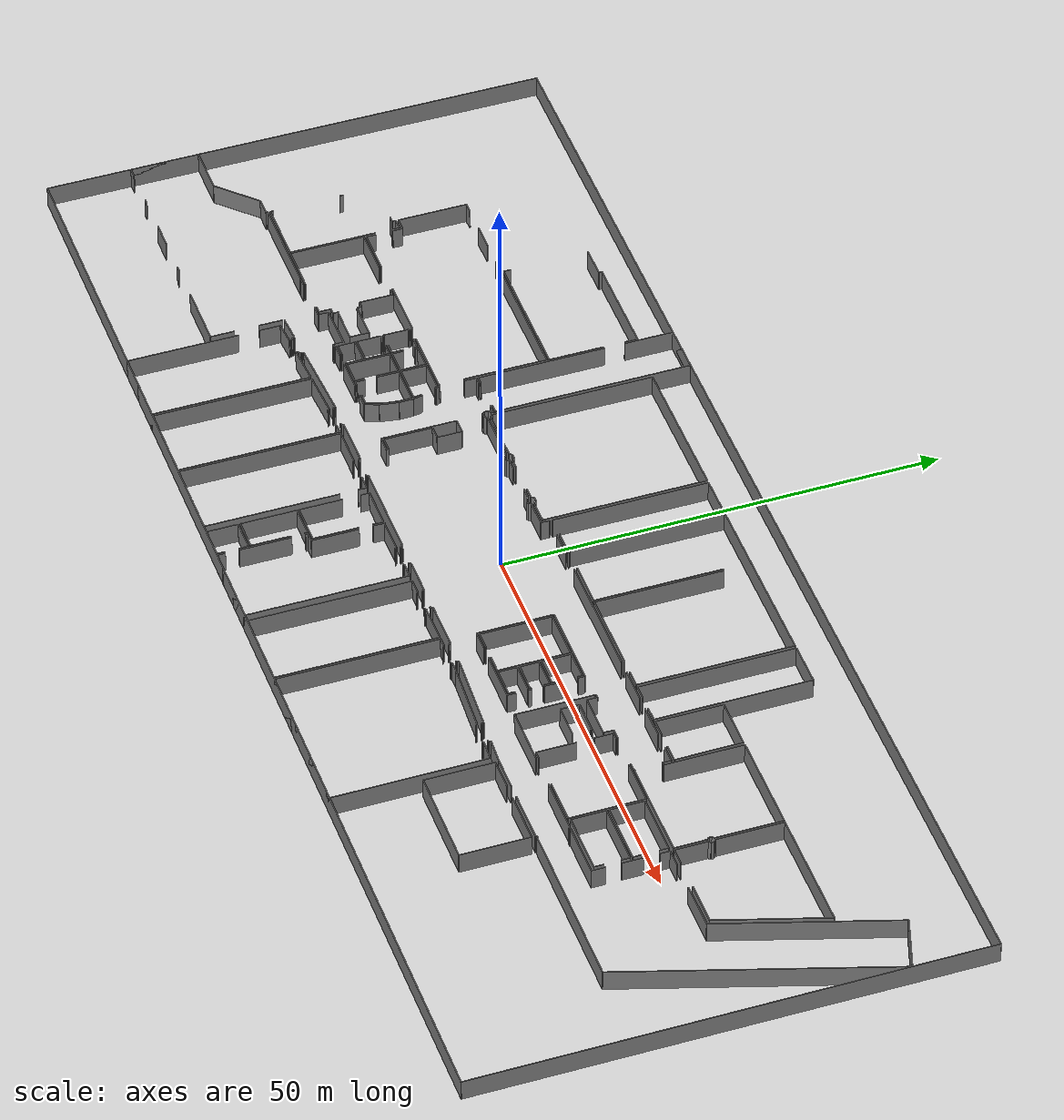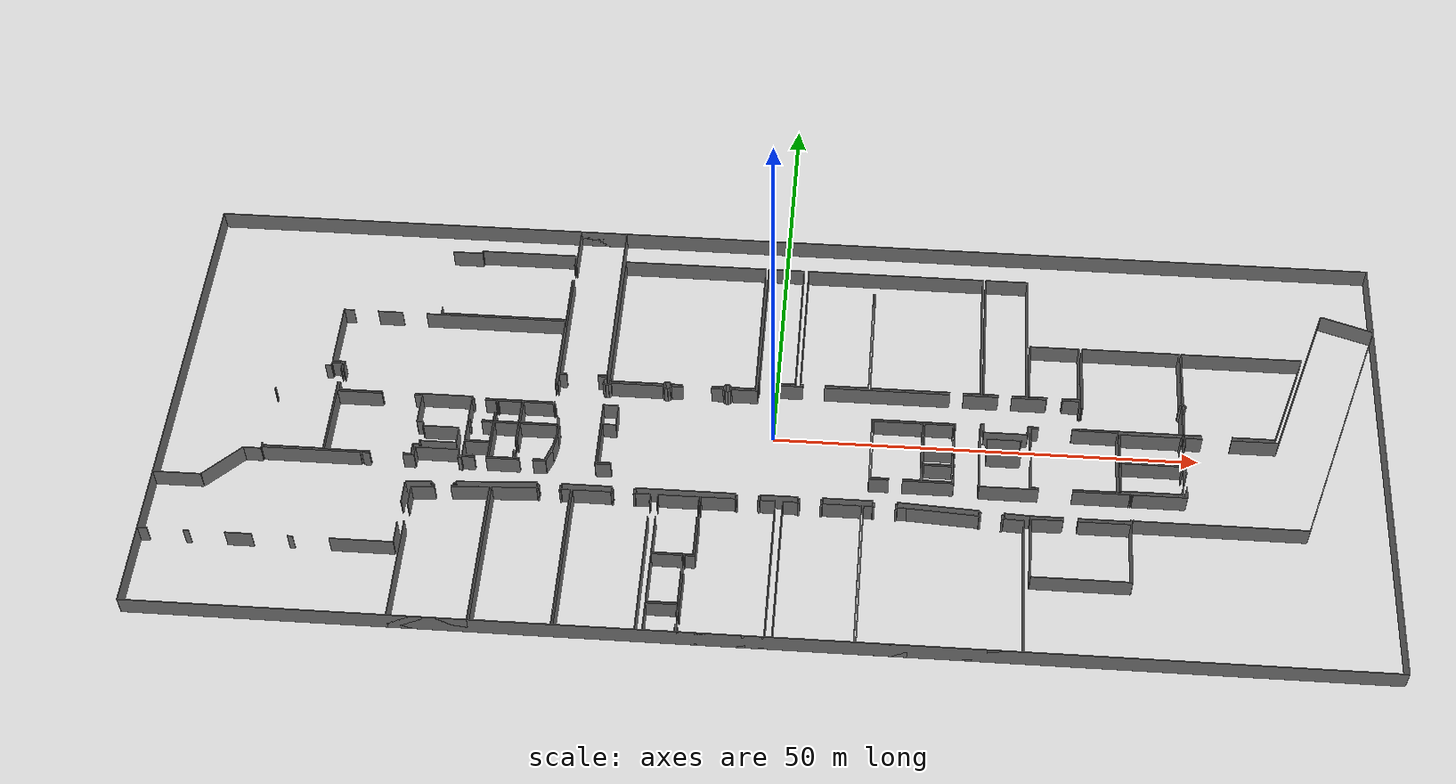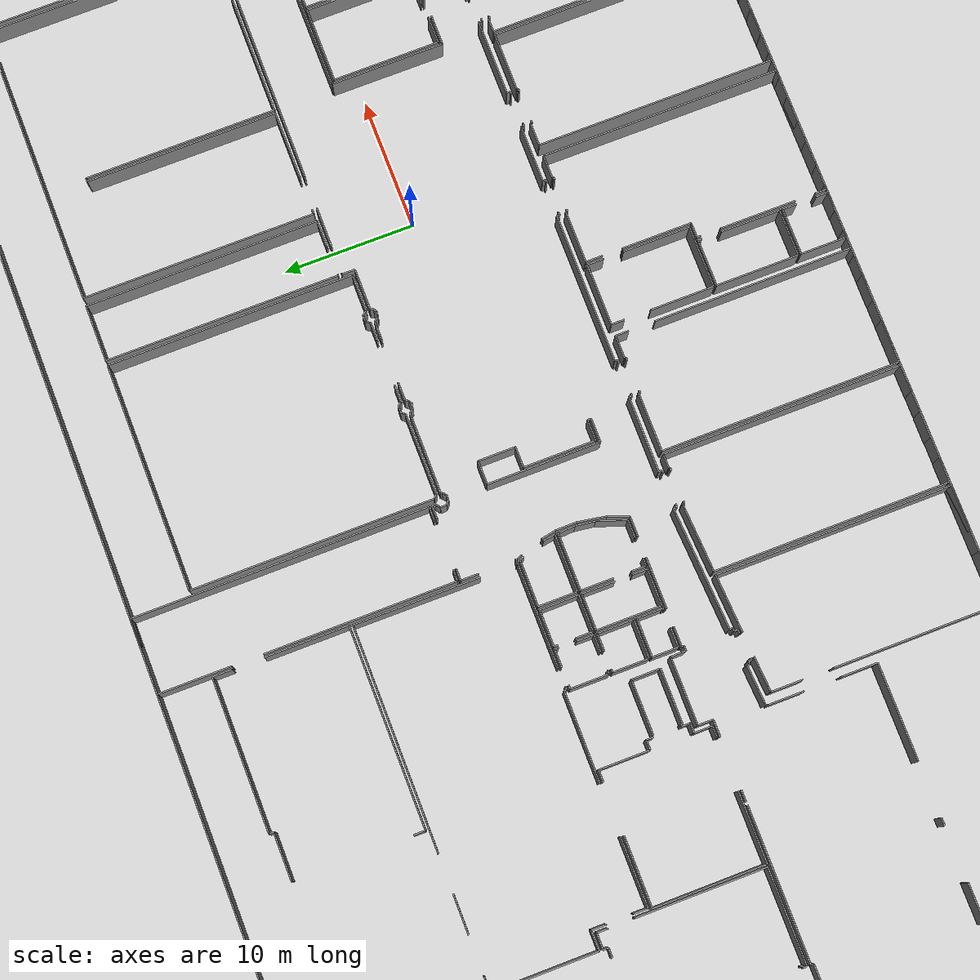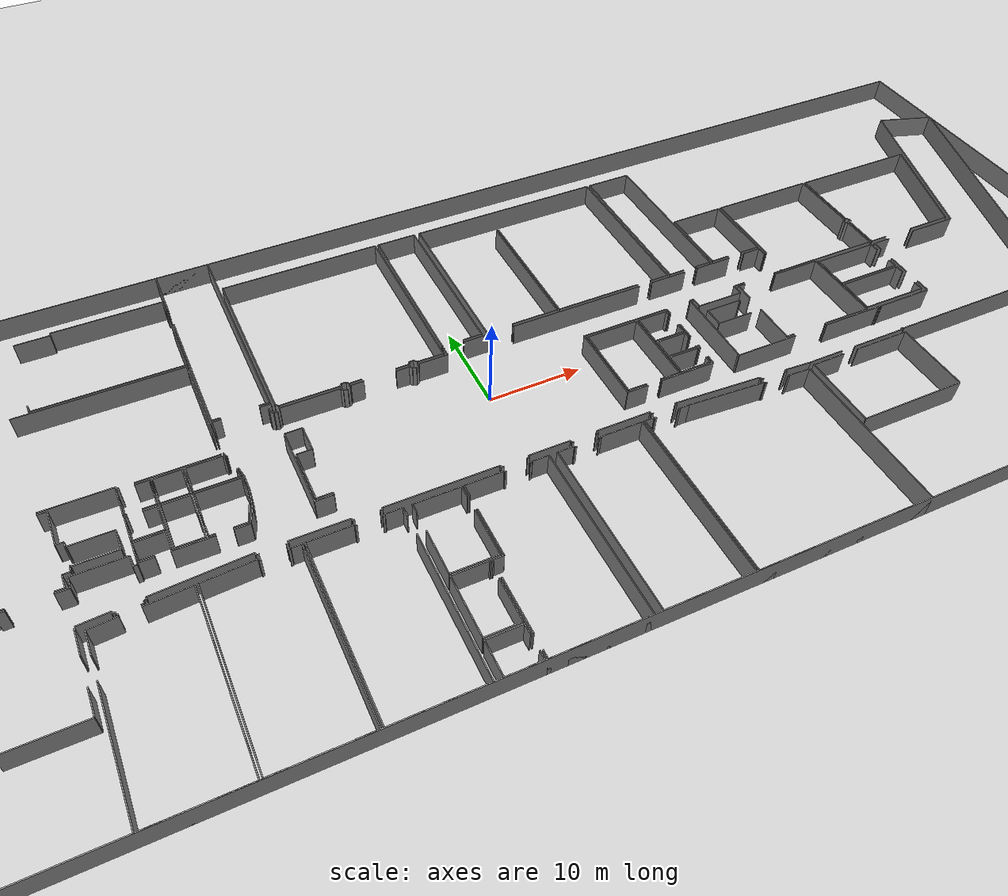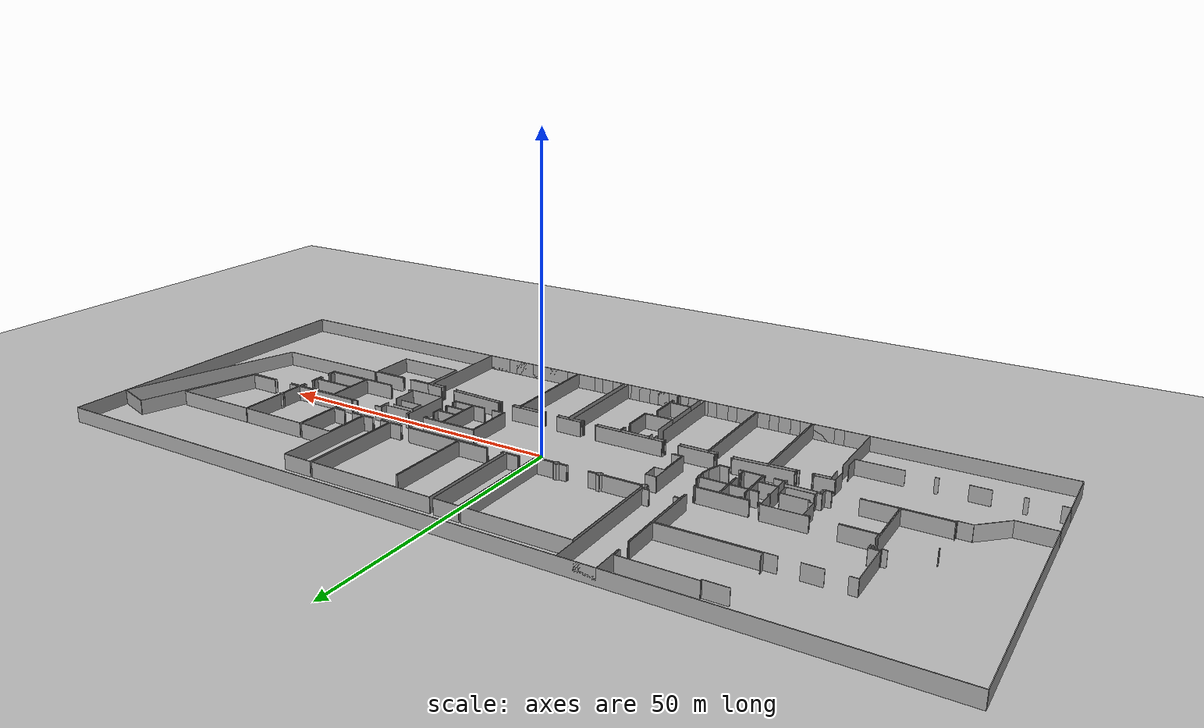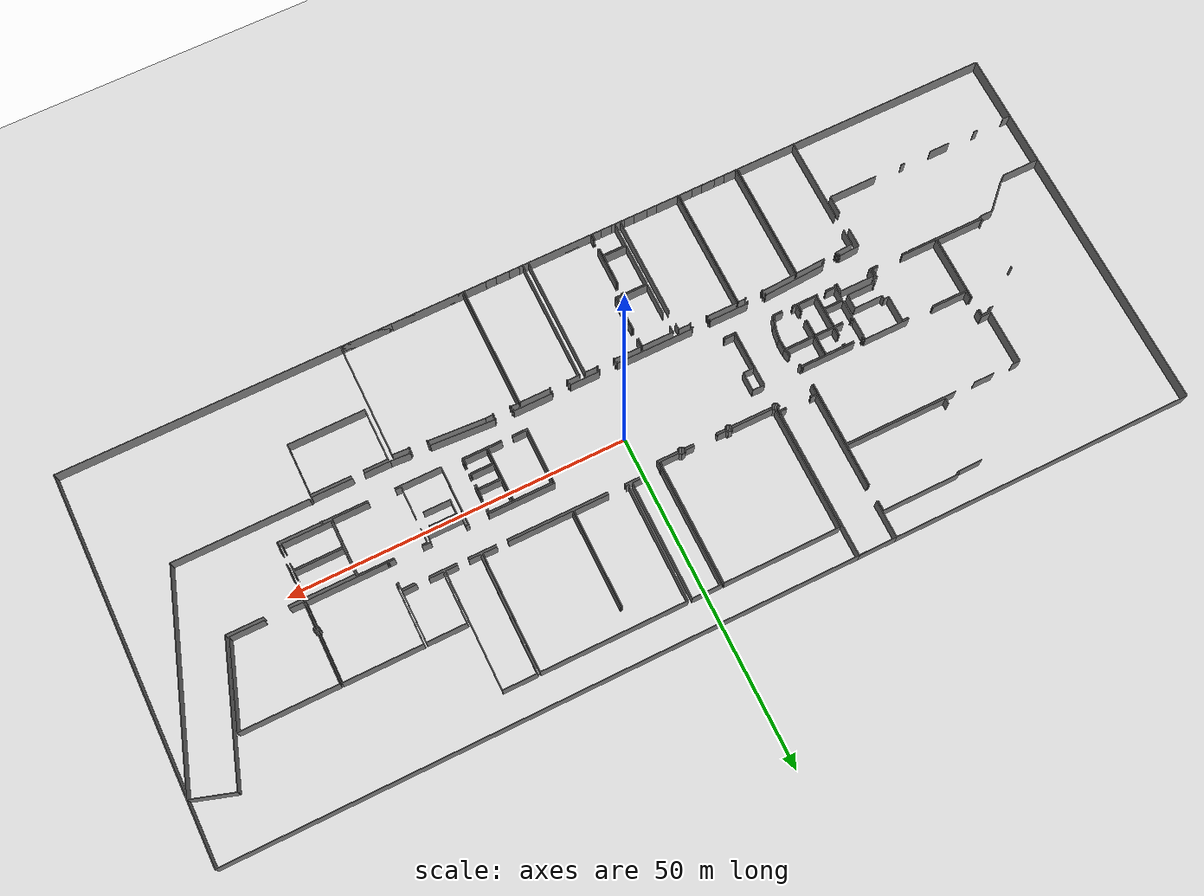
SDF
<sdf version="1.6">
  <world name="default">
    <light name="sun" type="directional">
      <cast_shadows>1</cast_shadows>
      <pose frame="">0 0 10 0 -0 0</pose>
      <diffuse>0.8 0.8 0.8 1</diffuse>
      <specular>0.1 0.1 0.1 1</specular>
      <attenuation>
        <range>1000</range>
        <constant>0.9</constant>
        <linear>0.01</linear>
        <quadratic>0.001</quadratic>
      </attenuation>
      <direction>-0.5 0.5 -1</direction>
    </light>
    <model name="ground_plane">
      <static>1</static>
      <link name="link">
        <collision name="collision">
          <geometry>
            <plane>
              <normal>0 0 1</normal>
              <size>100 100</size>
            </plane>
          </geometry>
          <surface>
            <friction>
              <ode>
                <mu>100</mu>
                <mu2>50</mu2>
              </ode>
              <torsional>
                <ode />
              </torsional>
            </friction>
            <contact>
              <ode />
            </contact>
            <bounce />
          </surface>
          <max_contacts>10</max_contacts>
        </collision>
        <visual name="visual">
          <cast_shadows>0</cast_shadows>
          <geometry>
            <plane>
              <normal>0 0 1</normal>
              <size>100 100</size>
            </plane>
          </geometry>
          <material>
            <script>
              <uri>file://media/materials/scripts/gazebo.material</uri>
              <name>Gazebo/Grey</name>
            </script>
          </material>
        </visual>
        <self_collide>0</self_collide>
        <kinematic>0</kinematic>
        <gravity>1</gravity>
      </link>
    </model>
    <gravity>0 0 -9.8</gravity>
    <magnetic_field>6e-06 2.3e-05 -4.2e-05</magnetic_field>
    <atmosphere type="adiabatic" />
    <physics default="0" name="default_physics" type="ode">
      <max_step_size>0.001</max_step_size>
      <real_time_factor>1</real_time_factor>
      <real_time_update_rate>1000</real_time_update_rate>
    </physics>
    <scene>
      <ambient>0.4 0.4 0.4 1</ambient>
      <background>0.7 0.7 0.7 1</background>
      <shadows>1</shadows>
    </scene>
    <spherical_coordinates>
      <surface_model>EARTH_WGS84</surface_model>
      <latitude_deg>0</latitude_deg>
      <longitude_deg>0</longitude_deg>
      <elevation>0</elevation>
      <heading_deg>0</heading_deg>
    </spherical_coordinates>
  <model name="50041169">
		<static>1</static>
		<link name="Wall_0">
			<collision name="Wall_0_Collision">
				<geometry>
					<box>
						<size>15.3000393536 0.1 2.5</size>
					</box>
				</geometry>
				<pose frame="">7.65001967679 0 1.25 0 0 0</pose>
			</collision>
			<visual name="Wall_0_Visual">
				<pose frame="">7.65001967679 0 1.25 0 0 0</pose>
				<geometry>
					<box>
						<size>15.3000393536 0.1 2.5</size>
					</box>
				</geometry>
				<material>
					<script>
						<uri>file://media/materials/scripts/gazebo.material</uri>
						<name>Gazebo/Grey</name>
					</script>
					<ambient>1 1 1 1</ambient>
				</material>
			</visual>
			<pose frame="">45.1562083455 -14.251647138 0 0 0 3.14159265359</pose>
		</link>
		<link name="Wall_1">
			<collision name="Wall_1_Collision">
				<geometry>
					<box>
						<size>0.882662841329 0.1 2.5</size>
					</box>
				</geometry>
				<pose frame="">0.441331420664 0 1.25 0 0 0</pose>
			</collision>
			<visual name="Wall_1_Visual">
				<pose frame="">0.441331420664 0 1.25 0 0 0</pose>
				<geometry>
					<box>
						<size>0.882662841329 0.1 2.5</size>
					</box>
				</geometry>
				<material>
					<script>
						<uri>file://media/materials/scripts/gazebo.material</uri>
						<name>Gazebo/Grey</name>
					</script>
					<ambient>1 1 1 1</ambient>
				</material>
			</visual>
			<pose frame="">29.8561689919 -14.251647138 0 0 0 1.57079632679</pose>
		</link>
		<link name="Wall_2">
			<collision name="Wall_2_Collision">
				<geometry>
					<box>
						<size>3.64617318117 0.1 2.5</size>
					</box>
				</geometry>
				<pose frame="">1.82308659058 0 1.25 0 0 0</pose>
			</collision>
			<visual name="Wall_2_Visual">
				<pose frame="">1.82308659058 0 1.25 0 0 0</pose>
				<geometry>
					<box>
						<size>3.64617318117 0.1 2.5</size>
					</box>
				</geometry>
				<material>
					<script>
						<uri>file://media/materials/scripts/gazebo.material</uri>
						<name>Gazebo/Grey</name>
					</script>
					<ambient>1 1 1 1</ambient>
				</material>
			</visual>
			<pose frame="">29.8561689919 -4.37097736534 0 0 0 0.0</pose>
		</link>
		<link name="Wall_3">
			<collision name="Wall_3_Collision">
				<geometry>
					<box>
						<size>0.351135541366 0.1 2.5</size>
					</box>
				</geometry>
				<pose frame="">0.175567770683 0 1.25 0 0 0</pose>
			</collision>
			<visual name="Wall_3_Visual">
				<pose frame="">0.175567770683 0 1.25 0 0 0</pose>
				<geometry>
					<box>
						<size>0.351135541366 0.1 2.5</size>
					</box>
				</geometry>
				<material>
					<script>
						<uri>file://media/materials/scripts/gazebo.material</uri>
						<name>Gazebo/Grey</name>
					</script>
					<ambient>1 1 1 1</ambient>
				</material>
			</visual>
			<pose frame="">33.5023421731 -4.37097736534 0 0 0 1.57079632679</pose>
		</link>
		<link name="Wall_4">
			<collision name="Wall_4_Collision">
				<geometry>
					<box>
						<size>11.6536122783 0.1 2.5</size>
					</box>
				</geometry>
				<pose frame="">5.82680613916 0 1.25 0 0 0</pose>
			</collision>
			<visual name="Wall_4_Visual">
				<pose frame="">5.82680613916 0 1.25 0 0 0</pose>
				<geometry>
					<box>
						<size>11.6536122783 0.1 2.5</size>
					</box>
				</geometry>
				<material>
					<script>
						<uri>file://media/materials/scripts/gazebo.material</uri>
						<name>Gazebo/Grey</name>
					</script>
					<ambient>1 1 1 1</ambient>
				</material>
			</visual>
			<pose frame="">33.5023421731 -4.01984182398 0 0 0 0.0</pose>
		</link>
		<link name="Wall_5">
			<collision name="Wall_5_Collision">
				<geometry>
					<box>
						<size>1.51155852894 0.1 2.5</size>
					</box>
				</geometry>
				<pose frame="">0.755779264469 0 1.25 0 0 0</pose>
			</collision>
			<visual name="Wall_5_Visual">
				<pose frame="">0.755779264469 0 1.25 0 0 0</pose>
				<geometry>
					<box>
						<size>1.51155852894 0.1 2.5</size>
					</box>
				</geometry>
				<material>
					<script>
						<uri>file://media/materials/scripts/gazebo.material</uri>
						<name>Gazebo/Grey</name>
					</script>
					<ambient>1 1 1 1</ambient>
				</material>
			</visual>
			<pose frame="">45.1559544514 -4.01984182398 0 0 0 -1.57079632679</pose>
		</link>
		<link name="Wall_6">
			<collision name="Wall_6_Collision">
				<geometry>
					<box>
						<size>6.33249971946 0.1 2.5</size>
					</box>
				</geometry>
				<pose frame="">3.16624985973 0 1.25 0 0 0</pose>
			</collision>
			<visual name="Wall_6_Visual">
				<pose frame="">3.16624985973 0 1.25 0 0 0</pose>
				<geometry>
					<box>
						<size>6.33249971946 0.1 2.5</size>
					</box>
				</geometry>
				<material>
					<script>
						<uri>file://media/materials/scripts/gazebo.material</uri>
						<name>Gazebo/Grey</name>
					</script>
					<ambient>1 1 1 1</ambient>
				</material>
			</visual>
			<pose frame="">45.1559544514 -7.91914742361 0 0 0 -1.57075623298</pose>
		</link>
		<link name="Wall_7">
			<collision name="Wall_7_Collision">
				<geometry>
					<box>
						<size>1.04870958323 0.1 2.5</size>
					</box>
				</geometry>
				<pose frame="">0.524354791616 0 1.25 0 0 0</pose>
			</collision>
			<visual name="Wall_7_Visual">
				<pose frame="">0.524354791616 0 1.25 0 0 0</pose>
				<geometry>
					<box>
						<size>1.04870958323 0.1 2.5</size>
					</box>
				</geometry>
				<material>
					<script>
						<uri>file://media/materials/scripts/gazebo.material</uri>
						<name>Gazebo/Grey</name>
					</script>
					<ambient>1 1 1 1</ambient>
				</material>
			</visual>
			<pose frame="">51.0838739162 -22.5202163178 0 0 0 3.14159265359</pose>
		</link>
		<link name="Wall_8">
			<collision name="Wall_8_Collision">
				<geometry>
					<box>
						<size>0.884820941185 0.1 2.5</size>
					</box>
				</geometry>
				<pose frame="">0.442410470593 0 1.25 0 0 0</pose>
			</collision>
			<visual name="Wall_8_Visual">
				<pose frame="">0.442410470593 0 1.25 0 0 0</pose>
				<geometry>
					<box>
						<size>0.884820941185 0.1 2.5</size>
					</box>
				</geometry>
				<material>
					<script>
						<uri>file://media/materials/scripts/gazebo.material</uri>
						<name>Gazebo/Grey</name>
					</script>
					<ambient>1 1 1 1</ambient>
				</material>
			</visual>
			<pose frame="">46.2591243192 -22.5202163178 0 0 0 3.14159265359</pose>
		</link>
		<link name="Wall_9">
			<collision name="Wall_9_Collision">
				<geometry>
					<box>
						<size>14.5852005129 0.1 2.5</size>
					</box>
				</geometry>
				<pose frame="">7.29260025643 0 1.25 0 0 0</pose>
			</collision>
			<visual name="Wall_9_Visual">
				<pose frame="">7.29260025643 0 1.25 0 0 0</pose>
				<geometry>
					<box>
						<size>14.5852005129 0.1 2.5</size>
					</box>
				</geometry>
				<material>
					<script>
						<uri>file://media/materials/scripts/gazebo.material</uri>
						<name>Gazebo/Grey</name>
					</script>
					<ambient>1 1 1 1</ambient>
				</material>
			</visual>
			<pose frame="">45.3743033781 -22.5202163178 0 0 0 1.57079632679</pose>
		</link>
		<link name="Wall_10">
			<collision name="Wall_10_Collision">
				<geometry>
					<box>
						<size>5.56377185076 0.1 2.5</size>
					</box>
				</geometry>
				<pose frame="">2.78188592538 0 1.25 0 0 0</pose>
			</collision>
			<visual name="Wall_10_Visual">
				<pose frame="">2.78188592538 0 1.25 0 0 0</pose>
				<geometry>
					<box>
						<size>5.56377185076 0.1 2.5</size>
					</box>
				</geometry>
				<material>
					<script>
						<uri>file://media/materials/scripts/gazebo.material</uri>
						<name>Gazebo/Grey</name>
					</script>
					<ambient>1 1 1 1</ambient>
				</material>
			</visual>
			<pose frame="">45.3743033781 -5.56377185076 0 0 0 1.57079632679</pose>
		</link>
		<link name="Wall_11">
			<collision name="Wall_11_Collision">
				<geometry>
					<box>
						<size>5.68849732776 0.1 2.5</size>
					</box>
				</geometry>
				<pose frame="">2.84424866388 0 1.25 0 0 0</pose>
			</collision>
			<visual name="Wall_11_Visual">
				<pose frame="">2.84424866388 0 1.25 0 0 0</pose>
				<geometry>
					<box>
						<size>5.68849732776 0.1 2.5</size>
					</box>
				</geometry>
				<material>
					<script>
						<uri>file://media/materials/scripts/gazebo.material</uri>
						<name>Gazebo/Grey</name>
					</script>
					<ambient>1 1 1 1</ambient>
				</material>
			</visual>
			<pose frame="">45.3743033781 -0.0 0 0 0 0.0</pose>
		</link>
		<link name="Wall_12">
			<collision name="Wall_12_Collision">
				<geometry>
					<box>
						<size>22.5202261774 0.1 2.5</size>
					</box>
				</geometry>
				<pose frame="">11.2601130887 0 1.25 0 0 0</pose>
			</collision>
			<visual name="Wall_12_Visual">
				<pose frame="">11.2601130887 0 1.25 0 0 0</pose>
				<geometry>
					<box>
						<size>22.5202261774 0.1 2.5</size>
					</box>
				</geometry>
				<material>
					<script>
						<uri>file://media/materials/scripts/gazebo.material</uri>
						<name>Gazebo/Grey</name>
					</script>
					<ambient>1 1 1 1</ambient>
				</material>
			</visual>
			<pose frame="">51.0628007058 -0.0 0 0 0 -1.56986058071</pose>
		</link>
		<link name="Wall_13">
			<collision name="Wall_13_Collision">
				<geometry>
					<box>
						<size>0.0944486054866 0.1 2.5</size>
					</box>
				</geometry>
				<pose frame="">0.0472243027433 0 1.25 0 0 0</pose>
			</collision>
			<visual name="Wall_13_Visual">
				<pose frame="">0.0472243027433 0 1.25 0 0 0</pose>
				<geometry>
					<box>
						<size>0.0944486054866 0.1 2.5</size>
					</box>
				</geometry>
				<material>
					<script>
						<uri>file://media/materials/scripts/gazebo.material</uri>
						<name>Gazebo/Grey</name>
					</script>
					<ambient>1 1 1 1</ambient>
				</material>
			</visual>
			<pose frame="">45.0571896462 -26.8521574651 0 0 0 -1.57079632679</pose>
		</link>
		<link name="Wall_14">
			<collision name="Wall_14_Collision">
				<geometry>
					<box>
						<size>7.95145544793 0.1 2.5</size>
					</box>
				</geometry>
				<pose frame="">3.97572772397 0 1.25 0 0 0</pose>
			</collision>
			<visual name="Wall_14_Visual">
				<pose frame="">3.97572772397 0 1.25 0 0 0</pose>
				<geometry>
					<box>
						<size>7.95145544793 0.1 2.5</size>
					</box>
				</geometry>
				<material>
					<script>
						<uri>file://media/materials/scripts/gazebo.material</uri>
						<name>Gazebo/Grey</name>
					</script>
					<ambient>1 1 1 1</ambient>
				</material>
			</visual>
			<pose frame="">45.0571896462 -26.9466060706 0 0 0 3.14159265359</pose>
		</link>
		<link name="Wall_15">
			<collision name="Wall_15_Collision">
				<geometry>
					<box>
						<size>0.261257029693 0.1 2.5</size>
					</box>
				</geometry>
				<pose frame="">0.130628514846 0 1.25 0 0 0</pose>
			</collision>
			<visual name="Wall_15_Visual">
				<pose frame="">0.130628514846 0 1.25 0 0 0</pose>
				<geometry>
					<box>
						<size>0.261257029693 0.1 2.5</size>
					</box>
				</geometry>
				<material>
					<script>
						<uri>file://media/materials/scripts/gazebo.material</uri>
						<name>Gazebo/Grey</name>
					</script>
					<ambient>1 1 1 1</ambient>
				</material>
			</visual>
			<pose frame="">35.7265814429 -26.9466060706 0 0 0 3.14159265359</pose>
		</link>
		<link name="Wall_16">
			<collision name="Wall_16_Collision">
				<geometry>
					<box>
						<size>0.196006245795 0.1 2.5</size>
					</box>
				</geometry>
				<pose frame="">0.0980031228974 0 1.25 0 0 0</pose>
			</collision>
			<visual name="Wall_16_Visual">
				<pose frame="">0.0980031228974 0 1.25 0 0 0</pose>
				<geometry>
					<box>
						<size>0.196006245795 0.1 2.5</size>
					</box>
				</geometry>
				<material>
					<script>
						<uri>file://media/materials/scripts/gazebo.material</uri>
						<name>Gazebo/Grey</name>
					</script>
					<ambient>1 1 1 1</ambient>
				</material>
			</visual>
			<pose frame="">35.4653244132 -26.9466060706 0 0 0 1.57079632679</pose>
		</link>
		<link name="Wall_17">
			<collision name="Wall_17_Collision">
				<geometry>
					<box>
						<size>6.8684701611 0.1 2.5</size>
					</box>
				</geometry>
				<pose frame="">3.43423508055 0 1.25 0 0 0</pose>
			</collision>
			<visual name="Wall_17_Visual">
				<pose frame="">3.43423508055 0 1.25 0 0 0</pose>
				<geometry>
					<box>
						<size>6.8684701611 0.1 2.5</size>
					</box>
				</geometry>
				<material>
					<script>
						<uri>file://media/materials/scripts/gazebo.material</uri>
						<name>Gazebo/Grey</name>
					</script>
					<ambient>1 1 1 1</ambient>
				</material>
			</visual>
			<pose frame="">35.4653244132 -26.7505998248 0 0 0 3.14159265359</pose>
		</link>
		<link name="Wall_18">
			<collision name="Wall_18_Collision">
				<geometry>
					<box>
						<size>5.2549731507 0.1 2.5</size>
					</box>
				</geometry>
				<pose frame="">2.62748657535 0 1.25 0 0 0</pose>
			</collision>
			<visual name="Wall_18_Visual">
				<pose frame="">2.62748657535 0 1.25 0 0 0</pose>
				<geometry>
					<box>
						<size>5.2549731507 0.1 2.5</size>
					</box>
				</geometry>
				<material>
					<script>
						<uri>file://media/materials/scripts/gazebo.material</uri>
						<name>Gazebo/Grey</name>
					</script>
					<ambient>1 1 1 1</ambient>
				</material>
			</visual>
			<pose frame="">24.6796491184 -26.7505998248 0 0 0 3.14159265359</pose>
		</link>
		<link name="Wall_19">
			<collision name="Wall_19_Collision">
				<geometry>
					<box>
						<size>1.09529915072 0.1 2.5</size>
					</box>
				</geometry>
				<pose frame="">0.547649575362 0 1.25 0 0 0</pose>
			</collision>
			<visual name="Wall_19_Visual">
				<pose frame="">0.547649575362 0 1.25 0 0 0</pose>
				<geometry>
					<box>
						<size>1.09529915072 0.1 2.5</size>
					</box>
				</geometry>
				<material>
					<script>
						<uri>file://media/materials/scripts/gazebo.material</uri>
						<name>Gazebo/Grey</name>
					</script>
					<ambient>1 1 1 1</ambient>
				</material>
			</visual>
			<pose frame="">19.4246759677 -26.7505998248 0 0 0 1.57079632679</pose>
		</link>
		<link name="Wall_20">
			<collision name="Wall_20_Collision">
				<geometry>
					<box>
						<size>1.12779759562 0.1 2.5</size>
					</box>
				</geometry>
				<pose frame="">0.563898797811 0 1.25 0 0 0</pose>
			</collision>
			<visual name="Wall_20_Visual">
				<pose frame="">0.563898797811 0 1.25 0 0 0</pose>
				<geometry>
					<box>
						<size>1.12779759562 0.1 2.5</size>
					</box>
				</geometry>
				<material>
					<script>
						<uri>file://media/materials/scripts/gazebo.material</uri>
						<name>Gazebo/Grey</name>
					</script>
					<ambient>1 1 1 1</ambient>
				</material>
			</visual>
			<pose frame="">19.4246759677 -23.6533456895 0 0 0 1.57079632679</pose>
		</link>
		<link name="Wall_21">
			<collision name="Wall_21_Collision">
				<geometry>
					<box>
						<size>1.51193937009 0.1 2.5</size>
					</box>
				</geometry>
				<pose frame="">0.755969685044 0 1.25 0 0 0</pose>
			</collision>
			<visual name="Wall_21_Visual">
				<pose frame="">0.755969685044 0 1.25 0 0 0</pose>
				<geometry>
					<box>
						<size>1.51193937009 0.1 2.5</size>
					</box>
				</geometry>
				<material>
					<script>
						<uri>file://media/materials/scripts/gazebo.material</uri>
						<name>Gazebo/Grey</name>
					</script>
					<ambient>1 1 1 1</ambient>
				</material>
			</visual>
			<pose frame="">19.4246759677 -22.5255480939 0 0 0 3.14159265359</pose>
		</link>
		<link name="Wall_22">
			<collision name="Wall_22_Collision">
				<geometry>
					<box>
						<size>8.01302476737 0.1 2.5</size>
					</box>
				</geometry>
				<pose frame="">4.00651238368 0 1.25 0 0 0</pose>
			</collision>
			<visual name="Wall_22_Visual">
				<pose frame="">4.00651238368 0 1.25 0 0 0</pose>
				<geometry>
					<box>
						<size>8.01302476737 0.1 2.5</size>
					</box>
				</geometry>
				<material>
					<script>
						<uri>file://media/materials/scripts/gazebo.material</uri>
						<name>Gazebo/Grey</name>
					</script>
					<ambient>1 1 1 1</ambient>
				</material>
			</visual>
			<pose frame="">17.9127365976 -22.5255480939 0 0 0 1.57079632679</pose>
		</link>
		<link name="Wall_23">
			<collision name="Wall_23_Collision">
				<geometry>
					<box>
						<size>1.2348139591 0.1 2.5</size>
					</box>
				</geometry>
				<pose frame="">0.617406979549 0 1.25 0 0 0</pose>
			</collision>
			<visual name="Wall_23_Visual">
				<pose frame="">0.617406979549 0 1.25 0 0 0</pose>
				<geometry>
					<box>
						<size>1.2348139591 0.1 2.5</size>
					</box>
				</geometry>
				<material>
					<script>
						<uri>file://media/materials/scripts/gazebo.material</uri>
						<name>Gazebo/Grey</name>
					</script>
					<ambient>1 1 1 1</ambient>
				</material>
			</visual>
			<pose frame="">17.9127365976 -14.5125233265 0 0 0 0.0</pose>
		</link>
		<link name="Wall_24">
			<collision name="Wall_24_Collision">
				<geometry>
					<box>
						<size>3.02324400493 0.1 2.5</size>
					</box>
				</geometry>
				<pose frame="">1.51162200246 0 1.25 0 0 0</pose>
			</collision>
			<visual name="Wall_24_Visual">
				<pose frame="">1.51162200246 0 1.25 0 0 0</pose>
				<geometry>
					<box>
						<size>3.02324400493 0.1 2.5</size>
					</box>
				</geometry>
				<material>
					<script>
						<uri>file://media/materials/scripts/gazebo.material</uri>
						<name>Gazebo/Grey</name>
					</script>
					<ambient>1 1 1 1</ambient>
				</material>
			</visual>
			<pose frame="">22.101354525 -14.5125233265 0 0 0 0.0</pose>
		</link>
		<link name="Wall_25">
			<collision name="Wall_25_Collision">
				<geometry>
					<box>
						<size>17.0201718863 0.1 2.5</size>
					</box>
				</geometry>
				<pose frame="">8.51008594315 0 1.25 0 0 0</pose>
			</collision>
			<visual name="Wall_25_Visual">
				<pose frame="">8.51008594315 0 1.25 0 0 0</pose>
				<geometry>
					<box>
						<size>17.0201718863 0.1 2.5</size>
					</box>
				</geometry>
				<material>
					<script>
						<uri>file://media/materials/scripts/gazebo.material</uri>
						<name>Gazebo/Grey</name>
					</script>
					<ambient>1 1 1 1</ambient>
				</material>
			</visual>
			<pose frame="">28.0593604408 -14.5125233265 0 0 0 0.0</pose>
		</link>
		<link name="Wall_26">
			<collision name="Wall_26_Collision">
				<geometry>
					<box>
						<size>9.60674401945 0.1 2.5</size>
					</box>
				</geometry>
				<pose frame="">4.80337200972 0 1.25 0 0 0</pose>
			</collision>
			<visual name="Wall_26_Visual">
				<pose frame="">4.80337200972 0 1.25 0 0 0</pose>
				<geometry>
					<box>
						<size>9.60674401945 0.1 2.5</size>
					</box>
				</geometry>
				<material>
					<script>
						<uri>file://media/materials/scripts/gazebo.material</uri>
						<name>Gazebo/Grey</name>
					</script>
					<ambient>1 1 1 1</ambient>
				</material>
			</visual>
			<pose frame="">45.0795323271 -14.5125233265 0 0 0 -1.57312205765</pose>
		</link>
		<link name="Wall_27">
			<collision name="Wall_27_Collision">
				<geometry>
					<box>
						<size>7.21173498534 0.1 2.5</size>
					</box>
				</geometry>
				<pose frame="">3.60586749267 0 1.25 0 0 0</pose>
			</collision>
			<visual name="Wall_27_Visual">
				<pose frame="">3.60586749267 0 1.25 0 0 0</pose>
				<geometry>
					<box>
						<size>7.21173498534 0.1 2.5</size>
					</box>
				</geometry>
				<material>
					<script>
						<uri>file://media/materials/scripts/gazebo.material</uri>
						<name>Gazebo/Grey</name>
					</script>
					<ambient>1 1 1 1</ambient>
				</material>
			</visual>
			<pose frame="">19.1062927653 -35.5135008188 0 0 0 3.14159265359</pose>
		</link>
		<link name="Wall_28">
			<collision name="Wall_28_Collision">
				<geometry>
					<box>
						<size>0.325619184238 0.1 2.5</size>
					</box>
				</geometry>
				<pose frame="">0.162809592119 0 1.25 0 0 0</pose>
			</collision>
			<visual name="Wall_28_Visual">
				<pose frame="">0.162809592119 0 1.25 0 0 0</pose>
				<geometry>
					<box>
						<size>0.325619184238 0.1 2.5</size>
					</box>
				</geometry>
				<material>
					<script>
						<uri>file://media/materials/scripts/gazebo.material</uri>
						<name>Gazebo/Grey</name>
					</script>
					<ambient>1 1 1 1</ambient>
				</material>
			</visual>
			<pose frame="">11.8945577799 -35.5135008188 0 0 0 1.57079632679</pose>
		</link>
		<link name="Wall_29">
			<collision name="Wall_29_Collision">
				<geometry>
					<box>
						<size>0.375255480939 0.1 2.5</size>
					</box>
				</geometry>
				<pose frame="">0.187627740469 0 1.25 0 0 0</pose>
			</collision>
			<visual name="Wall_29_Visual">
				<pose frame="">0.187627740469 0 1.25 0 0 0</pose>
				<geometry>
					<box>
						<size>0.375255480939 0.1 2.5</size>
					</box>
				</geometry>
				<material>
					<script>
						<uri>file://media/materials/scripts/gazebo.material</uri>
						<name>Gazebo/Grey</name>
					</script>
					<ambient>1 1 1 1</ambient>
				</material>
			</visual>
			<pose frame="">11.8945577799 -27.3662930192 0 0 0 1.57079632679</pose>
		</link>
		<link name="Wall_30">
			<collision name="Wall_30_Collision">
				<geometry>
					<box>
						<size>0.754954108641 0.1 2.5</size>
					</box>
				</geometry>
				<pose frame="">0.377477054321 0 1.25 0 0 0</pose>
			</collision>
			<visual name="Wall_30_Visual">
				<pose frame="">0.377477054321 0 1.25 0 0 0</pose>
				<geometry>
					<box>
						<size>0.754954108641 0.1 2.5</size>
					</box>
				</geometry>
				<material>
					<script>
						<uri>file://media/materials/scripts/gazebo.material</uri>
						<name>Gazebo/Grey</name>
					</script>
					<ambient>1 1 1 1</ambient>
				</material>
			</visual>
			<pose frame="">17.1382326432 -23.2012872431 0 0 0 0.0</pose>
		</link>
		<link name="Wall_31">
			<collision name="Wall_31_Collision">
				<geometry>
					<box>
						<size>0.391885544539 0.1 2.5</size>
					</box>
				</geometry>
				<pose frame="">0.19594277227 0 1.25 0 0 0</pose>
			</collision>
			<visual name="Wall_31_Visual">
				<pose frame="">0.19594277227 0 1.25 0 0 0</pose>
				<geometry>
					<box>
						<size>0.391885544539 0.1 2.5</size>
					</box>
				</geometry>
				<material>
					<script>
						<uri>file://media/materials/scripts/gazebo.material</uri>
						<name>Gazebo/Grey</name>
					</script>
					<ambient>1 1 1 1</ambient>
				</material>
			</visual>
			<pose frame="">17.8931867518 -23.2012872431 0 0 0 1.57079632679</pose>
		</link>
		<link name="Wall_32">
			<collision name="Wall_32_Collision">
				<geometry>
					<box>
						<size>1.23379838269 0.1 2.5</size>
					</box>
				</geometry>
				<pose frame="">0.616899191347 0 1.25 0 0 0</pose>
			</collision>
			<visual name="Wall_32_Visual">
				<pose frame="">0.616899191347 0 1.25 0 0 0</pose>
				<geometry>
					<box>
						<size>1.23379838269 0.1 2.5</size>
					</box>
				</geometry>
				<material>
					<script>
						<uri>file://media/materials/scripts/gazebo.material</uri>
						<name>Gazebo/Grey</name>
					</script>
					<ambient>1 1 1 1</ambient>
				</material>
			</visual>
			<pose frame="">17.8931867518 -22.8094016986 0 0 0 0.0</pose>
		</link>
		<link name="Wall_33">
			<collision name="Wall_33_Collision">
				<geometry>
					<box>
						<size>0.849148820027 0.1 2.5</size>
					</box>
				</geometry>
				<pose frame="">0.424574410014 0 1.25 0 0 0</pose>
			</collision>
			<visual name="Wall_33_Visual">
				<pose frame="">0.424574410014 0 1.25 0 0 0</pose>
				<geometry>
					<box>
						<size>0.849148820027 0.1 2.5</size>
					</box>
				</geometry>
				<material>
					<script>
						<uri>file://media/materials/scripts/gazebo.material</uri>
						<name>Gazebo/Grey</name>
					</script>
					<ambient>1 1 1 1</ambient>
				</material>
			</visual>
			<pose frame="">19.1269851345 -22.8094016986 0 0 0 -1.57079632679</pose>
		</link>
		<link name="Wall_34">
			<collision name="Wall_34_Collision">
				<geometry>
					<box>
						<size>9.90328796541 0.1 2.5</size>
					</box>
				</geometry>
				<pose frame="">4.9516439827 0 1.25 0 0 0</pose>
			</collision>
			<visual name="Wall_34_Visual">
				<pose frame="">4.9516439827 0 1.25 0 0 0</pose>
				<geometry>
					<box>
						<size>9.90328796541 0.1 2.5</size>
					</box>
				</geometry>
				<material>
					<script>
						<uri>file://media/materials/scripts/gazebo.material</uri>
						<name>Gazebo/Grey</name>
					</script>
					<ambient>1 1 1 1</ambient>
				</material>
			</visual>
			<pose frame="">19.1269851345 -25.6102344712 0 0 0 -1.57288577268</pose>
		</link>
		<link name="Wall_35">
			<collision name="Wall_35_Collision">
				<geometry>
					<box>
						<size>0.89307249946 0.1 2.5</size>
					</box>
				</geometry>
				<pose frame="">0.44653624973 0 1.25 0 0 0</pose>
			</collision>
			<visual name="Wall_35_Visual">
				<pose frame="">0.44653624973 0 1.25 0 0 0</pose>
				<geometry>
					<box>
						<size>0.89307249946 0.1 2.5</size>
					</box>
				</geometry>
				<material>
					<script>
						<uri>file://media/materials/scripts/gazebo.material</uri>
						<name>Gazebo/Grey</name>
					</script>
					<ambient>1 1 1 1</ambient>
				</material>
			</visual>
			<pose frame="">29.5066837622 -35.5635179567 0 0 0 3.14159265359</pose>
		</link>
		<link name="Wall_36">
			<collision name="Wall_36_Collision">
				<geometry>
					<box>
						<size>5.38318967159 0.1 2.5</size>
					</box>
				</geometry>
				<pose frame="">2.69159483579 0 1.25 0 0 0</pose>
			</collision>
			<visual name="Wall_36_Visual">
				<pose frame="">2.69159483579 0 1.25 0 0 0</pose>
				<geometry>
					<box>
						<size>5.38318967159 0.1 2.5</size>
					</box>
				</geometry>
				<material>
					<script>
						<uri>file://media/materials/scripts/gazebo.material</uri>
						<name>Gazebo/Grey</name>
					</script>
					<ambient>1 1 1 1</ambient>
				</material>
			</visual>
			<pose frame="">24.6750790245 -35.5635179567 0 0 0 3.14159265359</pose>
		</link>
		<link name="Wall_37">
			<collision name="Wall_37_Collision">
				<geometry>
					<box>
						<size>8.57235347137 0.1 2.5</size>
					</box>
				</geometry>
				<pose frame="">4.28617673568 0 1.25 0 0 0</pose>
			</collision>
			<visual name="Wall_37_Visual">
				<pose frame="">4.28617673568 0 1.25 0 0 0</pose>
				<geometry>
					<box>
						<size>8.57235347137 0.1 2.5</size>
					</box>
				</geometry>
				<material>
					<script>
						<uri>file://media/materials/scripts/gazebo.material</uri>
						<name>Gazebo/Grey</name>
					</script>
					<ambient>1 1 1 1</ambient>
				</material>
			</visual>
			<pose frame="">19.291889353 -35.5635179567 0 0 0 1.57079632679</pose>
		</link>
		<link name="Wall_38">
			<collision name="Wall_38_Collision">
				<geometry>
					<box>
						<size>5.35691163216 0.1 2.5</size>
					</box>
				</geometry>
				<pose frame="">2.67845581608 0 1.25 0 0 0</pose>
			</collision>
			<visual name="Wall_38_Visual">
				<pose frame="">2.67845581608 0 1.25 0 0 0</pose>
				<geometry>
					<box>
						<size>5.35691163216 0.1 2.5</size>
					</box>
				</geometry>
				<material>
					<script>
						<uri>file://media/materials/scripts/gazebo.material</uri>
						<name>Gazebo/Grey</name>
					</script>
					<ambient>1 1 1 1</ambient>
				</material>
			</visual>
			<pose frame="">19.291889353 -26.9911644853 0 0 0 0.0</pose>
		</link>
		<link name="Wall_39">
			<collision name="Wall_39_Collision">
				<geometry>
					<box>
						<size>0.914018762774 0.1 2.5</size>
					</box>
				</geometry>
				<pose frame="">0.457009381387 0 1.25 0 0 0</pose>
			</collision>
			<visual name="Wall_39_Visual">
				<pose frame="">0.457009381387 0 1.25 0 0 0</pose>
				<geometry>
					<box>
						<size>0.914018762774 0.1 2.5</size>
					</box>
				</geometry>
				<material>
					<script>
						<uri>file://media/materials/scripts/gazebo.material</uri>
						<name>Gazebo/Grey</name>
					</script>
					<ambient>1 1 1 1</ambient>
				</material>
			</visual>
			<pose frame="">28.5700684245 -26.9911644853 0 0 0 0.0</pose>
		</link>
		<link name="Wall_40">
			<collision name="Wall_40_Collision">
				<geometry>
					<box>
						<size>3.88546837114 0.1 2.5</size>
					</box>
				</geometry>
				<pose frame="">1.94273418557 0 1.25 0 0 0</pose>
			</collision>
			<visual name="Wall_40_Visual">
				<pose frame="">1.94273418557 0 1.25 0 0 0</pose>
				<geometry>
					<box>
						<size>3.88546837114 0.1 2.5</size>
					</box>
				</geometry>
				<material>
					<script>
						<uri>file://media/materials/scripts/gazebo.material</uri>
						<name>Gazebo/Grey</name>
					</script>
					<ambient>1 1 1 1</ambient>
				</material>
			</visual>
			<pose frame="">29.4840871872 -26.9911644853 0 0 0 -1.57079632679</pose>
		</link>
		<link name="Wall_41">
			<collision name="Wall_41_Collision">
				<geometry>
					<box>
						<size>0.748733703172 0.1 2.5</size>
					</box>
				</geometry>
				<pose frame="">0.374366851586 0 1.25 0 0 0</pose>
			</collision>
			<visual name="Wall_41_Visual">
				<pose frame="">0.374366851586 0 1.25 0 0 0</pose>
				<geometry>
					<box>
						<size>0.748733703172 0.1 2.5</size>
					</box>
				</geometry>
				<material>
					<script>
						<uri>file://media/materials/scripts/gazebo.material</uri>
						<name>Gazebo/Grey</name>
					</script>
					<ambient>1 1 1 1</ambient>
				</material>
			</visual>
			<pose frame="">29.4840871872 -30.8766328564 0 0 0 0.0</pose>
		</link>
		<link name="Wall_42">
			<collision name="Wall_42_Collision">
				<geometry>
					<box>
						<size>0.546760946009 0.1 2.5</size>
					</box>
				</geometry>
				<pose frame="">0.273380473005 0 1.25 0 0 0</pose>
			</collision>
			<visual name="Wall_42_Visual">
				<pose frame="">0.273380473005 0 1.25 0 0 0</pose>
				<geometry>
					<box>
						<size>0.546760946009 0.1 2.5</size>
					</box>
				</geometry>
				<material>
					<script>
						<uri>file://media/materials/scripts/gazebo.material</uri>
						<name>Gazebo/Grey</name>
					</script>
					<ambient>1 1 1 1</ambient>
				</material>
			</visual>
			<pose frame="">30.2328208904 -30.8766328564 0 0 0 -1.57079632679</pose>
		</link>
		<link name="Wall_43">
			<collision name="Wall_43_Collision">
				<geometry>
					<box>
						<size>0.681705660569 0.1 2.5</size>
					</box>
				</geometry>
				<pose frame="">0.340852830284 0 1.25 0 0 0</pose>
			</collision>
			<visual name="Wall_43_Visual">
				<pose frame="">0.340852830284 0 1.25 0 0 0</pose>
				<geometry>
					<box>
						<size>0.681705660569 0.1 2.5</size>
					</box>
				</geometry>
				<material>
					<script>
						<uri>file://media/materials/scripts/gazebo.material</uri>
						<name>Gazebo/Grey</name>
					</script>
					<ambient>1 1 1 1</ambient>
				</material>
			</visual>
			<pose frame="">30.2328208904 -33.4931385119 0 0 0 -1.57079632679</pose>
		</link>
		<link name="Wall_44">
			<collision name="Wall_44_Collision">
				<geometry>
					<box>
						<size>0.740736038998 0.1 2.5</size>
					</box>
				</geometry>
				<pose frame="">0.370368019499 0 1.25 0 0 0</pose>
			</collision>
			<visual name="Wall_44_Visual">
				<pose frame="">0.370368019499 0 1.25 0 0 0</pose>
				<geometry>
					<box>
						<size>0.740736038998 0.1 2.5</size>
					</box>
				</geometry>
				<material>
					<script>
						<uri>file://media/materials/scripts/gazebo.material</uri>
						<name>Gazebo/Grey</name>
					</script>
					<ambient>1 1 1 1</ambient>
				</material>
			</visual>
			<pose frame="">30.2328208904 -34.1748441725 0 0 0 3.14159265359</pose>
		</link>
		<link name="Wall_45">
			<collision name="Wall_45_Collision">
				<geometry>
					<box>
						<size>1.38875052008 0.1 2.5</size>
					</box>
				</geometry>
				<pose frame="">0.69437526004 0 1.25 0 0 0</pose>
			</collision>
			<visual name="Wall_45_Visual">
				<pose frame="">0.69437526004 0 1.25 0 0 0</pose>
				<geometry>
					<box>
						<size>1.38875052008 0.1 2.5</size>
					</box>
				</geometry>
				<material>
					<script>
						<uri>file://media/materials/scripts/gazebo.material</uri>
						<name>Gazebo/Grey</name>
					</script>
					<ambient>1 1 1 1</ambient>
				</material>
			</visual>
			<pose frame="">29.4920848514 -34.1748441725 0 0 0 -1.56028387011</pose>
		</link>
		<link name="Wall_46">
			<collision name="Wall_46_Collision">
				<geometry>
					<box>
						<size>4.18506341005 0.1 2.5</size>
					</box>
				</geometry>
				<pose frame="">2.09253170503 0 1.25 0 0 0</pose>
			</collision>
			<visual name="Wall_46_Visual">
				<pose frame="">2.09253170503 0 1.25 0 0 0</pose>
				<geometry>
					<box>
						<size>4.18506341005 0.1 2.5</size>
					</box>
				</geometry>
				<material>
					<script>
						<uri>file://media/materials/scripts/gazebo.material</uri>
						<name>Gazebo/Grey</name>
					</script>
					<ambient>1 1 1 1</ambient>
				</material>
			</visual>
			<pose frame="">34.5332791693 -33.6402701433 0 0 0 3.14159265359</pose>
		</link>
		<link name="Wall_47">
			<collision name="Wall_47_Collision">
				<geometry>
					<box>
						<size>0.132278826501 0.1 2.5</size>
					</box>
				</geometry>
				<pose frame="">0.0661394132507 0 1.25 0 0 0</pose>
			</collision>
			<visual name="Wall_47_Visual">
				<pose frame="">0.0661394132507 0 1.25 0 0 0</pose>
				<geometry>
					<box>
						<size>0.132278826501 0.1 2.5</size>
					</box>
				</geometry>
				<material>
					<script>
						<uri>file://media/materials/scripts/gazebo.material</uri>
						<name>Gazebo/Grey</name>
					</script>
					<ambient>1 1 1 1</ambient>
				</material>
			</visual>
			<pose frame="">30.3482157592 -33.6402701433 0 0 0 1.57079632679</pose>
		</link>
		<link name="Wall_48">
			<collision name="Wall_48_Collision">
				<geometry>
					<box>
						<size>4.17503459307 0.1 2.5</size>
					</box>
				</geometry>
				<pose frame="">2.08751729654 0 1.25 0 0 0</pose>
			</collision>
			<visual name="Wall_48_Visual">
				<pose frame="">2.08751729654 0 1.25 0 0 0</pose>
				<geometry>
					<box>
						<size>4.17503459307 0.1 2.5</size>
					</box>
				</geometry>
				<material>
					<script>
						<uri>file://media/materials/scripts/gazebo.material</uri>
						<name>Gazebo/Grey</name>
					</script>
					<ambient>1 1 1 1</ambient>
				</material>
			</visual>
			<pose frame="">30.3482157592 -31.4401508131 0 0 0 0.0</pose>
		</link>
		<link name="Wall_49">
			<collision name="Wall_49_Collision">
				<geometry>
					<box>
						<size>2.20014218732 0.1 2.5</size>
					</box>
				</geometry>
				<pose frame="">1.10007109366 0 1.25 0 0 0</pose>
			</collision>
			<visual name="Wall_49_Visual">
				<pose frame="">1.10007109366 0 1.25 0 0 0</pose>
				<geometry>
					<box>
						<size>2.20014218732 0.1 2.5</size>
					</box>
				</geometry>
				<material>
					<script>
						<uri>file://media/materials/scripts/gazebo.material</uri>
						<name>Gazebo/Grey</name>
					</script>
					<ambient>1 1 1 1</ambient>
				</material>
			</visual>
			<pose frame="">34.5232503523 -31.4401508131 0 0 0 -1.56623805244</pose>
		</link>
		<link name="Wall_50">
			<collision name="Wall_50_Collision">
				<geometry>
					<box>
						<size>1.29524075508 0.1 2.5</size>
					</box>
				</geometry>
				<pose frame="">0.647620377541 0 1.25 0 0 0</pose>
			</collision>
			<visual name="Wall_50_Visual">
				<pose frame="">0.647620377541 0 1.25 0 0 0</pose>
				<geometry>
					<box>
						<size>1.29524075508 0.1 2.5</size>
					</box>
				</geometry>
				<material>
					<script>
						<uri>file://media/materials/scripts/gazebo.material</uri>
						<name>Gazebo/Grey</name>
					</script>
					<ambient>1 1 1 1</ambient>
				</material>
			</visual>
			<pose frame="">38.4089726175 -30.1438944816 0 0 0 3.14159265359</pose>
		</link>
		<link name="Wall_51">
			<collision name="Wall_51_Collision">
				<geometry>
					<box>
						<size>0.290327904231 0.1 2.5</size>
					</box>
				</geometry>
				<pose frame="">0.145163952116 0 1.25 0 0 0</pose>
			</collision>
			<visual name="Wall_51_Visual">
				<pose frame="">0.145163952116 0 1.25 0 0 0</pose>
				<geometry>
					<box>
						<size>0.290327904231 0.1 2.5</size>
					</box>
				</geometry>
				<material>
					<script>
						<uri>file://media/materials/scripts/gazebo.material</uri>
						<name>Gazebo/Grey</name>
					</script>
					<ambient>1 1 1 1</ambient>
				</material>
			</visual>
			<pose frame="">35.7339443718 -30.1438944816 0 0 0 3.14159265359</pose>
		</link>
		<link name="Wall_52">
			<collision name="Wall_52_Collision">
				<geometry>
					<box>
						<size>2.95812016808 0.1 2.5</size>
					</box>
				</geometry>
				<pose frame="">1.47906008404 0 1.25 0 0 0</pose>
			</collision>
			<visual name="Wall_52_Visual">
				<pose frame="">1.47906008404 0 1.25 0 0 0</pose>
				<geometry>
					<box>
						<size>2.95812016808 0.1 2.5</size>
					</box>
				</geometry>
				<material>
					<script>
						<uri>file://media/materials/scripts/gazebo.material</uri>
						<name>Gazebo/Grey</name>
					</script>
					<ambient>1 1 1 1</ambient>
				</material>
			</visual>
			<pose frame="">35.4436164676 -30.1438944816 0 0 0 1.57079632679</pose>
		</link>
		<link name="Wall_53">
			<collision name="Wall_53_Collision">
				<geometry>
					<box>
						<size>0.287027280921 0.1 2.5</size>
					</box>
				</geometry>
				<pose frame="">0.143513640461 0 1.25 0 0 0</pose>
			</collision>
			<visual name="Wall_53_Visual">
				<pose frame="">0.143513640461 0 1.25 0 0 0</pose>
				<geometry>
					<box>
						<size>0.287027280921 0.1 2.5</size>
					</box>
				</geometry>
				<material>
					<script>
						<uri>file://media/materials/scripts/gazebo.material</uri>
						<name>Gazebo/Grey</name>
					</script>
					<ambient>1 1 1 1</ambient>
				</material>
			</visual>
			<pose frame="">35.4436164676 -27.1857743135 0 0 0 0.0</pose>
		</link>
		<link name="Wall_54">
			<collision name="Wall_54_Collision">
				<geometry>
					<box>
						<size>1.34601957524 0.1 2.5</size>
					</box>
				</geometry>
				<pose frame="">0.673009787618 0 1.25 0 0 0</pose>
			</collision>
			<visual name="Wall_54_Visual">
				<pose frame="">0.673009787618 0 1.25 0 0 0</pose>
				<geometry>
					<box>
						<size>1.34601957524 0.1 2.5</size>
					</box>
				</geometry>
				<material>
					<script>
						<uri>file://media/materials/scripts/gazebo.material</uri>
						<name>Gazebo/Grey</name>
					</script>
					<ambient>1 1 1 1</ambient>
				</material>
			</visual>
			<pose frame="">37.072347124 -27.1857743135 0 0 0 0.0</pose>
		</link>
		<link name="Wall_55">
			<collision name="Wall_55_Collision">
				<geometry>
					<box>
						<size>0.294771050995 0.1 2.5</size>
					</box>
				</geometry>
				<pose frame="">0.147385525497 0 1.25 0 0 0</pose>
			</collision>
			<visual name="Wall_55_Visual">
				<pose frame="">0.147385525497 0 1.25 0 0 0</pose>
				<geometry>
					<box>
						<size>0.294771050995 0.1 2.5</size>
					</box>
				</geometry>
				<material>
					<script>
						<uri>file://media/materials/scripts/gazebo.material</uri>
						<name>Gazebo/Grey</name>
					</script>
					<ambient>1 1 1 1</ambient>
				</material>
			</visual>
			<pose frame="">38.4183666992 -27.1857743135 0 0 0 -1.57079632679</pose>
		</link>
		<link name="Wall_56">
			<collision name="Wall_56_Collision">
				<geometry>
					<box>
						<size>1.31495110423 0.1 2.5</size>
					</box>
				</geometry>
				<pose frame="">0.657475552116 0 1.25 0 0 0</pose>
			</collision>
			<visual name="Wall_56_Visual">
				<pose frame="">0.657475552116 0 1.25 0 0 0</pose>
				<geometry>
					<box>
						<size>1.31495110423 0.1 2.5</size>
					</box>
				</geometry>
				<material>
					<script>
						<uri>file://media/materials/scripts/gazebo.material</uri>
						<name>Gazebo/Grey</name>
					</script>
					<ambient>1 1 1 1</ambient>
				</material>
			</visual>
			<pose frame="">38.4183666992 -28.8289769337 0 0 0 -1.57794044159</pose>
		</link>
		<link name="Wall_57">
			<collision name="Wall_57_Collision">
				<geometry>
					<box>
						<size>2.79486626128 0.1 2.5</size>
					</box>
				</geometry>
				<pose frame="">1.39743313064 0 1.25 0 0 0</pose>
			</collision>
			<visual name="Wall_57_Visual">
				<pose frame="">1.39743313064 0 1.25 0 0 0</pose>
				<geometry>
					<box>
						<size>2.79486626128 0.1 2.5</size>
					</box>
				</geometry>
				<material>
					<script>
						<uri>file://media/materials/scripts/gazebo.material</uri>
						<name>Gazebo/Grey</name>
					</script>
					<ambient>1 1 1 1</ambient>
				</material>
			</visual>
			<pose frame="">41.4248536935 -30.170172521 0 0 0 3.14159265359</pose>
		</link>
		<link name="Wall_58">
			<collision name="Wall_58_Collision">
				<geometry>
					<box>
						<size>1.34259200487 0.1 2.5</size>
					</box>
				</geometry>
				<pose frame="">0.671296002437 0 1.25 0 0 0</pose>
			</collision>
			<visual name="Wall_58_Visual">
				<pose frame="">0.671296002437 0 1.25 0 0 0</pose>
				<geometry>
					<box>
						<size>1.34259200487 0.1 2.5</size>
					</box>
				</geometry>
				<material>
					<script>
						<uri>file://media/materials/scripts/gazebo.material</uri>
						<name>Gazebo/Grey</name>
					</script>
					<ambient>1 1 1 1</ambient>
				</material>
			</visual>
			<pose frame="">38.6299874322 -30.170172521 0 0 0 1.57079632679</pose>
		</link>
		<link name="Wall_59">
			<collision name="Wall_59_Collision">
				<geometry>
					<box>
						<size>0.307084914882 0.1 2.5</size>
					</box>
				</geometry>
				<pose frame="">0.153542457441 0 1.25 0 0 0</pose>
			</collision>
			<visual name="Wall_59_Visual">
				<pose frame="">0.153542457441 0 1.25 0 0 0</pose>
				<geometry>
					<box>
						<size>0.307084914882 0.1 2.5</size>
					</box>
				</geometry>
				<material>
					<script>
						<uri>file://media/materials/scripts/gazebo.material</uri>
						<name>Gazebo/Grey</name>
					</script>
					<ambient>1 1 1 1</ambient>
				</material>
			</visual>
			<pose frame="">38.6299874322 -27.5006029985 0 0 0 1.57079632679</pose>
		</link>
		<link name="Wall_60">
			<collision name="Wall_60_Collision">
				<geometry>
					<box>
						<size>2.76541454559 0.1 2.5</size>
					</box>
				</geometry>
				<pose frame="">1.3827072728 0 1.25 0 0 0</pose>
			</collision>
			<visual name="Wall_60_Visual">
				<pose frame="">1.3827072728 0 1.25 0 0 0</pose>
				<geometry>
					<box>
						<size>2.76541454559 0.1 2.5</size>
					</box>
				</geometry>
				<material>
					<script>
						<uri>file://media/materials/scripts/gazebo.material</uri>
						<name>Gazebo/Grey</name>
					</script>
					<ambient>1 1 1 1</ambient>
				</material>
			</visual>
			<pose frame="">38.6299874322 -27.1935180836 0 0 0 0.0</pose>
		</link>
		<link name="Wall_61">
			<collision name="Wall_61_Collision">
				<geometry>
					<box>
						<size>2.97680013495 0.1 2.5</size>
					</box>
				</geometry>
				<pose frame="">1.48840006748 0 1.25 0 0 0</pose>
			</collision>
			<visual name="Wall_61_Visual">
				<pose frame="">1.48840006748 0 1.25 0 0 0</pose>
				<geometry>
					<box>
						<size>2.97680013495 0.1 2.5</size>
					</box>
				</geometry>
				<material>
					<script>
						<uri>file://media/materials/scripts/gazebo.material</uri>
						<name>Gazebo/Grey</name>
					</script>
					<ambient>1 1 1 1</ambient>
				</material>
			</visual>
			<pose frame="">41.3954019778 -27.1935180836 0 0 0 -1.56090241559</pose>
		</link>
		<link name="Wall_62">
			<collision name="Wall_62_Collision">
				<geometry>
					<box>
						<size>2.95646985642 0.1 2.5</size>
					</box>
				</geometry>
				<pose frame="">1.47823492821 0 1.25 0 0 0</pose>
			</collision>
			<visual name="Wall_62_Visual">
				<pose frame="">1.47823492821 0 1.25 0 0 0</pose>
				<geometry>
					<box>
						<size>2.95646985642 0.1 2.5</size>
					</box>
				</geometry>
				<material>
					<script>
						<uri>file://media/materials/scripts/gazebo.material</uri>
						<name>Gazebo/Grey</name>
					</script>
					<ambient>1 1 1 1</ambient>
				</material>
			</visual>
			<pose frame="">38.4207786932 -33.1645995455 0 0 0 3.14159265359</pose>
		</link>
		<link name="Wall_63">
			<collision name="Wall_63_Collision">
				<geometry>
					<box>
						<size>2.77366610387 0.1 2.5</size>
					</box>
				</geometry>
				<pose frame="">1.38683305193 0 1.25 0 0 0</pose>
			</collision>
			<visual name="Wall_63_Visual">
				<pose frame="">1.38683305193 0 1.25 0 0 0</pose>
				<geometry>
					<box>
						<size>2.77366610387 0.1 2.5</size>
					</box>
				</geometry>
				<material>
					<script>
						<uri>file://media/materials/scripts/gazebo.material</uri>
						<name>Gazebo/Grey</name>
					</script>
					<ambient>1 1 1 1</ambient>
				</material>
			</visual>
			<pose frame="">35.4643088368 -33.1645995455 0 0 0 1.57079632679</pose>
		</link>
		<link name="Wall_64">
			<collision name="Wall_64_Collision">
				<geometry>
					<box>
						<size>0.271793634875 0.1 2.5</size>
					</box>
				</geometry>
				<pose frame="">0.135896817437 0 1.25 0 0 0</pose>
			</collision>
			<visual name="Wall_64_Visual">
				<pose frame="">0.135896817437 0 1.25 0 0 0</pose>
				<geometry>
					<box>
						<size>0.271793634875 0.1 2.5</size>
					</box>
				</geometry>
				<material>
					<script>
						<uri>file://media/materials/scripts/gazebo.material</uri>
						<name>Gazebo/Grey</name>
					</script>
					<ambient>1 1 1 1</ambient>
				</material>
			</visual>
			<pose frame="">35.4643088368 -30.3909334417 0 0 0 0.0</pose>
		</link>
		<link name="Wall_65">
			<collision name="Wall_65_Collision">
				<geometry>
					<box>
						<size>1.31377502444 0.1 2.5</size>
					</box>
				</geometry>
				<pose frame="">0.656887512219 0 1.25 0 0 0</pose>
			</collision>
			<visual name="Wall_65_Visual">
				<pose frame="">0.656887512219 0 1.25 0 0 0</pose>
				<geometry>
					<box>
						<size>1.31377502444 0.1 2.5</size>
					</box>
				</geometry>
				<material>
					<script>
						<uri>file://media/materials/scripts/gazebo.material</uri>
						<name>Gazebo/Grey</name>
					</script>
					<ambient>1 1 1 1</ambient>
				</material>
			</visual>
			<pose frame="">37.0911352875 -30.3909334417 0 0 0 0.0</pose>
		</link>
		<link name="Wall_66">
			<collision name="Wall_66_Collision">
				<geometry>
					<box>
						<size>2.77371149568 0.1 2.5</size>
					</box>
				</geometry>
				<pose frame="">1.38685574784 0 1.25 0 0 0</pose>
			</collision>
			<visual name="Wall_66_Visual">
				<pose frame="">1.38685574784 0 1.25 0 0 0</pose>
				<geometry>
					<box>
						<size>2.77371149568 0.1 2.5</size>
					</box>
				</geometry>
				<material>
					<script>
						<uri>file://media/materials/scripts/gazebo.material</uri>
						<name>Gazebo/Grey</name>
					</script>
					<ambient>1 1 1 1</ambient>
				</material>
			</visual>
			<pose frame="">38.4049103119 -30.3909334417 0 0 0 -1.56507530358</pose>
		</link>
		<link name="Wall_67">
			<collision name="Wall_67_Collision">
				<geometry>
					<box>
						<size>1.64339123518 0.1 2.5</size>
					</box>
				</geometry>
				<pose frame="">0.821695617591 0 1.25 0 0 0</pose>
			</collision>
			<visual name="Wall_67_Visual">
				<pose frame="">0.821695617591 0 1.25 0 0 0</pose>
				<geometry>
					<box>
						<size>1.64339123518 0.1 2.5</size>
					</box>
				</geometry>
				<material>
					<script>
						<uri>file://media/materials/scripts/gazebo.material</uri>
						<name>Gazebo/Grey</name>
					</script>
					<ambient>1 1 1 1</ambient>
				</material>
			</visual>
			<pose frame="">45.3326647455 -35.5952547193 0 0 0 1.19434942848</pose>
		</link>
		<link name="Wall_68">
			<collision name="Wall_68_Collision">
				<geometry>
					<box>
						<size>2.19035003218 0.1 2.5</size>
					</box>
				</geometry>
				<pose frame="">1.09517501609 0 1.25 0 0 0</pose>
			</collision>
			<visual name="Wall_68_Visual">
				<pose frame="">1.09517501609 0 1.25 0 0 0</pose>
				<geometry>
					<box>
						<size>2.19035003218 0.1 2.5</size>
					</box>
				</geometry>
				<material>
					<script>
						<uri>file://media/materials/scripts/gazebo.material</uri>
						<name>Gazebo/Grey</name>
					</script>
					<ambient>1 1 1 1</ambient>
				</material>
			</visual>
			<pose frame="">45.9368057583 -34.0669391797 0 0 0 1.40344664676</pose>
		</link>
		<link name="Wall_69">
			<collision name="Wall_69_Collision">
				<geometry>
					<box>
						<size>1.59346858451 0.1 2.5</size>
					</box>
				</geometry>
				<pose frame="">0.796734292254 0 1.25 0 0 0</pose>
			</collision>
			<visual name="Wall_69_Visual">
				<pose frame="">0.796734292254 0 1.25 0 0 0</pose>
				<geometry>
					<box>
						<size>1.59346858451 0.1 2.5</size>
					</box>
				</geometry>
				<material>
					<script>
						<uri>file://media/materials/scripts/gazebo.material</uri>
						<name>Gazebo/Grey</name>
					</script>
					<ambient>1 1 1 1</ambient>
				</material>
			</visual>
			<pose frame="">46.3016515811 -31.9071890115 0 0 0 1.57685106479</pose>
		</link>
		<link name="Wall_70">
			<collision name="Wall_70_Collision">
				<geometry>
					<box>
						<size>1.18235773794 0.1 2.5</size>
					</box>
				</geometry>
				<pose frame="">0.591178868972 0 1.25 0 0 0</pose>
			</collision>
			<visual name="Wall_70_Visual">
				<pose frame="">0.591178868972 0 1.25 0 0 0</pose>
				<geometry>
					<box>
						<size>1.18235773794 0.1 2.5</size>
					</box>
				</geometry>
				<material>
					<script>
						<uri>file://media/materials/scripts/gazebo.material</uri>
						<name>Gazebo/Grey</name>
					</script>
					<ambient>1 1 1 1</ambient>
				</material>
			</visual>
			<pose frame="">46.2920036053 -30.313749635 0 0 0 1.75861101364</pose>
		</link>
		<link name="Wall_71">
			<collision name="Wall_71_Collision">
				<geometry>
					<box>
						<size>0.484234028282 0.1 2.5</size>
					</box>
				</geometry>
				<pose frame="">0.242117014141 0 1.25 0 0 0</pose>
			</collision>
			<visual name="Wall_71_Visual">
				<pose frame="">0.242117014141 0 1.25 0 0 0</pose>
				<geometry>
					<box>
						<size>0.484234028282 0.1 2.5</size>
					</box>
				</geometry>
				<material>
					<script>
						<uri>file://media/materials/scripts/gazebo.material</uri>
						<name>Gazebo/Grey</name>
					</script>
					<ambient>1 1 1 1</ambient>
				</material>
			</visual>
			<pose frame="">45.525243421 -27.4401762025 0 0 0 1.98753002715</pose>
		</link>
		<link name="Wall_72">
			<collision name="Wall_72_Collision">
				<geometry>
					<box>
						<size>0.123392532974 0.1 2.5</size>
					</box>
				</geometry>
				<pose frame="">0.0616962664872 0 1.25 0 0 0</pose>
			</collision>
			<visual name="Wall_72_Visual">
				<pose frame="">0.0616962664872 0 1.25 0 0 0</pose>
				<geometry>
					<box>
						<size>0.123392532974 0.1 2.5</size>
					</box>
				</geometry>
				<material>
					<script>
						<uri>file://media/materials/scripts/gazebo.material</uri>
						<name>Gazebo/Grey</name>
					</script>
					<ambient>1 1 1 1</ambient>
				</material>
			</visual>
			<pose frame="">45.3292371752 -26.9973848908 0 0 0 1.57079632679</pose>
		</link>
		<link name="Wall_73">
			<collision name="Wall_73_Collision">
				<geometry>
					<box>
						<size>1.35960290963 0.1 2.5</size>
					</box>
				</geometry>
				<pose frame="">0.679801454813 0 1.25 0 0 0</pose>
			</collision>
			<visual name="Wall_73_Visual">
				<pose frame="">0.679801454813 0 1.25 0 0 0</pose>
				<geometry>
					<box>
						<size>1.35960290963 0.1 2.5</size>
					</box>
				</geometry>
				<material>
					<script>
						<uri>file://media/materials/scripts/gazebo.material</uri>
						<name>Gazebo/Grey</name>
					</script>
					<ambient>1 1 1 1</ambient>
				</material>
			</visual>
			<pose frame="">45.3292371752 -24.0938519543 0 0 0 1.57079632679</pose>
		</link>
		<link name="Wall_74">
			<collision name="Wall_74_Collision">
				<geometry>
					<box>
						<size>0.913130133421 0.1 2.5</size>
					</box>
				</geometry>
				<pose frame="">0.456565066711 0 1.25 0 0 0</pose>
			</collision>
			<visual name="Wall_74_Visual">
				<pose frame="">0.456565066711 0 1.25 0 0 0</pose>
				<geometry>
					<box>
						<size>0.913130133421 0.1 2.5</size>
					</box>
				</geometry>
				<material>
					<script>
						<uri>file://media/materials/scripts/gazebo.material</uri>
						<name>Gazebo/Grey</name>
					</script>
					<ambient>1 1 1 1</ambient>
				</material>
			</visual>
			<pose frame="">45.3292371752 -22.7342490447 0 0 0 0.0</pose>
		</link>
		<link name="Wall_75">
			<collision name="Wall_75_Collision">
				<geometry>
					<box>
						<size>1.06838637604 0.1 2.5</size>
					</box>
				</geometry>
				<pose frame="">0.534193188021 0 1.25 0 0 0</pose>
			</collision>
			<visual name="Wall_75_Visual">
				<pose frame="">0.534193188021 0 1.25 0 0 0</pose>
				<geometry>
					<box>
						<size>1.06838637604 0.1 2.5</size>
					</box>
				</geometry>
				<material>
					<script>
						<uri>file://media/materials/scripts/gazebo.material</uri>
						<name>Gazebo/Grey</name>
					</script>
					<ambient>1 1 1 1</ambient>
				</material>
			</visual>
			<pose frame="">50.015233646 -22.7342490447 0 0 0 0.0</pose>
		</link>
		<link name="Wall_76">
			<collision name="Wall_76_Collision">
				<geometry>
					<box>
						<size>0.258718088685 0.1 2.5</size>
					</box>
				</geometry>
				<pose frame="">0.129359044343 0 1.25 0 0 0</pose>
			</collision>
			<visual name="Wall_76_Visual">
				<pose frame="">0.129359044343 0 1.25 0 0 0</pose>
				<geometry>
					<box>
						<size>0.258718088685 0.1 2.5</size>
					</box>
				</geometry>
				<material>
					<script>
						<uri>file://media/materials/scripts/gazebo.material</uri>
						<name>Gazebo/Grey</name>
					</script>
					<ambient>1 1 1 1</ambient>
				</material>
			</visual>
			<pose frame="">51.0836200221 -22.7342490447 0 0 0 -1.57079632679</pose>
		</link>
		<link name="Wall_77">
			<collision name="Wall_77_Collision">
				<geometry>
					<box>
						<size>0.429033328611 0.1 2.5</size>
					</box>
				</geometry>
				<pose frame="">0.214516664306 0 1.25 0 0 0</pose>
			</collision>
			<visual name="Wall_77_Visual">
				<pose frame="">0.214516664306 0 1.25 0 0 0</pose>
				<geometry>
					<box>
						<size>0.429033328611 0.1 2.5</size>
					</box>
				</geometry>
				<material>
					<script>
						<uri>file://media/materials/scripts/gazebo.material</uri>
						<name>Gazebo/Grey</name>
					</script>
					<ambient>1 1 1 1</ambient>
				</material>
			</visual>
			<pose frame="">51.0836200221 -22.9929671334 0 0 0 -2.49430413244</pose>
		</link>
		<link name="Wall_78">
			<collision name="Wall_78_Collision">
				<geometry>
					<box>
						<size>0.467621052679 0.1 2.5</size>
					</box>
				</geometry>
				<pose frame="">0.233810526339 0 1.25 0 0 0</pose>
			</collision>
			<visual name="Wall_78_Visual">
				<pose frame="">0.233810526339 0 1.25 0 0 0</pose>
				<geometry>
					<box>
						<size>0.467621052679 0.1 2.5</size>
					</box>
				</geometry>
				<material>
					<script>
						<uri>file://media/materials/scripts/gazebo.material</uri>
						<name>Gazebo/Grey</name>
					</script>
					<ambient>1 1 1 1</ambient>
				</material>
			</visual>
			<pose frame="">50.7413707743 -23.2516852221 0 0 0 -1.5528780709</pose>
		</link>
		<link name="Wall_79">
			<collision name="Wall_79_Collision">
				<geometry>
					<box>
						<size>0.360921984406 0.1 2.5</size>
					</box>
				</geometry>
				<pose frame="">0.180460992203 0 1.25 0 0 0</pose>
			</collision>
			<visual name="Wall_79_Visual">
				<pose frame="">0.180460992203 0 1.25 0 0 0</pose>
				<geometry>
					<box>
						<size>0.360921984406 0.1 2.5</size>
					</box>
				</geometry>
				<material>
					<script>
						<uri>file://media/materials/scripts/gazebo.material</uri>
						<name>Gazebo/Grey</name>
					</script>
					<ambient>1 1 1 1</ambient>
				</material>
			</visual>
			<pose frame="">50.7497492796 -23.7192312087 0 0 0 -0.708969626303</pose>
		</link>
		<link name="Wall_80">
			<collision name="Wall_80_Collision">
				<geometry>
					<box>
						<size>8.64585975116 0.1 2.5</size>
					</box>
				</geometry>
				<pose frame="">4.32292987558 0 1.25 0 0 0</pose>
			</collision>
			<visual name="Wall_80_Visual">
				<pose frame="">4.32292987558 0 1.25 0 0 0</pose>
				<geometry>
					<box>
						<size>8.64585975116 0.1 2.5</size>
					</box>
				</geometry>
				<material>
					<script>
						<uri>file://media/materials/scripts/gazebo.material</uri>
						<name>Gazebo/Grey</name>
					</script>
					<ambient>1 1 1 1</ambient>
				</material>
			</visual>
			<pose frame="">51.1170070963 -26.9493989057 0 0 0 -1.56984193246</pose>
		</link>
		<link name="Wall_81">
			<collision name="Wall_81_Collision">
				<geometry>
					<box>
						<size>4.38398943801 0.1 2.5</size>
					</box>
				</geometry>
				<pose frame="">2.191994719 0 1.25 0 0 0</pose>
			</collision>
			<visual name="Wall_81_Visual">
				<pose frame="">2.191994719 0 1.25 0 0 0</pose>
				<geometry>
					<box>
						<size>4.38398943801 0.1 2.5</size>
					</box>
				</geometry>
				<material>
					<script>
						<uri>file://media/materials/scripts/gazebo.material</uri>
						<name>Gazebo/Grey</name>
					</script>
					<ambient>1 1 1 1</ambient>
				</material>
			</visual>
			<pose frame="">46.0406484455 -30.1546849809 0 0 0 3.14159265359</pose>
		</link>
		<link name="Wall_82">
			<collision name="Wall_82_Collision">
				<geometry>
					<box>
						<size>2.97817780204 0.1 2.5</size>
					</box>
				</geometry>
				<pose frame="">1.48908890102 0 1.25 0 0 0</pose>
			</collision>
			<visual name="Wall_82_Visual">
				<pose frame="">1.48908890102 0 1.25 0 0 0</pose>
				<geometry>
					<box>
						<size>2.97817780204 0.1 2.5</size>
					</box>
				</geometry>
				<material>
					<script>
						<uri>file://media/materials/scripts/gazebo.material</uri>
						<name>Gazebo/Grey</name>
					</script>
					<ambient>1 1 1 1</ambient>
				</material>
			</visual>
			<pose frame="">41.6566590075 -30.1546849809 0 0 0 1.57079632679</pose>
		</link>
		<link name="Wall_83">
			<collision name="Wall_83_Collision">
				<geometry>
					<box>
						<size>3.52316148934 0.1 2.5</size>
					</box>
				</geometry>
				<pose frame="">1.76158074467 0 1.25 0 0 0</pose>
			</collision>
			<visual name="Wall_83_Visual">
				<pose frame="">1.76158074467 0 1.25 0 0 0</pose>
				<geometry>
					<box>
						<size>3.52316148934 0.1 2.5</size>
					</box>
				</geometry>
				<material>
					<script>
						<uri>file://media/materials/scripts/gazebo.material</uri>
						<name>Gazebo/Grey</name>
					</script>
					<ambient>1 1 1 1</ambient>
				</material>
			</visual>
			<pose frame="">41.6566590075 -27.1765071789 0 0 0 0.0</pose>
		</link>
		<link name="Wall_84">
			<collision name="Wall_84_Collision">
				<geometry>
					<box>
						<size>0.364900700973 0.1 2.5</size>
					</box>
				</geometry>
				<pose frame="">0.182450350487 0 1.25 0 0 0</pose>
			</collision>
			<visual name="Wall_84_Visual">
				<pose frame="">0.182450350487 0 1.25 0 0 0</pose>
				<geometry>
					<box>
						<size>0.364900700973 0.1 2.5</size>
					</box>
				</geometry>
				<material>
					<script>
						<uri>file://media/materials/scripts/gazebo.material</uri>
						<name>Gazebo/Grey</name>
					</script>
					<ambient>1 1 1 1</ambient>
				</material>
			</visual>
			<pose frame="">45.1798204969 -27.1765071789 0 0 0 -1.09563530093</pose>
		</link>
		<link name="Wall_85">
			<collision name="Wall_85_Collision">
				<geometry>
					<box>
						<size>0.977701332568 0.1 2.5</size>
					</box>
				</geometry>
				<pose frame="">0.488850666284 0 1.25 0 0 0</pose>
			</collision>
			<visual name="Wall_85_Visual">
				<pose frame="">0.488850666284 0 1.25 0 0 0</pose>
				<geometry>
					<box>
						<size>0.977701332568 0.1 2.5</size>
					</box>
				</geometry>
				<material>
					<script>
						<uri>file://media/materials/scripts/gazebo.material</uri>
						<name>Gazebo/Grey</name>
					</script>
					<ambient>1 1 1 1</ambient>
				</material>
			</visual>
			<pose frame="">45.8894545085 -29.1887448745 0 0 0 -1.41553098644</pose>
		</link>
		<link name="Wall_86">
			<collision name="Wall_86_Collision">
				<geometry>
					<box>
						<size>6.07632056669 0.1 2.5</size>
					</box>
				</geometry>
				<pose frame="">3.03816028335 0 1.25 0 0 0</pose>
			</collision>
			<visual name="Wall_86_Visual">
				<pose frame="">3.03816028335 0 1.25 0 0 0</pose>
				<geometry>
					<box>
						<size>6.07632056669 0.1 2.5</size>
					</box>
				</geometry>
				<material>
					<script>
						<uri>file://media/materials/scripts/gazebo.material</uri>
						<name>Gazebo/Grey</name>
					</script>
					<ambient>1 1 1 1</ambient>
				</material>
			</visual>
			<pose frame="">113.197288411 -39.5480050271 0 0 0 3.14159265359</pose>
		</link>
		<link name="Wall_87">
			<collision name="Wall_87_Collision">
				<geometry>
					<box>
						<size>3.90679547561 0.1 2.5</size>
					</box>
				</geometry>
				<pose frame="">1.9533977378 0 1.25 0 0 0</pose>
			</collision>
			<visual name="Wall_87_Visual">
				<pose frame="">1.9533977378 0 1.25 0 0 0</pose>
				<geometry>
					<box>
						<size>3.90679547561 0.1 2.5</size>
					</box>
				</geometry>
				<material>
					<script>
						<uri>file://media/materials/scripts/gazebo.material</uri>
						<name>Gazebo/Grey</name>
					</script>
					<ambient>1 1 1 1</ambient>
				</material>
			</visual>
			<pose frame="">105.527528468 -39.5480050271 0 0 0 3.14159265359</pose>
		</link>
		<link name="Wall_88">
			<collision name="Wall_88_Collision">
				<geometry>
					<box>
						<size>2.92256812332 0.1 2.5</size>
					</box>
				</geometry>
				<pose frame="">1.46128406166 0 1.25 0 0 0</pose>
			</collision>
			<visual name="Wall_88_Visual">
				<pose frame="">1.46128406166 0 1.25 0 0 0</pose>
				<geometry>
					<box>
						<size>2.92256812332 0.1 2.5</size>
					</box>
				</geometry>
				<material>
					<script>
						<uri>file://media/materials/scripts/gazebo.material</uri>
						<name>Gazebo/Grey</name>
					</script>
					<ambient>1 1 1 1</ambient>
				</material>
			</visual>
			<pose frame="">101.620732992 -39.5480050271 0 0 0 3.0857038189</pose>
		</link>
		<link name="Wall_89">
			<collision name="Wall_89_Collision">
				<geometry>
					<box>
						<size>0.268746905666 0.1 2.5</size>
					</box>
				</geometry>
				<pose frame="">0.134373452833 0 1.25 0 0 0</pose>
			</collision>
			<visual name="Wall_89_Visual">
				<pose frame="">0.134373452833 0 1.25 0 0 0</pose>
				<geometry>
					<box>
						<size>0.268746905666 0.1 2.5</size>
					</box>
				</geometry>
				<material>
					<script>
						<uri>file://media/materials/scripts/gazebo.material</uri>
						<name>Gazebo/Grey</name>
					</script>
					<ambient>1 1 1 1</ambient>
				</material>
			</visual>
			<pose frame="">98.7027280921 -39.3847511203 0 0 0 -1.57079632679</pose>
		</link>
		<link name="Wall_90">
			<collision name="Wall_90_Collision">
				<geometry>
					<box>
						<size>0.279869305316 0.1 2.5</size>
					</box>
				</geometry>
				<pose frame="">0.139934652658 0 1.25 0 0 0</pose>
			</collision>
			<visual name="Wall_90_Visual">
				<pose frame="">0.139934652658 0 1.25 0 0 0</pose>
				<geometry>
					<box>
						<size>0.279869305316 0.1 2.5</size>
					</box>
				</geometry>
				<material>
					<script>
						<uri>file://media/materials/scripts/gazebo.material</uri>
						<name>Gazebo/Grey</name>
					</script>
					<ambient>1 1 1 1</ambient>
				</material>
			</visual>
			<pose frame="">98.7027280921 -39.653498026 0 0 0 3.03889999876</pose>
		</link>
		<link name="Wall_91">
			<collision name="Wall_91_Collision">
				<geometry>
					<box>
						<size>0.269009516376 0.1 2.5</size>
					</box>
				</geometry>
				<pose frame="">0.134504758188 0 1.25 0 0 0</pose>
			</collision>
			<visual name="Wall_91_Visual">
				<pose frame="">0.134504758188 0 1.25 0 0 0</pose>
				<geometry>
					<box>
						<size>0.269009516376 0.1 2.5</size>
					</box>
				</geometry>
				<material>
					<script>
						<uri>file://media/materials/scripts/gazebo.material</uri>
						<name>Gazebo/Grey</name>
					</script>
					<ambient>1 1 1 1</ambient>
				</material>
			</visual>
			<pose frame="">96.0934584185 -39.467012809 0 0 0 3.08776945173</pose>
		</link>
		<link name="Wall_92">
			<collision name="Wall_92_Collision">
				<geometry>
					<box>
						<size>0.239658346643 0.1 2.5</size>
					</box>
				</geometry>
				<pose frame="">0.119829173322 0 1.25 0 0 0</pose>
			</collision>
			<visual name="Wall_92_Visual">
				<pose frame="">0.119829173322 0 1.25 0 0 0</pose>
				<geometry>
					<box>
						<size>0.239658346643 0.1 2.5</size>
					</box>
				</geometry>
				<material>
					<script>
						<uri>file://media/materials/scripts/gazebo.material</uri>
						<name>Gazebo/Grey</name>
					</script>
					<ambient>1 1 1 1</ambient>
				</material>
			</visual>
			<pose frame="">95.8248384599 -39.4525408452 0 0 0 1.5405988318</pose>
		</link>
		<link name="Wall_93">
			<collision name="Wall_93_Collision">
				<geometry>
					<box>
						<size>9.42995511775 0.1 2.5</size>
					</box>
				</geometry>
				<pose frame="">4.71497755888 0 1.25 0 0 0</pose>
			</collision>
			<visual name="Wall_93_Visual">
				<pose frame="">4.71497755888 0 1.25 0 0 0</pose>
				<geometry>
					<box>
						<size>9.42995511775 0.1 2.5</size>
					</box>
				</geometry>
				<material>
					<script>
						<uri>file://media/materials/scripts/gazebo.material</uri>
						<name>Gazebo/Grey</name>
					</script>
					<ambient>1 1 1 1</ambient>
				</material>
			</visual>
			<pose frame="">95.8320744418 -39.2129917611 0 0 0 3.08751594798</pose>
		</link>
		<link name="Wall_94">
			<collision name="Wall_94_Collision">
				<geometry>
					<box>
						<size>0.239929925228 0.1 2.5</size>
					</box>
				</geometry>
				<pose frame="">0.119964962614 0 1.25 0 0 0</pose>
			</collision>
			<visual name="Wall_94_Visual">
				<pose frame="">0.119964962614 0 1.25 0 0 0</pose>
				<geometry>
					<box>
						<size>0.239929925228 0.1 2.5</size>
					</box>
				</geometry>
				<material>
					<script>
						<uri>file://media/materials/scripts/gazebo.material</uri>
						<name>Gazebo/Grey</name>
					</script>
					<ambient>1 1 1 1</ambient>
				</material>
			</visual>
			<pose frame="">86.4159039265 -38.7032993538 0 0 0 -1.57079632679</pose>
		</link>
		<link name="Wall_95">
			<collision name="Wall_95_Collision">
				<geometry>
					<box>
						<size>0.22076092062 0.1 2.5</size>
					</box>
				</geometry>
				<pose frame="">0.11038046031 0 1.25 0 0 0</pose>
			</collision>
			<visual name="Wall_95_Visual">
				<pose frame="">0.11038046031 0 1.25 0 0 0</pose>
				<geometry>
					<box>
						<size>0.22076092062 0.1 2.5</size>
					</box>
				</geometry>
				<material>
					<script>
						<uri>file://media/materials/scripts/gazebo.material</uri>
						<name>Gazebo/Grey</name>
					</script>
					<ambient>1 1 1 1</ambient>
				</material>
			</visual>
			<pose frame="">86.4159039265 -38.9432292791 0 0 0 3.14159265359</pose>
		</link>
		<link name="Wall_96">
			<collision name="Wall_96_Collision">
				<geometry>
					<box>
						<size>0.233709519759 0.1 2.5</size>
					</box>
				</geometry>
				<pose frame="">0.11685475988 0 1.25 0 0 0</pose>
			</collision>
			<visual name="Wall_96_Visual">
				<pose frame="">0.11685475988 0 1.25 0 0 0</pose>
				<geometry>
					<box>
						<size>0.233709519759 0.1 2.5</size>
					</box>
				</geometry>
				<material>
					<script>
						<uri>file://media/materials/scripts/gazebo.material</uri>
						<name>Gazebo/Grey</name>
					</script>
					<ambient>1 1 1 1</ambient>
				</material>
			</visual>
			<pose frame="">83.8288499867 -38.9432292791 0 0 0 3.14159265359</pose>
		</link>
		<link name="Wall_97">
			<collision name="Wall_97_Collision">
				<geometry>
					<box>
						<size>0.266334911708 0.1 2.5</size>
					</box>
				</geometry>
				<pose frame="">0.133167455854 0 1.25 0 0 0</pose>
			</collision>
			<visual name="Wall_97_Visual">
				<pose frame="">0.133167455854 0 1.25 0 0 0</pose>
				<geometry>
					<box>
						<size>0.266334911708 0.1 2.5</size>
					</box>
				</geometry>
				<material>
					<script>
						<uri>file://media/materials/scripts/gazebo.material</uri>
						<name>Gazebo/Grey</name>
					</script>
					<ambient>1 1 1 1</ambient>
				</material>
			</visual>
			<pose frame="">83.5951404669 -38.9432292791 0 0 0 1.57079632679</pose>
		</link>
		<link name="Wall_98">
			<collision name="Wall_98_Collision">
				<geometry>
					<box>
						<size>5.78446929786 0.1 2.5</size>
					</box>
				</geometry>
				<pose frame="">2.89223464893 0 1.25 0 0 0</pose>
			</collision>
			<visual name="Wall_98_Visual">
				<pose frame="">2.89223464893 0 1.25 0 0 0</pose>
				<geometry>
					<box>
						<size>5.78446929786 0.1 2.5</size>
					</box>
				</geometry>
				<material>
					<script>
						<uri>file://media/materials/scripts/gazebo.material</uri>
						<name>Gazebo/Grey</name>
					</script>
					<ambient>1 1 1 1</ambient>
				</material>
			</visual>
			<pose frame="">83.5951404669 -38.6768943674 0 0 0 3.14159265359</pose>
		</link>
		<link name="Wall_99">
			<collision name="Wall_99_Collision">
				<geometry>
					<box>
						<size>0.275475099336 0.1 2.5</size>
					</box>
				</geometry>
				<pose frame="">0.137737549668 0 1.25 0 0 0</pose>
			</collision>
			<visual name="Wall_99_Visual">
				<pose frame="">0.137737549668 0 1.25 0 0 0</pose>
				<geometry>
					<box>
						<size>0.275475099336 0.1 2.5</size>
					</box>
				</geometry>
				<material>
					<script>
						<uri>file://media/materials/scripts/gazebo.material</uri>
						<name>Gazebo/Grey</name>
					</script>
					<ambient>1 1 1 1</ambient>
				</material>
			</visual>
			<pose frame="">77.8106711691 -38.6768943674 0 0 0 -1.57079632679</pose>
		</link>
		<link name="Wall_100">
			<collision name="Wall_100_Collision">
				<geometry>
					<box>
						<size>0.225457961484 0.1 2.5</size>
					</box>
				</geometry>
				<pose frame="">0.112728980742 0 1.25 0 0 0</pose>
			</collision>
			<visual name="Wall_100_Visual">
				<pose frame="">0.112728980742 0 1.25 0 0 0</pose>
				<geometry>
					<box>
						<size>0.225457961484 0.1 2.5</size>
					</box>
				</geometry>
				<material>
					<script>
						<uri>file://media/materials/scripts/gazebo.material</uri>
						<name>Gazebo/Grey</name>
					</script>
					<ambient>1 1 1 1</ambient>
				</material>
			</visual>
			<pose frame="">77.8106711691 -38.9523694667 0 0 0 3.14159265359</pose>
		</link>
		<link name="Wall_101">
			<collision name="Wall_101_Collision">
				<geometry>
					<box>
						<size>0.230408896449 0.1 2.5</size>
					</box>
				</geometry>
				<pose frame="">0.115204448225 0 1.25 0 0 0</pose>
			</collision>
			<visual name="Wall_101_Visual">
				<pose frame="">0.115204448225 0 1.25 0 0 0</pose>
				<geometry>
					<box>
						<size>0.230408896449 0.1 2.5</size>
					</box>
				</geometry>
				<material>
					<script>
						<uri>file://media/materials/scripts/gazebo.material</uri>
						<name>Gazebo/Grey</name>
					</script>
					<ambient>1 1 1 1</ambient>
				</material>
			</visual>
			<pose frame="">75.233138258 -38.9523694667 0 0 0 3.14159265359</pose>
		</link>
		<link name="Wall_102">
			<collision name="Wall_102_Collision">
				<geometry>
					<box>
						<size>0.239549084077 0.1 2.5</size>
					</box>
				</geometry>
				<pose frame="">0.119774542039 0 1.25 0 0 0</pose>
			</collision>
			<visual name="Wall_102_Visual">
				<pose frame="">0.119774542039 0 1.25 0 0 0</pose>
				<geometry>
					<box>
						<size>0.239549084077 0.1 2.5</size>
					</box>
				</geometry>
				<material>
					<script>
						<uri>file://media/materials/scripts/gazebo.material</uri>
						<name>Gazebo/Grey</name>
					</script>
					<ambient>1 1 1 1</ambient>
				</material>
			</visual>
			<pose frame="">75.0027293616 -38.9523694667 0 0 0 1.57079632679</pose>
		</link>
		<link name="Wall_103">
			<collision name="Wall_103_Collision">
				<geometry>
					<box>
						<size>4.36761326851 0.1 2.5</size>
					</box>
				</geometry>
				<pose frame="">2.18380663425 0 1.25 0 0 0</pose>
			</collision>
			<visual name="Wall_103_Visual">
				<pose frame="">2.18380663425 0 1.25 0 0 0</pose>
				<geometry>
					<box>
						<size>4.36761326851 0.1 2.5</size>
					</box>
				</geometry>
				<material>
					<script>
						<uri>file://media/materials/scripts/gazebo.material</uri>
						<name>Gazebo/Grey</name>
					</script>
					<ambient>1 1 1 1</ambient>
				</material>
			</visual>
			<pose frame="">75.0027293616 -38.7128203826 0 0 0 3.14159265359</pose>
		</link>
		<link name="Wall_104">
			<collision name="Wall_104_Collision">
				<geometry>
					<box>
						<size>0.230408896449 0.1 2.5</size>
					</box>
				</geometry>
				<pose frame="">0.115204448225 0 1.25 0 0 0</pose>
			</collision>
			<visual name="Wall_104_Visual">
				<pose frame="">0.115204448225 0 1.25 0 0 0</pose>
				<geometry>
					<box>
						<size>0.230408896449 0.1 2.5</size>
					</box>
				</geometry>
				<material>
					<script>
						<uri>file://media/materials/scripts/gazebo.material</uri>
						<name>Gazebo/Grey</name>
					</script>
					<ambient>1 1 1 1</ambient>
				</material>
			</visual>
			<pose frame="">70.6351160931 -38.7128203826 0 0 0 -1.57079632679</pose>
		</link>
		<link name="Wall_105">
			<collision name="Wall_105_Collision">
				<geometry>
					<box>
						<size>0.230281949399 0.1 2.5</size>
					</box>
				</geometry>
				<pose frame="">0.115140974699 0 1.25 0 0 0</pose>
			</collision>
			<visual name="Wall_105_Visual">
				<pose frame="">0.115140974699 0 1.25 0 0 0</pose>
				<geometry>
					<box>
						<size>0.230281949399 0.1 2.5</size>
					</box>
				</geometry>
				<material>
					<script>
						<uri>file://media/materials/scripts/gazebo.material</uri>
						<name>Gazebo/Grey</name>
					</script>
					<ambient>1 1 1 1</ambient>
				</material>
			</visual>
			<pose frame="">70.6351160931 -38.9432292791 0 0 0 3.14159265359</pose>
		</link>
		<link name="Wall_106">
			<collision name="Wall_106_Collision">
				<geometry>
					<box>
						<size>0.268746905666 0.1 2.5</size>
					</box>
				</geometry>
				<pose frame="">0.134373452833 0 1.25 0 0 0</pose>
			</collision>
			<visual name="Wall_106_Visual">
				<pose frame="">0.134373452833 0 1.25 0 0 0</pose>
				<geometry>
					<box>
						<size>0.268746905666 0.1 2.5</size>
					</box>
				</geometry>
				<material>
					<script>
						<uri>file://media/materials/scripts/gazebo.material</uri>
						<name>Gazebo/Grey</name>
					</script>
					<ambient>1 1 1 1</ambient>
				</material>
			</visual>
			<pose frame="">68.0530130882 -38.9432292791 0 0 0 3.14159265359</pose>
		</link>
		<link name="Wall_107">
			<collision name="Wall_107_Collision">
				<geometry>
					<box>
						<size>0.230408896449 0.1 2.5</size>
					</box>
				</geometry>
				<pose frame="">0.115204448225 0 1.25 0 0 0</pose>
			</collision>
			<visual name="Wall_107_Visual">
				<pose frame="">0.115204448225 0 1.25 0 0 0</pose>
				<geometry>
					<box>
						<size>0.230408896449 0.1 2.5</size>
					</box>
				</geometry>
				<material>
					<script>
						<uri>file://media/materials/scripts/gazebo.material</uri>
						<name>Gazebo/Grey</name>
					</script>
					<ambient>1 1 1 1</ambient>
				</material>
			</visual>
			<pose frame="">67.7842661826 -38.9432292791 0 0 0 1.57079632679</pose>
		</link>
		<link name="Wall_108">
			<collision name="Wall_108_Collision">
				<geometry>
					<box>
						<size>11.5385982507 0.1 2.5</size>
					</box>
				</geometry>
				<pose frame="">5.76929912533 0 1.25 0 0 0</pose>
			</collision>
			<visual name="Wall_108_Visual">
				<pose frame="">5.76929912533 0 1.25 0 0 0</pose>
				<geometry>
					<box>
						<size>11.5385982507 0.1 2.5</size>
					</box>
				</geometry>
				<material>
					<script>
						<uri>file://media/materials/scripts/gazebo.material</uri>
						<name>Gazebo/Grey</name>
					</script>
					<ambient>1 1 1 1</ambient>
				</material>
			</visual>
			<pose frame="">67.7842661826 -38.7128203826 0 0 0 3.14159265359</pose>
		</link>
		<link name="Wall_109">
			<collision name="Wall_109_Collision">
				<geometry>
					<box>
						<size>0.217079456159 0.1 2.5</size>
					</box>
				</geometry>
				<pose frame="">0.108539728079 0 1.25 0 0 0</pose>
			</collision>
			<visual name="Wall_109_Visual">
				<pose frame="">0.108539728079 0 1.25 0 0 0</pose>
				<geometry>
					<box>
						<size>0.217079456159 0.1 2.5</size>
					</box>
				</geometry>
				<material>
					<script>
						<uri>file://media/materials/scripts/gazebo.material</uri>
						<name>Gazebo/Grey</name>
					</script>
					<ambient>1 1 1 1</ambient>
				</material>
			</visual>
			<pose frame="">56.2456679319 -38.7128203826 0 0 0 -1.57079632679</pose>
		</link>
		<link name="Wall_110">
			<collision name="Wall_110_Collision">
				<geometry>
					<box>
						<size>0.246785065949 0.1 2.5</size>
					</box>
				</geometry>
				<pose frame="">0.123392532974 0 1.25 0 0 0</pose>
			</collision>
			<visual name="Wall_110_Visual">
				<pose frame="">0.123392532974 0 1.25 0 0 0</pose>
				<geometry>
					<box>
						<size>0.246785065949 0.1 2.5</size>
					</box>
				</geometry>
				<material>
					<script>
						<uri>file://media/materials/scripts/gazebo.material</uri>
						<name>Gazebo/Grey</name>
					</script>
					<ambient>1 1 1 1</ambient>
				</material>
			</visual>
			<pose frame="">56.2456679319 -38.9298998388 0 0 0 3.14159265359</pose>
		</link>
		<link name="Wall_111">
			<collision name="Wall_111_Collision">
				<geometry>
					<box>
						<size>0.211112944791 0.1 2.5</size>
					</box>
				</geometry>
				<pose frame="">0.105556472395 0 1.25 0 0 0</pose>
			</collision>
			<visual name="Wall_111_Visual">
				<pose frame="">0.105556472395 0 1.25 0 0 0</pose>
				<geometry>
					<box>
						<size>0.211112944791 0.1 2.5</size>
					</box>
				</geometry>
				<material>
					<script>
						<uri>file://media/materials/scripts/gazebo.material</uri>
						<name>Gazebo/Grey</name>
					</script>
					<ambient>1 1 1 1</ambient>
				</material>
			</visual>
			<pose frame="">53.6352557348 -38.9298998388 0 0 0 3.14159265359</pose>
		</link>
		<link name="Wall_112">
			<collision name="Wall_112_Collision">
				<geometry>
					<box>
						<size>0.236248460767 0.1 2.5</size>
					</box>
				</geometry>
				<pose frame="">0.118124230384 0 1.25 0 0 0</pose>
			</collision>
			<visual name="Wall_112_Visual">
				<pose frame="">0.118124230384 0 1.25 0 0 0</pose>
				<geometry>
					<box>
						<size>0.236248460767 0.1 2.5</size>
					</box>
				</geometry>
				<material>
					<script>
						<uri>file://media/materials/scripts/gazebo.material</uri>
						<name>Gazebo/Grey</name>
					</script>
					<ambient>1 1 1 1</ambient>
				</material>
			</visual>
			<pose frame="">53.42414279 -38.9298998388 0 0 0 1.57079632679</pose>
		</link>
		<link name="Wall_113">
			<collision name="Wall_113_Collision">
				<geometry>
					<box>
						<size>5.79779873815 0.1 2.5</size>
					</box>
				</geometry>
				<pose frame="">2.89889936907 0 1.25 0 0 0</pose>
			</collision>
			<visual name="Wall_113_Visual">
				<pose frame="">2.89889936907 0 1.25 0 0 0</pose>
				<geometry>
					<box>
						<size>5.79779873815 0.1 2.5</size>
					</box>
				</geometry>
				<material>
					<script>
						<uri>file://media/materials/scripts/gazebo.material</uri>
						<name>Gazebo/Grey</name>
					</script>
					<ambient>1 1 1 1</ambient>
				</material>
			</visual>
			<pose frame="">53.42414279 -38.693651378 0 0 0 3.14159265359</pose>
		</link>
		<link name="Wall_114">
			<collision name="Wall_114_Collision">
				<geometry>
					<box>
						<size>0.259225876887 0.1 2.5</size>
					</box>
				</geometry>
				<pose frame="">0.129612938443 0 1.25 0 0 0</pose>
			</collision>
			<visual name="Wall_114_Visual">
				<pose frame="">0.129612938443 0 1.25 0 0 0</pose>
				<geometry>
					<box>
						<size>0.259225876887 0.1 2.5</size>
					</box>
				</geometry>
				<material>
					<script>
						<uri>file://media/materials/scripts/gazebo.material</uri>
						<name>Gazebo/Grey</name>
					</script>
					<ambient>1 1 1 1</ambient>
				</material>
			</visual>
			<pose frame="">47.6263440519 -38.693651378 0 0 0 -1.57079632679</pose>
		</link>
		<link name="Wall_115">
			<collision name="Wall_115_Collision">
				<geometry>
					<box>
						<size>0.22088786767 0.1 2.5</size>
					</box>
				</geometry>
				<pose frame="">0.110443933835 0 1.25 0 0 0</pose>
			</collision>
			<visual name="Wall_115_Visual">
				<pose frame="">0.110443933835 0 1.25 0 0 0</pose>
				<geometry>
					<box>
						<size>0.22088786767 0.1 2.5</size>
					</box>
				</geometry>
				<material>
					<script>
						<uri>file://media/materials/scripts/gazebo.material</uri>
						<name>Gazebo/Grey</name>
					</script>
					<ambient>1 1 1 1</ambient>
				</material>
			</visual>
			<pose frame="">47.6263440519 -38.9528772549 0 0 0 3.14159265359</pose>
		</link>
		<link name="Wall_116">
			<collision name="Wall_116_Collision">
				<geometry>
					<box>
						<size>0.287027280921 0.1 2.5</size>
					</box>
				</geometry>
				<pose frame="">0.143513640461 0 1.25 0 0 0</pose>
			</collision>
			<visual name="Wall_116_Visual">
				<pose frame="">0.143513640461 0 1.25 0 0 0</pose>
				<geometry>
					<box>
						<size>0.287027280921 0.1 2.5</size>
					</box>
				</geometry>
				<material>
					<script>
						<uri>file://media/materials/scripts/gazebo.material</uri>
						<name>Gazebo/Grey</name>
					</script>
					<ambient>1 1 1 1</ambient>
				</material>
			</visual>
			<pose frame="">45.0456374646 -38.9528772549 0 0 0 3.14159265359</pose>
		</link>
		<link name="Wall_117">
			<collision name="Wall_117_Collision">
				<geometry>
					<box>
						<size>0.271666687824 0.1 2.5</size>
					</box>
				</geometry>
				<pose frame="">0.135833343912 0 1.25 0 0 0</pose>
			</collision>
			<visual name="Wall_117_Visual">
				<pose frame="">0.135833343912 0 1.25 0 0 0</pose>
				<geometry>
					<box>
						<size>0.271666687824 0.1 2.5</size>
					</box>
				</geometry>
				<material>
					<script>
						<uri>file://media/materials/scripts/gazebo.material</uri>
						<name>Gazebo/Grey</name>
					</script>
					<ambient>1 1 1 1</ambient>
				</material>
			</visual>
			<pose frame="">44.7586101837 -38.9528772549 0 0 0 1.57079632679</pose>
		</link>
		<link name="Wall_118">
			<collision name="Wall_118_Collision">
				<geometry>
					<box>
						<size>9.41732799606 0.1 2.5</size>
					</box>
				</geometry>
				<pose frame="">4.70866399803 0 1.25 0 0 0</pose>
			</collision>
			<visual name="Wall_118_Visual">
				<pose frame="">4.70866399803 0 1.25 0 0 0</pose>
				<geometry>
					<box>
						<size>9.41732799606 0.1 2.5</size>
					</box>
				</geometry>
				<material>
					<script>
						<uri>file://media/materials/scripts/gazebo.material</uri>
						<name>Gazebo/Grey</name>
					</script>
					<ambient>1 1 1 1</ambient>
				</material>
			</visual>
			<pose frame="">44.7586101837 -38.6812105671 0 0 0 -3.08660635336</pose>
		</link>
		<link name="Wall_119">
			<collision name="Wall_119_Collision">
				<geometry>
					<box>
						<size>0.240132082163 0.1 2.5</size>
					</box>
				</geometry>
				<pose frame="">0.120066041081 0 1.25 0 0 0</pose>
			</collision>
			<visual name="Wall_119_Visual">
				<pose frame="">0.120066041081 0 1.25 0 0 0</pose>
				<geometry>
					<box>
						<size>0.240132082163 0.1 2.5</size>
					</box>
				</geometry>
				<material>
					<script>
						<uri>file://media/materials/scripts/gazebo.material</uri>
						<name>Gazebo/Grey</name>
					</script>
					<ambient>1 1 1 1</ambient>
				</material>
			</visual>
			<pose frame="">35.3555152146 -39.1987736915 0 0 0 -1.51843554915</pose>
		</link>
		<link name="Wall_120">
			<collision name="Wall_120_Collision">
				<geometry>
					<box>
						<size>0.239886967605 0.1 2.5</size>
					</box>
				</geometry>
				<pose frame="">0.119943483803 0 1.25 0 0 0</pose>
			</collision>
			<visual name="Wall_120_Visual">
				<pose frame="">0.119943483803 0 1.25 0 0 0</pose>
				<geometry>
					<box>
						<size>0.239886967605 0.1 2.5</size>
					</box>
				</geometry>
				<material>
					<script>
						<uri>file://media/materials/scripts/gazebo.material</uri>
						<name>Gazebo/Grey</name>
					</script>
					<ambient>1 1 1 1</ambient>
				</material>
			</visual>
			<pose frame="">35.3680829726 -39.4385766697 0 0 0 -3.11512980125</pose>
		</link>
		<link name="Wall_121">
			<collision name="Wall_121_Collision">
				<geometry>
					<box>
						<size>0.300746377257 0.1 2.5</size>
					</box>
				</geometry>
				<pose frame="">0.150373188628 0 1.25 0 0 0</pose>
			</collision>
			<visual name="Wall_121_Visual">
				<pose frame="">0.150373188628 0 1.25 0 0 0</pose>
				<geometry>
					<box>
						<size>0.300746377257 0.1 2.5</size>
					</box>
				</geometry>
				<material>
					<script>
						<uri>file://media/materials/scripts/gazebo.material</uri>
						<name>Gazebo/Grey</name>
					</script>
					<ambient>1 1 1 1</ambient>
				</material>
			</visual>
			<pose frame="">35.1282799944 -39.4449240222 0 0 0 -1.52899559492</pose>
		</link>
		<link name="Wall_122">
			<collision name="Wall_122_Collision">
				<geometry>
					<box>
						<size>0.300943506173 0.1 2.5</size>
					</box>
				</geometry>
				<pose frame="">0.150471753086 0 1.25 0 0 0</pose>
			</collision>
			<visual name="Wall_122_Visual">
				<pose frame="">0.150471753086 0 1.25 0 0 0</pose>
				<geometry>
					<box>
						<size>0.300943506173 0.1 2.5</size>
					</box>
				</geometry>
				<material>
					<script>
						<uri>file://media/materials/scripts/gazebo.material</uri>
						<name>Gazebo/Grey</name>
					</script>
					<ambient>1 1 1 1</ambient>
				</material>
			</visual>
			<pose frame="">35.1408477524 -39.7454076905 0 0 0 -3.0863047387</pose>
		</link>
		<link name="Wall_123">
			<collision name="Wall_123_Collision">
				<geometry>
					<box>
						<size>0.175779496808 0.1 2.5</size>
					</box>
				</geometry>
				<pose frame="">0.0878897484039 0 1.25 0 0 0</pose>
			</collision>
			<visual name="Wall_123_Visual">
				<pose frame="">0.0878897484039 0 1.25 0 0 0</pose>
				<geometry>
					<box>
						<size>0.175779496808 0.1 2.5</size>
					</box>
				</geometry>
				<material>
					<script>
						<uri>file://media/materials/scripts/gazebo.material</uri>
						<name>Gazebo/Grey</name>
					</script>
					<ambient>1 1 1 1</ambient>
				</material>
			</visual>
			<pose frame="">32.9700531908 -39.8746397877 0 0 0 -3.11053328078</pose>
		</link>
		<link name="Wall_124">
			<collision name="Wall_124_Collision">
				<geometry>
					<box>
						<size>0.274386879878 0.1 2.5</size>
					</box>
				</geometry>
				<pose frame="">0.137193439939 0 1.25 0 0 0</pose>
			</collision>
			<visual name="Wall_124_Visual">
				<pose frame="">0.137193439939 0 1.25 0 0 0</pose>
				<geometry>
					<box>
						<size>0.274386879878 0.1 2.5</size>
					</box>
				</geometry>
				<material>
					<script>
						<uri>file://media/materials/scripts/gazebo.material</uri>
						<name>Gazebo/Grey</name>
					</script>
					<ambient>1 1 1 1</ambient>
				</material>
			</visual>
			<pose frame="">32.7943584731 -39.8800985109 0 0 0 1.59069189655</pose>
		</link>
		<link name="Wall_125">
			<collision name="Wall_125_Collision">
				<geometry>
					<box>
						<size>0.243005305374 0.1 2.5</size>
					</box>
				</geometry>
				<pose frame="">0.121502652687 0 1.25 0 0 0</pose>
			</collision>
			<visual name="Wall_125_Visual">
				<pose frame="">0.121502652687 0 1.25 0 0 0</pose>
				<geometry>
					<box>
						<size>0.243005305374 0.1 2.5</size>
					</box>
				</geometry>
				<material>
					<script>
						<uri>file://media/materials/scripts/gazebo.material</uri>
						<name>Gazebo/Grey</name>
					</script>
					<ambient>1 1 1 1</ambient>
				</material>
			</visual>
			<pose frame="">32.7888997499 -39.605765935 0 0 0 -3.02851245343</pose>
		</link>
		<link name="Wall_126">
			<collision name="Wall_126_Collision">
				<geometry>
					<box>
						<size>0.241705750441 0.1 2.5</size>
					</box>
				</geometry>
				<pose frame="">0.120852875221 0 1.25 0 0 0</pose>
			</collision>
			<visual name="Wall_126_Visual">
				<pose frame="">0.120852875221 0 1.25 0 0 0</pose>
				<geometry>
					<box>
						<size>0.241705750441 0.1 2.5</size>
					</box>
				</geometry>
				<material>
					<script>
						<uri>file://media/materials/scripts/gazebo.material</uri>
						<name>Gazebo/Grey</name>
					</script>
					<ambient>1 1 1 1</ambient>
				</material>
			</visual>
			<pose frame="">32.5474464601 -39.6331864979 0 0 0 1.61650579065</pose>
		</link>
		<link name="Wall_127">
			<collision name="Wall_127_Collision">
				<geometry>
					<box>
						<size>3.01294578513 0.1 2.5</size>
					</box>
				</geometry>
				<pose frame="">1.50647289256 0 1.25 0 0 0</pose>
			</collision>
			<visual name="Wall_127_Visual">
				<pose frame="">1.50647289256 0 1.25 0 0 0</pose>
				<geometry>
					<box>
						<size>3.01294578513 0.1 2.5</size>
					</box>
				</geometry>
				<material>
					<script>
						<uri>file://media/materials/scripts/gazebo.material</uri>
						<name>Gazebo/Grey</name>
					</script>
					<ambient>1 1 1 1</ambient>
				</material>
			</visual>
			<pose frame="">32.5364020667 -39.3917332081 0 0 0 -3.08147355411</pose>
		</link>
		<link name="Wall_128">
			<collision name="Wall_128_Collision">
				<geometry>
					<box>
						<size>0.87644243586 0.1 2.5</size>
					</box>
				</geometry>
				<pose frame="">0.43822121793 0 1.25 0 0 0</pose>
			</collision>
			<visual name="Wall_128_Visual">
				<pose frame="">0.43822121793 0 1.25 0 0 0</pose>
				<geometry>
					<box>
						<size>0.87644243586 0.1 2.5</size>
					</box>
				</geometry>
				<material>
					<script>
						<uri>file://media/materials/scripts/gazebo.material</uri>
						<name>Gazebo/Grey</name>
					</script>
					<ambient>1 1 1 1</ambient>
				</material>
			</visual>
			<pose frame="">23.7806101075 -35.7722189075 0 0 0 0.0</pose>
		</link>
		<link name="Wall_129">
			<collision name="Wall_129_Collision">
				<geometry>
					<box>
						<size>1.32469247077 0.1 2.5</size>
					</box>
				</geometry>
				<pose frame="">0.662346235385 0 1.25 0 0 0</pose>
			</collision>
			<visual name="Wall_129_Visual">
				<pose frame="">0.662346235385 0 1.25 0 0 0</pose>
				<geometry>
					<box>
						<size>1.32469247077 0.1 2.5</size>
					</box>
				</geometry>
				<material>
					<script>
						<uri>file://media/materials/scripts/gazebo.material</uri>
						<name>Gazebo/Grey</name>
					</script>
					<ambient>1 1 1 1</ambient>
				</material>
			</visual>
			<pose frame="">28.5722265243 -35.7722189075 0 0 0 0.0</pose>
		</link>
		<link name="Wall_130">
			<collision name="Wall_130_Collision">
				<geometry>
					<box>
						<size>0.406484455334 0.1 2.5</size>
					</box>
				</geometry>
				<pose frame="">0.203242227667 0 1.25 0 0 0</pose>
			</collision>
			<visual name="Wall_130_Visual">
				<pose frame="">0.203242227667 0 1.25 0 0 0</pose>
				<geometry>
					<box>
						<size>0.406484455334 0.1 2.5</size>
					</box>
				</geometry>
				<material>
					<script>
						<uri>file://media/materials/scripts/gazebo.material</uri>
						<name>Gazebo/Grey</name>
					</script>
					<ambient>1 1 1 1</ambient>
				</material>
			</visual>
			<pose frame="">35.0371320122 -35.7722189075 0 0 0 0.0</pose>
		</link>
		<link name="Wall_131">
			<collision name="Wall_131_Collision">
				<geometry>
					<box>
						<size>0.1811534409 0.1 2.5</size>
					</box>
				</geometry>
				<pose frame="">0.0905767204499 0 1.25 0 0 0</pose>
			</collision>
			<visual name="Wall_131_Visual">
				<pose frame="">0.0905767204499 0 1.25 0 0 0</pose>
				<geometry>
					<box>
						<size>0.1811534409 0.1 2.5</size>
					</box>
				</geometry>
				<material>
					<script>
						<uri>file://media/materials/scripts/gazebo.material</uri>
						<name>Gazebo/Grey</name>
					</script>
					<ambient>1 1 1 1</ambient>
				</material>
			</visual>
			<pose frame="">35.4436164676 -35.7722189075 0 0 0 1.57079632679</pose>
		</link>
		<link name="Wall_132">
			<collision name="Wall_132_Collision">
				<geometry>
					<box>
						<size>1.50965432318 0.1 2.5</size>
					</box>
				</geometry>
				<pose frame="">0.754827161591 0 1.25 0 0 0</pose>
			</collision>
			<visual name="Wall_132_Visual">
				<pose frame="">0.754827161591 0 1.25 0 0 0</pose>
				<geometry>
					<box>
						<size>1.50965432318 0.1 2.5</size>
					</box>
				</geometry>
				<material>
					<script>
						<uri>file://media/materials/scripts/gazebo.material</uri>
						<name>Gazebo/Grey</name>
					</script>
					<ambient>1 1 1 1</ambient>
				</material>
			</visual>
			<pose frame="">35.4436164676 -35.5910654666 0 0 0 0.0</pose>
		</link>
		<link name="Wall_133">
			<collision name="Wall_133_Collision">
				<geometry>
					<box>
						<size>3.91860155129 0.1 2.5</size>
					</box>
				</geometry>
				<pose frame="">1.95930077565 0 1.25 0 0 0</pose>
			</collision>
			<visual name="Wall_133_Visual">
				<pose frame="">1.95930077565 0 1.25 0 0 0</pose>
				<geometry>
					<box>
						<size>3.91860155129 0.1 2.5</size>
					</box>
				</geometry>
				<material>
					<script>
						<uri>file://media/materials/scripts/gazebo.material</uri>
						<name>Gazebo/Grey</name>
					</script>
					<ambient>1 1 1 1</ambient>
				</material>
			</visual>
			<pose frame="">38.3046221421 -35.5910654666 0 0 0 0.0</pose>
		</link>
		<link name="Wall_134">
			<collision name="Wall_134_Collision">
				<geometry>
					<box>
						<size>1.52742691024 0.1 2.5</size>
					</box>
				</geometry>
				<pose frame="">0.763713455118 0 1.25 0 0 0</pose>
			</collision>
			<visual name="Wall_134_Visual">
				<pose frame="">0.763713455118 0 1.25 0 0 0</pose>
				<geometry>
					<box>
						<size>1.52742691024 0.1 2.5</size>
					</box>
				</geometry>
				<material>
					<script>
						<uri>file://media/materials/scripts/gazebo.material</uri>
						<name>Gazebo/Grey</name>
					</script>
					<ambient>1 1 1 1</ambient>
				</material>
			</visual>
			<pose frame="">43.8051108882 -35.5910654666 0 0 0 0.0</pose>
		</link>
		<link name="Wall_135">
			<collision name="Wall_135_Collision">
				<geometry>
					<box>
						<size>1.82295964353 0.1 2.5</size>
					</box>
				</geometry>
				<pose frame="">0.911479821766 0 1.25 0 0 0</pose>
			</collision>
			<visual name="Wall_135_Visual">
				<pose frame="">0.911479821766 0 1.25 0 0 0</pose>
				<geometry>
					<box>
						<size>1.82295964353 0.1 2.5</size>
					</box>
				</geometry>
				<material>
					<script>
						<uri>file://media/materials/scripts/gazebo.material</uri>
						<name>Gazebo/Grey</name>
					</script>
					<ambient>1 1 1 1</ambient>
				</material>
			</visual>
			<pose frame="">51.1119292143 -35.5910654666 0 0 0 0.0</pose>
		</link>
		<link name="Wall_136">
			<collision name="Wall_136_Collision">
				<geometry>
					<box>
						<size>2.29951887068 0.1 2.5</size>
					</box>
				</geometry>
				<pose frame="">1.14975943534 0 1.25 0 0 0</pose>
			</collision>
			<visual name="Wall_136_Visual">
				<pose frame="">1.14975943534 0 1.25 0 0 0</pose>
				<geometry>
					<box>
						<size>2.29951887068 0.1 2.5</size>
					</box>
				</geometry>
				<material>
					<script>
						<uri>file://media/materials/scripts/gazebo.material</uri>
						<name>Gazebo/Grey</name>
					</script>
					<ambient>1 1 1 1</ambient>
				</material>
			</visual>
			<pose frame="">83.0011552182 -35.5910654666 0 0 0 0.0</pose>
		</link>
		<link name="Wall_137">
			<collision name="Wall_137_Collision">
				<geometry>
					<box>
						<size>5.92690388839 0.1 2.5</size>
					</box>
				</geometry>
				<pose frame="">2.96345194419 0 1.25 0 0 0</pose>
			</collision>
			<visual name="Wall_137_Visual">
				<pose frame="">2.96345194419 0 1.25 0 0 0</pose>
				<geometry>
					<box>
						<size>5.92690388839 0.1 2.5</size>
					</box>
				</geometry>
				<material>
					<script>
						<uri>file://media/materials/scripts/gazebo.material</uri>
						<name>Gazebo/Grey</name>
					</script>
					<ambient>1 1 1 1</ambient>
				</material>
			</visual>
			<pose frame="">86.8767217194 -35.5910654666 0 0 0 0.0</pose>
		</link>
		<link name="Wall_138">
			<collision name="Wall_138_Collision">
				<geometry>
					<box>
						<size>0.194863722341 0.1 2.5</size>
					</box>
				</geometry>
				<pose frame="">0.0974318611707 0 1.25 0 0 0</pose>
			</collision>
			<visual name="Wall_138_Visual">
				<pose frame="">0.0974318611707 0 1.25 0 0 0</pose>
				<geometry>
					<box>
						<size>0.194863722341 0.1 2.5</size>
					</box>
				</geometry>
				<material>
					<script>
						<uri>file://media/materials/scripts/gazebo.material</uri>
						<name>Gazebo/Grey</name>
					</script>
					<ambient>1 1 1 1</ambient>
				</material>
			</visual>
			<pose frame="">95.7778680512 -35.5910654666 0 0 0 -1.57079632679</pose>
		</link>
		<link name="Wall_139">
			<collision name="Wall_139_Collision">
				<geometry>
					<box>
						<size>6.85526766786 0.1 2.5</size>
					</box>
				</geometry>
				<pose frame="">3.42763383393 0 1.25 0 0 0</pose>
			</collision>
			<visual name="Wall_139_Visual">
				<pose frame="">3.42763383393 0 1.25 0 0 0</pose>
				<geometry>
					<box>
						<size>6.85526766786 0.1 2.5</size>
					</box>
				</geometry>
				<material>
					<script>
						<uri>file://media/materials/scripts/gazebo.material</uri>
						<name>Gazebo/Grey</name>
					</script>
					<ambient>1 1 1 1</ambient>
				</material>
			</visual>
			<pose frame="">95.7778680512 -35.7859291889 0 0 0 0.0</pose>
		</link>
		<link name="Wall_140">
			<collision name="Wall_140_Collision">
				<geometry>
					<box>
						<size>6.65418354005 0.1 2.5</size>
					</box>
				</geometry>
				<pose frame="">3.32709177002 0 1.25 0 0 0</pose>
			</collision>
			<visual name="Wall_140_Visual">
				<pose frame="">3.32709177002 0 1.25 0 0 0</pose>
				<geometry>
					<box>
						<size>6.65418354005 0.1 2.5</size>
					</box>
				</geometry>
				<material>
					<script>
						<uri>file://media/materials/scripts/gazebo.material</uri>
						<name>Gazebo/Grey</name>
					</script>
					<ambient>1 1 1 1</ambient>
				</material>
			</visual>
			<pose frame="">106.543104871 -35.7859291889 0 0 0 0.0</pose>
		</link>
		<link name="Wall_141">
			<collision name="Wall_141_Collision">
				<geometry>
					<box>
						<size>0.170109047516 0.1 2.5</size>
					</box>
				</geometry>
				<pose frame="">0.0850545237581 0 1.25 0 0 0</pose>
			</collision>
			<visual name="Wall_141_Visual">
				<pose frame="">0.0850545237581 0 1.25 0 0 0</pose>
				<geometry>
					<box>
						<size>0.170109047516 0.1 2.5</size>
					</box>
				</geometry>
				<material>
					<script>
						<uri>file://media/materials/scripts/gazebo.material</uri>
						<name>Gazebo/Grey</name>
					</script>
					<ambient>1 1 1 1</ambient>
				</material>
			</visual>
			<pose frame="">113.197288411 -35.7859291889 0 0 0 -1.57079632679</pose>
		</link>
		<link name="Wall_142">
			<collision name="Wall_142_Collision">
				<geometry>
					<box>
						<size>0.207812321481 0.1 2.5</size>
					</box>
				</geometry>
				<pose frame="">0.10390616074 0 1.25 0 0 0</pose>
			</collision>
			<visual name="Wall_142_Visual">
				<pose frame="">0.10390616074 0 1.25 0 0 0</pose>
				<geometry>
					<box>
						<size>0.207812321481 0.1 2.5</size>
					</box>
				</geometry>
				<material>
					<script>
						<uri>file://media/materials/scripts/gazebo.material</uri>
						<name>Gazebo/Grey</name>
					</script>
					<ambient>1 1 1 1</ambient>
				</material>
			</visual>
			<pose frame="">113.197288411 -39.3401927056 0 0 0 -1.57079632679</pose>
		</link>
		<link name="Wall_143">
			<collision name="Wall_143_Collision">
				<geometry>
					<box>
						<size>0.104223528366 0.1 2.5</size>
					</box>
				</geometry>
				<pose frame="">0.0521117641832 0 1.25 0 0 0</pose>
			</collision>
			<visual name="Wall_143_Visual">
				<pose frame="">0.0521117641832 0 1.25 0 0 0</pose>
				<geometry>
					<box>
						<size>0.104223528366 0.1 2.5</size>
					</box>
				</geometry>
				<material>
					<script>
						<uri>file://media/materials/scripts/gazebo.material</uri>
						<name>Gazebo/Grey</name>
					</script>
					<ambient>1 1 1 1</ambient>
				</material>
			</visual>
			<pose frame="">38.425348787 -35.3798255748 0 0 0 3.14159265359</pose>
		</link>
		<link name="Wall_144">
			<collision name="Wall_144_Collision">
				<geometry>
					<box>
						<size>1.50838485268 0.1 2.5</size>
					</box>
				</geometry>
				<pose frame="">0.754192426339 0 1.25 0 0 0</pose>
			</collision>
			<visual name="Wall_144_Visual">
				<pose frame="">0.754192426339 0 1.25 0 0 0</pose>
				<geometry>
					<box>
						<size>1.50838485268 0.1 2.5</size>
					</box>
				</geometry>
				<material>
					<script>
						<uri>file://media/materials/scripts/gazebo.material</uri>
						<name>Gazebo/Grey</name>
					</script>
					<ambient>1 1 1 1</ambient>
				</material>
			</visual>
			<pose frame="">36.9775176774 -35.3798255748 0 0 0 3.14159265359</pose>
		</link>
		<link name="Wall_145">
			<collision name="Wall_145_Collision">
				<geometry>
					<box>
						<size>2.00030467292 0.1 2.5</size>
					</box>
				</geometry>
				<pose frame="">1.00015233646 0 1.25 0 0 0</pose>
			</collision>
			<visual name="Wall_145_Visual">
				<pose frame="">1.00015233646 0 1.25 0 0 0</pose>
				<geometry>
					<box>
						<size>2.00030467292 0.1 2.5</size>
					</box>
				</geometry>
				<material>
					<script>
						<uri>file://media/materials/scripts/gazebo.material</uri>
						<name>Gazebo/Grey</name>
					</script>
					<ambient>1 1 1 1</ambient>
				</material>
			</visual>
			<pose frame="">35.4691328247 -35.3798255748 0 0 0 1.57079632679</pose>
		</link>
		<link name="Wall_146">
			<collision name="Wall_146_Collision">
				<geometry>
					<box>
						<size>2.93844337527 0.1 2.5</size>
					</box>
				</geometry>
				<pose frame="">1.46922168763 0 1.25 0 0 0</pose>
			</collision>
			<visual name="Wall_146_Visual">
				<pose frame="">1.46922168763 0 1.25 0 0 0</pose>
				<geometry>
					<box>
						<size>2.93844337527 0.1 2.5</size>
					</box>
				</geometry>
				<material>
					<script>
						<uri>file://media/materials/scripts/gazebo.material</uri>
						<name>Gazebo/Grey</name>
					</script>
					<ambient>1 1 1 1</ambient>
				</material>
			</visual>
			<pose frame="">35.4691328247 -33.3795209018 0 0 0 0.0</pose>
		</link>
		<link name="Wall_147">
			<collision name="Wall_147_Collision">
				<geometry>
					<box>
						<size>2.00038362555 0.1 2.5</size>
					</box>
				</geometry>
				<pose frame="">1.00019181277 0 1.25 0 0 0</pose>
			</collision>
			<visual name="Wall_147_Visual">
				<pose frame="">1.00019181277 0 1.25 0 0 0</pose>
				<geometry>
					<box>
						<size>2.00038362555 0.1 2.5</size>
					</box>
				</geometry>
				<material>
					<script>
						<uri>file://media/materials/scripts/gazebo.material</uri>
						<name>Gazebo/Grey</name>
					</script>
					<ambient>1 1 1 1</ambient>
				</material>
			</visual>
			<pose frame="">38.4075762 -33.3795209018 0 0 0 -1.56191162056</pose>
		</link>
		<link name="Wall_148">
			<collision name="Wall_148_Collision">
				<geometry>
					<box>
						<size>1.37915275539 0.1 2.5</size>
					</box>
				</geometry>
				<pose frame="">0.689576377693 0 1.25 0 0 0</pose>
			</collision>
			<visual name="Wall_148_Visual">
				<pose frame="">0.689576377693 0 1.25 0 0 0</pose>
				<geometry>
					<box>
						<size>1.37915275539 0.1 2.5</size>
					</box>
				</geometry>
				<material>
					<script>
						<uri>file://media/materials/scripts/gazebo.material</uri>
						<name>Gazebo/Grey</name>
					</script>
					<ambient>1 1 1 1</ambient>
				</material>
			</visual>
			<pose frame="">45.1769007147 -35.3805872571 0 0 0 3.14159265359</pose>
		</link>
		<link name="Wall_149">
			<collision name="Wall_149_Collision">
				<geometry>
					<box>
						<size>0.592461884148 0.1 2.5</size>
					</box>
				</geometry>
				<pose frame="">0.296230942074 0 1.25 0 0 0</pose>
			</collision>
			<visual name="Wall_149_Visual">
				<pose frame="">0.296230942074 0 1.25 0 0 0</pose>
				<geometry>
					<box>
						<size>0.592461884148 0.1 2.5</size>
					</box>
				</geometry>
				<material>
					<script>
						<uri>file://media/materials/scripts/gazebo.material</uri>
						<name>Gazebo/Grey</name>
					</script>
					<ambient>1 1 1 1</ambient>
				</material>
			</visual>
			<pose frame="">42.2417579628 -35.3805872571 0 0 0 3.14159265359</pose>
		</link>
		<link name="Wall_150">
			<collision name="Wall_150_Collision">
				<geometry>
					<box>
						<size>1.12500476051 0.1 2.5</size>
					</box>
				</geometry>
				<pose frame="">0.562502380257 0 1.25 0 0 0</pose>
			</collision>
			<visual name="Wall_150_Visual">
				<pose frame="">0.562502380257 0 1.25 0 0 0</pose>
				<geometry>
					<box>
						<size>1.12500476051 0.1 2.5</size>
					</box>
				</geometry>
				<material>
					<script>
						<uri>file://media/materials/scripts/gazebo.material</uri>
						<name>Gazebo/Grey</name>
					</script>
					<ambient>1 1 1 1</ambient>
				</material>
			</visual>
			<pose frame="">41.6492960786 -35.3805872571 0 0 0 1.57079632679</pose>
		</link>
		<link name="Wall_151">
			<collision name="Wall_151_Collision">
				<geometry>
					<box>
						<size>2.51913726785 0.1 2.5</size>
					</box>
				</geometry>
				<pose frame="">1.25956863392 0 1.25 0 0 0</pose>
			</collision>
			<visual name="Wall_151_Visual">
				<pose frame="">1.25956863392 0 1.25 0 0 0</pose>
				<geometry>
					<box>
						<size>2.51913726785 0.1 2.5</size>
					</box>
				</geometry>
				<material>
					<script>
						<uri>file://media/materials/scripts/gazebo.material</uri>
						<name>Gazebo/Grey</name>
					</script>
					<ambient>1 1 1 1</ambient>
				</material>
			</visual>
			<pose frame="">41.6492960786 -32.9046119863 0 0 0 1.57079632679</pose>
		</link>
		<link name="Wall_152">
			<collision name="Wall_152_Collision">
				<geometry>
					<box>
						<size>4.39160626103 0.1 2.5</size>
					</box>
				</geometry>
				<pose frame="">2.19580313051 0 1.25 0 0 0</pose>
			</collision>
			<visual name="Wall_152_Visual">
				<pose frame="">2.19580313051 0 1.25 0 0 0</pose>
				<geometry>
					<box>
						<size>4.39160626103 0.1 2.5</size>
					</box>
				</geometry>
				<material>
					<script>
						<uri>file://media/materials/scripts/gazebo.material</uri>
						<name>Gazebo/Grey</name>
					</script>
					<ambient>1 1 1 1</ambient>
				</material>
			</visual>
			<pose frame="">41.6492960786 -30.3854747185 0 0 0 0.0</pose>
		</link>
		<link name="Wall_153">
			<collision name="Wall_153_Collision">
				<geometry>
					<box>
						<size>1.3170033563 0.1 2.5</size>
					</box>
				</geometry>
				<pose frame="">0.65850167815 0 1.25 0 0 0</pose>
			</collision>
			<visual name="Wall_153_Visual">
				<pose frame="">0.65850167815 0 1.25 0 0 0</pose>
				<geometry>
					<box>
						<size>1.3170033563 0.1 2.5</size>
					</box>
				</geometry>
				<material>
					<script>
						<uri>file://media/materials/scripts/gazebo.material</uri>
						<name>Gazebo/Grey</name>
					</script>
					<ambient>1 1 1 1</ambient>
				</material>
			</visual>
			<pose frame="">46.0409023396 -30.3854747185 0 0 0 -1.51804608092</pose>
		</link>
		<link name="Wall_154">
			<collision name="Wall_154_Collision">
				<geometry>
					<box>
						<size>1.50238729876 0.1 2.5</size>
					</box>
				</geometry>
				<pose frame="">0.751193649381 0 1.25 0 0 0</pose>
			</collision>
			<visual name="Wall_154_Visual">
				<pose frame="">0.751193649381 0 1.25 0 0 0</pose>
				<geometry>
					<box>
						<size>1.50238729876 0.1 2.5</size>
					</box>
				</geometry>
				<material>
					<script>
						<uri>file://media/materials/scripts/gazebo.material</uri>
						<name>Gazebo/Grey</name>
					</script>
					<ambient>1 1 1 1</ambient>
				</material>
			</visual>
			<pose frame="">46.1103423762 -31.7006461605 0 0 0 -1.70137680766</pose>
		</link>
		<link name="Wall_155">
			<collision name="Wall_155_Collision">
				<geometry>
					<box>
						<size>2.31127269089 0.1 2.5</size>
					</box>
				</geometry>
				<pose frame="">1.15563634545 0 1.25 0 0 0</pose>
			</collision>
			<visual name="Wall_155_Visual">
				<pose frame="">1.15563634545 0 1.25 0 0 0</pose>
				<geometry>
					<box>
						<size>2.31127269089 0.1 2.5</size>
					</box>
				</geometry>
				<material>
					<script>
						<uri>file://media/materials/scripts/gazebo.material</uri>
						<name>Gazebo/Grey</name>
					</script>
					<ambient>1 1 1 1</ambient>
				</material>
			</visual>
			<pose frame="">45.9147169716 -33.1902428497 0 0 0 -1.89570801979</pose>
		</link>
		<link name="Wall_156">
			<collision name="Wall_156_Collision">
				<geometry>
					<box>
						<size>2.78179071509 0.1 2.5</size>
					</box>
				</geometry>
				<pose frame="">1.39089535755 0 1.25 0 0 0</pose>
			</collision>
			<visual name="Wall_156_Visual">
				<pose frame="">1.39089535755 0 1.25 0 0 0</pose>
				<geometry>
					<box>
						<size>2.78179071509 0.1 2.5</size>
					</box>
				</geometry>
				<material>
					<script>
						<uri>file://media/materials/scripts/gazebo.material</uri>
						<name>Gazebo/Grey</name>
					</script>
					<ambient>1 1 1 1</ambient>
				</material>
			</visual>
			<pose frame="">41.4138093001 -35.3805872571 0 0 0 3.14159265359</pose>
		</link>
		<link name="Wall_157">
			<collision name="Wall_157_Collision">
				<geometry>
					<box>
						<size>4.98965381539 0.1 2.5</size>
					</box>
				</geometry>
				<pose frame="">2.4948269077 0 1.25 0 0 0</pose>
			</collision>
			<visual name="Wall_157_Visual">
				<pose frame="">2.4948269077 0 1.25 0 0 0</pose>
				<geometry>
					<box>
						<size>4.98965381539 0.1 2.5</size>
					</box>
				</geometry>
				<material>
					<script>
						<uri>file://media/materials/scripts/gazebo.material</uri>
						<name>Gazebo/Grey</name>
					</script>
					<ambient>1 1 1 1</ambient>
				</material>
			</visual>
			<pose frame="">38.632018585 -35.3805872571 0 0 0 1.57079632679</pose>
		</link>
		<link name="Wall_158">
			<collision name="Wall_158_Collision">
				<geometry>
					<box>
						<size>2.77353915682 0.1 2.5</size>
					</box>
				</geometry>
				<pose frame="">1.38676957841 0 1.25 0 0 0</pose>
			</collision>
			<visual name="Wall_158_Visual">
				<pose frame="">1.38676957841 0 1.25 0 0 0</pose>
				<geometry>
					<box>
						<size>2.77353915682 0.1 2.5</size>
					</box>
				</geometry>
				<material>
					<script>
						<uri>file://media/materials/scripts/gazebo.material</uri>
						<name>Gazebo/Grey</name>
					</script>
					<ambient>1 1 1 1</ambient>
				</material>
			</visual>
			<pose frame="">38.632018585 -30.3909334417 0 0 0 0.0</pose>
		</link>
		<link name="Wall_159">
			<collision name="Wall_159_Collision">
				<geometry>
					<box>
						<size>2.50987013317 0.1 2.5</size>
					</box>
				</geometry>
				<pose frame="">1.25493506658 0 1.25 0 0 0</pose>
			</collision>
			<visual name="Wall_159_Visual">
				<pose frame="">1.25493506658 0 1.25 0 0 0</pose>
				<geometry>
					<box>
						<size>2.50987013317 0.1 2.5</size>
					</box>
				</geometry>
				<material>
					<script>
						<uri>file://media/materials/scripts/gazebo.material</uri>
						<name>Gazebo/Grey</name>
					</script>
					<ambient>1 1 1 1</ambient>
				</material>
			</visual>
			<pose frame="">41.4055577419 -30.3909334417 0 0 0 -1.57079632679</pose>
		</link>
		<link name="Wall_160">
			<collision name="Wall_160_Collision">
				<geometry>
					<box>
						<size>1.14420351905 0.1 2.5</size>
					</box>
				</geometry>
				<pose frame="">0.572101759526 0 1.25 0 0 0</pose>
			</collision>
			<visual name="Wall_160_Visual">
				<pose frame="">0.572101759526 0 1.25 0 0 0</pose>
				<geometry>
					<box>
						<size>1.14420351905 0.1 2.5</size>
					</box>
				</geometry>
				<material>
					<script>
						<uri>file://media/materials/scripts/gazebo.material</uri>
						<name>Gazebo/Grey</name>
					</script>
					<ambient>1 1 1 1</ambient>
				</material>
			</visual>
			<pose frame="">41.4055577419 -34.2364134919 0 0 0 -1.56358464665</pose>
		</link>
		<link name="Wall_161">
			<collision name="Wall_161_Collision">
				<geometry>
					<box>
						<size>1.15597984081 0.1 2.5</size>
					</box>
				</geometry>
				<pose frame="">0.577989920404 0 1.25 0 0 0</pose>
			</collision>
			<visual name="Wall_161_Visual">
				<pose frame="">0.577989920404 0 1.25 0 0 0</pose>
				<geometry>
					<box>
						<size>1.15597984081 0.1 2.5</size>
					</box>
				</geometry>
				<material>
					<script>
						<uri>file://media/materials/scripts/gazebo.material</uri>
						<name>Gazebo/Grey</name>
					</script>
					<ambient>1 1 1 1</ambient>
				</material>
			</visual>
			<pose frame="">29.896665101 -35.7563505262 0 0 0 1.57079632679</pose>
		</link>
		<link name="Wall_162">
			<collision name="Wall_162_Collision">
				<geometry>
					<box>
						<size>5.13691239384 0.1 2.5</size>
					</box>
				</geometry>
				<pose frame="">2.56845619692 0 1.25 0 0 0</pose>
			</collision>
			<visual name="Wall_162_Visual">
				<pose frame="">2.56845619692 0 1.25 0 0 0</pose>
				<geometry>
					<box>
						<size>5.13691239384 0.1 2.5</size>
					</box>
				</geometry>
				<material>
					<script>
						<uri>file://media/materials/scripts/gazebo.material</uri>
						<name>Gazebo/Grey</name>
					</script>
					<ambient>1 1 1 1</ambient>
				</material>
			</visual>
			<pose frame="">29.896665101 -34.6003706854 0 0 0 0.0</pose>
		</link>
		<link name="Wall_163">
			<collision name="Wall_163_Collision">
				<geometry>
					<box>
						<size>1.15630802888 0.1 2.5</size>
					</box>
				</geometry>
				<pose frame="">0.578154014441 0 1.25 0 0 0</pose>
			</collision>
			<visual name="Wall_163_Visual">
				<pose frame="">0.578154014441 0 1.25 0 0 0</pose>
				<geometry>
					<box>
						<size>1.15630802888 0.1 2.5</size>
					</box>
				</geometry>
				<material>
					<script>
						<uri>file://media/materials/scripts/gazebo.material</uri>
						<name>Gazebo/Grey</name>
					</script>
					<ambient>1 1 1 1</ambient>
				</material>
			</visual>
			<pose frame="">35.0335774948 -34.6003706854 0 0 0 -1.54697039481</pose>
		</link>
		<link name="Wall_164">
			<collision name="Wall_164_Collision">
				<geometry>
					<box>
						<size>7.38844527947 0.1 2.5</size>
					</box>
				</geometry>
				<pose frame="">3.69422263974 0 1.25 0 0 0</pose>
			</collision>
			<visual name="Wall_164_Visual">
				<pose frame="">3.69422263974 0 1.25 0 0 0</pose>
				<geometry>
					<box>
						<size>7.38844527947 0.1 2.5</size>
					</box>
				</geometry>
				<material>
					<script>
						<uri>file://media/materials/scripts/gazebo.material</uri>
						<name>Gazebo/Grey</name>
					</script>
					<ambient>1 1 1 1</ambient>
				</material>
			</visual>
			<pose frame="">29.4807865639 -48.0487603621 0 0 0 3.14159265359</pose>
		</link>
		<link name="Wall_165">
			<collision name="Wall_165_Collision">
				<geometry>
					<box>
						<size>0.614677617966 0.1 2.5</size>
					</box>
				</geometry>
				<pose frame="">0.307338808983 0 1.25 0 0 0</pose>
			</collision>
			<visual name="Wall_165_Visual">
				<pose frame="">0.307338808983 0 1.25 0 0 0</pose>
				<geometry>
					<box>
						<size>0.614677617966 0.1 2.5</size>
					</box>
				</geometry>
				<material>
					<script>
						<uri>file://media/materials/scripts/gazebo.material</uri>
						<name>Gazebo/Grey</name>
					</script>
					<ambient>1 1 1 1</ambient>
				</material>
			</visual>
			<pose frame="">17.9486626128 -48.0487603621 0 0 0 3.14159265359</pose>
		</link>
		<link name="Wall_166">
			<collision name="Wall_166_Collision">
				<geometry>
					<box>
						<size>3.10347454077 0.1 2.5</size>
					</box>
				</geometry>
				<pose frame="">1.55173727038 0 1.25 0 0 0</pose>
			</collision>
			<visual name="Wall_166_Visual">
				<pose frame="">1.55173727038 0 1.25 0 0 0</pose>
				<geometry>
					<box>
						<size>3.10347454077 0.1 2.5</size>
					</box>
				</geometry>
				<material>
					<script>
						<uri>file://media/materials/scripts/gazebo.material</uri>
						<name>Gazebo/Grey</name>
					</script>
					<ambient>1 1 1 1</ambient>
				</material>
			</visual>
			<pose frame="">13.2084597514 -48.0487603621 0 0 0 3.14159265359</pose>
		</link>
		<link name="Wall_167">
			<collision name="Wall_167_Collision">
				<geometry>
					<box>
						<size>0.643240704302 0.1 2.5</size>
					</box>
				</geometry>
				<pose frame="">0.321620352151 0 1.25 0 0 0</pose>
			</collision>
			<visual name="Wall_167_Visual">
				<pose frame="">0.321620352151 0 1.25 0 0 0</pose>
				<geometry>
					<box>
						<size>0.643240704302 0.1 2.5</size>
					</box>
				</geometry>
				<material>
					<script>
						<uri>file://media/materials/scripts/gazebo.material</uri>
						<name>Gazebo/Grey</name>
					</script>
					<ambient>1 1 1 1</ambient>
				</material>
			</visual>
			<pose frame="">5.96752694451 -48.0487603621 0 0 0 3.14159265359</pose>
		</link>
		<link name="Wall_168">
			<collision name="Wall_168_Collision">
				<geometry>
					<box>
						<size>1.1536947939 0.1 2.5</size>
					</box>
				</geometry>
				<pose frame="">0.576847396951 0 1.25 0 0 0</pose>
			</collision>
			<visual name="Wall_168_Visual">
				<pose frame="">0.576847396951 0 1.25 0 0 0</pose>
				<geometry>
					<box>
						<size>1.1536947939 0.1 2.5</size>
					</box>
				</geometry>
				<material>
					<script>
						<uri>file://media/materials/scripts/gazebo.material</uri>
						<name>Gazebo/Grey</name>
					</script>
					<ambient>1 1 1 1</ambient>
				</material>
			</visual>
			<pose frame="">1.1536947939 -48.0487603621 0 0 0 3.14159265359</pose>
		</link>
		<link name="Wall_169">
			<collision name="Wall_169_Collision">
				<geometry>
					<box>
						<size>7.91108628591 0.1 2.5</size>
					</box>
				</geometry>
				<pose frame="">3.95554314296 0 1.25 0 0 0</pose>
			</collision>
			<visual name="Wall_169_Visual">
				<pose frame="">3.95554314296 0 1.25 0 0 0</pose>
				<geometry>
					<box>
						<size>7.91108628591 0.1 2.5</size>
					</box>
				</geometry>
				<material>
					<script>
						<uri>file://media/materials/scripts/gazebo.material</uri>
						<name>Gazebo/Grey</name>
					</script>
					<ambient>1 1 1 1</ambient>
				</material>
			</visual>
			<pose frame="">0.0 -48.0487603621 0 0 0 1.57079632679</pose>
		</link>
		<link name="Wall_170">
			<collision name="Wall_170_Collision">
				<geometry>
					<box>
						<size>5.67605651683 0.1 2.5</size>
					</box>
				</geometry>
				<pose frame="">2.83802825841 0 1.25 0 0 0</pose>
			</collision>
			<visual name="Wall_170_Visual">
				<pose frame="">2.83802825841 0 1.25 0 0 0</pose>
				<geometry>
					<box>
						<size>5.67605651683 0.1 2.5</size>
					</box>
				</geometry>
				<material>
					<script>
						<uri>file://media/materials/scripts/gazebo.material</uri>
						<name>Gazebo/Grey</name>
					</script>
					<ambient>1 1 1 1</ambient>
				</material>
			</visual>
			<pose frame="">0.0 -40.1376740761 0 0 0 0.0</pose>
		</link>
		<link name="Wall_171">
			<collision name="Wall_171_Collision">
				<geometry>
					<box>
						<size>5.84856655985 0.1 2.5</size>
					</box>
				</geometry>
				<pose frame="">2.92428327992 0 1.25 0 0 0</pose>
			</collision>
			<visual name="Wall_171_Visual">
				<pose frame="">2.92428327992 0 1.25 0 0 0</pose>
				<geometry>
					<box>
						<size>5.84856655985 0.1 2.5</size>
					</box>
				</geometry>
				<material>
					<script>
						<uri>file://media/materials/scripts/gazebo.material</uri>
						<name>Gazebo/Grey</name>
					</script>
					<ambient>1 1 1 1</ambient>
				</material>
			</visual>
			<pose frame="">5.67605651683 -40.1376740761 0 0 0 0.787239951535</pose>
		</link>
		<link name="Wall_172">
			<collision name="Wall_172_Collision">
				<geometry>
					<box>
						<size>2.0745686974 0.1 2.5</size>
					</box>
				</geometry>
				<pose frame="">1.0372843487 0 1.25 0 0 0</pose>
			</collision>
			<visual name="Wall_172_Visual">
				<pose frame="">1.0372843487 0 1.25 0 0 0</pose>
				<geometry>
					<box>
						<size>2.0745686974 0.1 2.5</size>
					</box>
				</geometry>
				<material>
					<script>
						<uri>file://media/materials/scripts/gazebo.material</uri>
						<name>Gazebo/Grey</name>
					</script>
					<ambient>1 1 1 1</ambient>
				</material>
			</visual>
			<pose frame="">9.80399375421 -35.9945031927 0 0 0 0.0</pose>
		</link>
		<link name="Wall_173">
			<collision name="Wall_173_Collision">
				<geometry>
					<box>
						<size>0.208574003783 0.1 2.5</size>
					</box>
				</geometry>
				<pose frame="">0.104287001892 0 1.25 0 0 0</pose>
			</collision>
			<visual name="Wall_173_Visual">
				<pose frame="">0.104287001892 0 1.25 0 0 0</pose>
				<geometry>
					<box>
						<size>0.208574003783 0.1 2.5</size>
					</box>
				</geometry>
				<material>
					<script>
						<uri>file://media/materials/scripts/gazebo.material</uri>
						<name>Gazebo/Grey</name>
					</script>
					<ambient>1 1 1 1</ambient>
				</material>
			</visual>
			<pose frame="">11.8785624516 -35.9945031927 0 0 0 1.57079632679</pose>
		</link>
		<link name="Wall_174">
			<collision name="Wall_174_Collision">
				<geometry>
					<box>
						<size>11.6614829954 0.1 2.5</size>
					</box>
				</geometry>
				<pose frame="">5.83074149772 0 1.25 0 0 0</pose>
			</collision>
			<visual name="Wall_174_Visual">
				<pose frame="">5.83074149772 0 1.25 0 0 0</pose>
				<geometry>
					<box>
						<size>11.6614829954 0.1 2.5</size>
					</box>
				</geometry>
				<material>
					<script>
						<uri>file://media/materials/scripts/gazebo.material</uri>
						<name>Gazebo/Grey</name>
					</script>
					<ambient>1 1 1 1</ambient>
				</material>
			</visual>
			<pose frame="">11.8785624516 -35.7859291889 0 0 0 0.0</pose>
		</link>
		<link name="Wall_175">
			<collision name="Wall_175_Collision">
				<geometry>
					<box>
						<size>2.70257575565 0.1 2.5</size>
					</box>
				</geometry>
				<pose frame="">1.35128787783 0 1.25 0 0 0</pose>
			</collision>
			<visual name="Wall_175_Visual">
				<pose frame="">1.35128787783 0 1.25 0 0 0</pose>
				<geometry>
					<box>
						<size>2.70257575565 0.1 2.5</size>
					</box>
				</geometry>
				<material>
					<script>
						<uri>file://media/materials/scripts/gazebo.material</uri>
						<name>Gazebo/Grey</name>
					</script>
					<ambient>1 1 1 1</ambient>
				</material>
			</visual>
			<pose frame="">29.4731697409 -39.7620377541 0 0 0 -1.57079632679</pose>
		</link>
		<link name="Wall_176">
			<collision name="Wall_176_Collision">
				<geometry>
					<box>
						<size>2.7533651113 0.1 2.5</size>
					</box>
				</geometry>
				<pose frame="">1.37668255565 0 1.25 0 0 0</pose>
			</collision>
			<visual name="Wall_176_Visual">
				<pose frame="">1.37668255565 0 1.25 0 0 0</pose>
				<geometry>
					<box>
						<size>2.7533651113 0.1 2.5</size>
					</box>
				</geometry>
				<material>
					<script>
						<uri>file://media/materials/scripts/gazebo.material</uri>
						<name>Gazebo/Grey</name>
					</script>
					<ambient>1 1 1 1</ambient>
				</material>
			</visual>
			<pose frame="">29.4731697409 -45.2954057862 0 0 0 -1.56802995458</pose>
		</link>
		<link name="Wall_177">
			<collision name="Wall_177_Collision">
				<geometry>
					<box>
						<size>3.46565447552 0.1 2.5</size>
					</box>
				</geometry>
				<pose frame="">1.73282723776 0 1.25 0 0 0</pose>
			</collision>
			<visual name="Wall_177_Visual">
				<pose frame="">1.73282723776 0 1.25 0 0 0</pose>
				<geometry>
					<box>
						<size>3.46565447552 0.1 2.5</size>
					</box>
				</geometry>
				<material>
					<script>
						<uri>file://media/materials/scripts/gazebo.material</uri>
						<name>Gazebo/Grey</name>
					</script>
					<ambient>1 1 1 1</ambient>
				</material>
			</visual>
			<pose frame="">39.3064882637 -57.7982938316 0 0 0 3.14159265359</pose>
		</link>
		<link name="Wall_178">
			<collision name="Wall_178_Collision">
				<geometry>
					<box>
						<size>3.99933987534 0.1 2.5</size>
					</box>
				</geometry>
				<pose frame="">1.99966993767 0 1.25 0 0 0</pose>
			</collision>
			<visual name="Wall_178_Visual">
				<pose frame="">1.99966993767 0 1.25 0 0 0</pose>
				<geometry>
					<box>
						<size>3.99933987534 0.1 2.5</size>
					</box>
				</geometry>
				<material>
					<script>
						<uri>file://media/materials/scripts/gazebo.material</uri>
						<name>Gazebo/Grey</name>
					</script>
					<ambient>1 1 1 1</ambient>
				</material>
			</visual>
			<pose frame="">34.2459979942 -57.7982938316 0 0 0 3.14159265359</pose>
		</link>
		<link name="Wall_179">
			<collision name="Wall_179_Collision">
				<geometry>
					<box>
						<size>12.7308849479 0.1 2.5</size>
					</box>
				</geometry>
				<pose frame="">6.36544247394 0 1.25 0 0 0</pose>
			</collision>
			<visual name="Wall_179_Visual">
				<pose frame="">6.36544247394 0 1.25 0 0 0</pose>
				<geometry>
					<box>
						<size>12.7308849479 0.1 2.5</size>
					</box>
				</geometry>
				<material>
					<script>
						<uri>file://media/materials/scripts/gazebo.material</uri>
						<name>Gazebo/Grey</name>
					</script>
					<ambient>1 1 1 1</ambient>
				</material>
			</visual>
			<pose frame="">30.2466581189 -57.7982938316 0 0 0 1.57079632679</pose>
		</link>
		<link name="Wall_180">
			<collision name="Wall_180_Collision">
				<geometry>
					<box>
						<size>2.4381450497 0.1 2.5</size>
					</box>
				</geometry>
				<pose frame="">1.21907252485 0 1.25 0 0 0</pose>
			</collision>
			<visual name="Wall_180_Visual">
				<pose frame="">1.21907252485 0 1.25 0 0 0</pose>
				<geometry>
					<box>
						<size>2.4381450497 0.1 2.5</size>
					</box>
				</geometry>
				<material>
					<script>
						<uri>file://media/materials/scripts/gazebo.material</uri>
						<name>Gazebo/Grey</name>
					</script>
					<ambient>1 1 1 1</ambient>
				</material>
			</visual>
			<pose frame="">30.2466581189 -42.6964188237 0 0 0 1.57079632679</pose>
		</link>
		<link name="Wall_181">
			<collision name="Wall_181_Collision">
				<geometry>
					<box>
						<size>2.72881948621 0.1 2.5</size>
					</box>
				</geometry>
				<pose frame="">1.3644097431 0 1.25 0 0 0</pose>
			</collision>
			<visual name="Wall_181_Visual">
				<pose frame="">1.3644097431 0 1.25 0 0 0</pose>
				<geometry>
					<box>
						<size>2.72881948621 0.1 2.5</size>
					</box>
				</geometry>
				<material>
					<script>
						<uri>file://media/materials/scripts/gazebo.material</uri>
						<name>Gazebo/Grey</name>
					</script>
					<ambient>1 1 1 1</ambient>
				</material>
			</visual>
			<pose frame="">30.2466581189 -40.258273774 0 0 0 0.0645226832478</pose>
		</link>
		<link name="Wall_182">
			<collision name="Wall_182_Collision">
				<geometry>
					<box>
						<size>4.45677940724 0.1 2.5</size>
					</box>
				</geometry>
				<pose frame="">2.22838970362 0 1.25 0 0 0</pose>
			</collision>
			<visual name="Wall_182_Visual">
				<pose frame="">2.22838970362 0 1.25 0 0 0</pose>
				<geometry>
					<box>
						<size>4.45677940724 0.1 2.5</size>
					</box>
				</geometry>
				<material>
					<script>
						<uri>file://media/materials/scripts/gazebo.material</uri>
						<name>Gazebo/Grey</name>
					</script>
					<ambient>1 1 1 1</ambient>
				</material>
			</visual>
			<pose frame="">34.8506467952 -39.9688344991 0 0 0 0.0566850929237</pose>
		</link>
		<link name="Wall_183">
			<collision name="Wall_183_Collision">
				<geometry>
					<box>
						<size>18.0819580857 0.1 2.5</size>
					</box>
				</geometry>
				<pose frame="">9.04097904284 0 1.25 0 0 0</pose>
			</collision>
			<visual name="Wall_183_Visual">
				<pose frame="">9.04097904284 0 1.25 0 0 0</pose>
				<geometry>
					<box>
						<size>18.0819580857 0.1 2.5</size>
					</box>
				</geometry>
				<material>
					<script>
						<uri>file://media/materials/scripts/gazebo.material</uri>
						<name>Gazebo/Grey</name>
					</script>
					<ambient>1 1 1 1</ambient>
				</material>
			</visual>
			<pose frame="">39.3002678583 -39.7163368159 0 0 0 -1.57045231507</pose>
		</link>
		<link name="Wall_184">
			<collision name="Wall_184_Collision">
				<geometry>
					<box>
						<size>2.05425716933 0.1 2.5</size>
					</box>
				</geometry>
				<pose frame="">1.02712858467 0 1.25 0 0 0</pose>
			</collision>
			<visual name="Wall_184_Visual">
				<pose frame="">1.02712858467 0 1.25 0 0 0</pose>
				<geometry>
					<box>
						<size>2.05425716933 0.1 2.5</size>
					</box>
				</geometry>
				<material>
					<script>
						<uri>file://media/materials/scripts/gazebo.material</uri>
						<name>Gazebo/Grey</name>
					</script>
					<ambient>1 1 1 1</ambient>
				</material>
			</visual>
			<pose frame="">48.68216267 -57.776458939 0 0 0 3.14159265359</pose>
		</link>
		<link name="Wall_185">
			<collision name="Wall_185_Collision">
				<geometry>
					<box>
						<size>2.01338021911 0.1 2.5</size>
					</box>
				</geometry>
				<pose frame="">1.00669010956 0 1.25 0 0 0</pose>
			</collision>
			<visual name="Wall_185_Visual">
				<pose frame="">1.00669010956 0 1.25 0 0 0</pose>
				<geometry>
					<box>
						<size>2.01338021911 0.1 2.5</size>
					</box>
				</geometry>
				<material>
					<script>
						<uri>file://media/materials/scripts/gazebo.material</uri>
						<name>Gazebo/Grey</name>
					</script>
					<ambient>1 1 1 1</ambient>
				</material>
			</visual>
			<pose frame="">45.0373859063 -57.776458939 0 0 0 3.14159265359</pose>
		</link>
		<link name="Wall_186">
			<collision name="Wall_186_Collision">
				<geometry>
					<box>
						<size>1.86827974052 0.1 2.5</size>
					</box>
				</geometry>
				<pose frame="">0.93413987026 0 1.25 0 0 0</pose>
			</collision>
			<visual name="Wall_186_Visual">
				<pose frame="">0.93413987026 0 1.25 0 0 0</pose>
				<geometry>
					<box>
						<size>1.86827974052 0.1 2.5</size>
					</box>
				</geometry>
				<material>
					<script>
						<uri>file://media/materials/scripts/gazebo.material</uri>
						<name>Gazebo/Grey</name>
					</script>
					<ambient>1 1 1 1</ambient>
				</material>
			</visual>
			<pose frame="">41.446180798 -57.776458939 0 0 0 3.14159265359</pose>
		</link>
		<link name="Wall_187">
			<collision name="Wall_187_Collision">
				<geometry>
					<box>
						<size>18.0844959567 0.1 2.5</size>
					</box>
				</geometry>
				<pose frame="">9.04224797837 0 1.25 0 0 0</pose>
			</collision>
			<visual name="Wall_187_Visual">
				<pose frame="">9.04224797837 0 1.25 0 0 0</pose>
				<geometry>
					<box>
						<size>18.0844959567 0.1 2.5</size>
					</box>
				</geometry>
				<material>
					<script>
						<uri>file://media/materials/scripts/gazebo.material</uri>
						<name>Gazebo/Grey</name>
					</script>
					<ambient>1 1 1 1</ambient>
				</material>
			</visual>
			<pose frame="">39.5779010575 -57.776458939 0 0 0 1.57079632679</pose>
		</link>
		<link name="Wall_188">
			<collision name="Wall_188_Collision">
				<geometry>
					<box>
						<size>5.25294267283 0.1 2.5</size>
					</box>
				</geometry>
				<pose frame="">2.62647133642 0 1.25 0 0 0</pose>
			</collision>
			<visual name="Wall_188_Visual">
				<pose frame="">2.62647133642 0 1.25 0 0 0</pose>
				<geometry>
					<box>
						<size>5.25294267283 0.1 2.5</size>
					</box>
				</geometry>
				<material>
					<script>
						<uri>file://media/materials/scripts/gazebo.material</uri>
						<name>Gazebo/Grey</name>
					</script>
					<ambient>1 1 1 1</ambient>
				</material>
			</visual>
			<pose frame="">39.5779010575 -39.6919629822 0 0 0 0.0534099496427</pose>
		</link>
		<link name="Wall_189">
			<collision name="Wall_189_Collision">
				<geometry>
					<box>
						<size>0.14179985528 0.1 2.5</size>
					</box>
				</geometry>
				<pose frame="">0.0708999276402 0 1.25 0 0 0</pose>
			</collision>
			<visual name="Wall_189_Visual">
				<pose frame="">0.0708999276402 0 1.25 0 0 0</pose>
				<geometry>
					<box>
						<size>0.14179985528 0.1 2.5</size>
					</box>
				</geometry>
				<material>
					<script>
						<uri>file://media/materials/scripts/gazebo.material</uri>
						<name>Gazebo/Grey</name>
					</script>
					<ambient>1 1 1 1</ambient>
				</material>
			</visual>
			<pose frame="">44.8233531794 -39.4115369479 0 0 0 -1.57079632679</pose>
		</link>
		<link name="Wall_190">
			<collision name="Wall_190_Collision">
				<geometry>
					<box>
						<size>0.200322445508 0.1 2.5</size>
					</box>
				</geometry>
				<pose frame="">0.100161222754 0 1.25 0 0 0</pose>
			</collision>
			<visual name="Wall_190_Visual">
				<pose frame="">0.100161222754 0 1.25 0 0 0</pose>
				<geometry>
					<box>
						<size>0.200322445508 0.1 2.5</size>
					</box>
				</geometry>
				<material>
					<script>
						<uri>file://media/materials/scripts/gazebo.material</uri>
						<name>Gazebo/Grey</name>
					</script>
					<ambient>1 1 1 1</ambient>
				</material>
			</visual>
			<pose frame="">44.8233531794 -39.5533368032 0 0 0 0.0</pose>
		</link>
		<link name="Wall_191">
			<collision name="Wall_191_Collision">
				<geometry>
					<box>
						<size>0.205273380473 0.1 2.5</size>
					</box>
				</geometry>
				<pose frame="">0.102636690237 0 1.25 0 0 0</pose>
			</collision>
			<visual name="Wall_191_Visual">
				<pose frame="">0.102636690237 0 1.25 0 0 0</pose>
				<geometry>
					<box>
						<size>0.205273380473 0.1 2.5</size>
					</box>
				</geometry>
				<material>
					<script>
						<uri>file://media/materials/scripts/gazebo.material</uri>
						<name>Gazebo/Grey</name>
					</script>
					<ambient>1 1 1 1</ambient>
				</material>
			</visual>
			<pose frame="">47.4036789255 -39.5513056504 0 0 0 0.0</pose>
		</link>
		<link name="Wall_192">
			<collision name="Wall_192_Collision">
				<geometry>
					<box>
						<size>0.0906401939751 0.1 2.5</size>
					</box>
				</geometry>
				<pose frame="">0.0453200969875 0 1.25 0 0 0</pose>
			</collision>
			<visual name="Wall_192_Visual">
				<pose frame="">0.0453200969875 0 1.25 0 0 0</pose>
				<geometry>
					<box>
						<size>0.0906401939751 0.1 2.5</size>
					</box>
				</geometry>
				<material>
					<script>
						<uri>file://media/materials/scripts/gazebo.material</uri>
						<name>Gazebo/Grey</name>
					</script>
					<ambient>1 1 1 1</ambient>
				</material>
			</visual>
			<pose frame="">47.608952306 -39.5513056504 0 0 0 1.57079632679</pose>
		</link>
		<link name="Wall_193">
			<collision name="Wall_193_Collision">
				<geometry>
					<box>
						<size>1.06419712338 0.1 2.5</size>
					</box>
				</geometry>
				<pose frame="">0.53209856169 0 1.25 0 0 0</pose>
			</collision>
			<visual name="Wall_193_Visual">
				<pose frame="">0.53209856169 0 1.25 0 0 0</pose>
				<geometry>
					<box>
						<size>1.06419712338 0.1 2.5</size>
					</box>
				</geometry>
				<material>
					<script>
						<uri>file://media/materials/scripts/gazebo.material</uri>
						<name>Gazebo/Grey</name>
					</script>
					<ambient>1 1 1 1</ambient>
				</material>
			</visual>
			<pose frame="">47.608952306 -39.4606654564 0 0 0 0.0</pose>
		</link>
		<link name="Wall_194">
			<collision name="Wall_194_Collision">
				<geometry>
					<box>
						<size>18.3157957003 0.1 2.5</size>
					</box>
				</geometry>
				<pose frame="">9.15789785013 0 1.25 0 0 0</pose>
			</collision>
			<visual name="Wall_194_Visual">
				<pose frame="">9.15789785013 0 1.25 0 0 0</pose>
				<geometry>
					<box>
						<size>18.3157957003 0.1 2.5</size>
					</box>
				</geometry>
				<material>
					<script>
						<uri>file://media/materials/scripts/gazebo.material</uri>
						<name>Gazebo/Grey</name>
					</script>
					<ambient>1 1 1 1</ambient>
				</material>
			</visual>
			<pose frame="">48.6731494294 -39.4606654564 0 0 0 -1.57030422473</pose>
		</link>
		<link name="Wall_195">
			<collision name="Wall_195_Collision">
				<geometry>
					<box>
						<size>0.588145684435 0.1 2.5</size>
					</box>
				</geometry>
				<pose frame="">0.294072842218 0 1.25 0 0 0</pose>
			</collision>
			<visual name="Wall_195_Visual">
				<pose frame="">0.294072842218 0 1.25 0 0 0</pose>
				<geometry>
					<box>
						<size>0.588145684435 0.1 2.5</size>
					</box>
				</geometry>
				<material>
					<script>
						<uri>file://media/materials/scripts/gazebo.material</uri>
						<name>Gazebo/Grey</name>
					</script>
					<ambient>1 1 1 1</ambient>
				</material>
			</visual>
			<pose frame="">57.9948713392 -57.7868685971 0 0 0 3.14159265359</pose>
		</link>
		<link name="Wall_196">
			<collision name="Wall_196_Collision">
				<geometry>
					<box>
						<size>2.02353598314 0.1 2.5</size>
					</box>
				</geometry>
				<pose frame="">1.01176799157 0 1.25 0 0 0</pose>
			</collision>
			<visual name="Wall_196_Visual">
				<pose frame="">1.01176799157 0 1.25 0 0 0</pose>
				<geometry>
					<box>
						<size>2.02353598314 0.1 2.5</size>
					</box>
				</geometry>
				<material>
					<script>
						<uri>file://media/materials/scripts/gazebo.material</uri>
						<name>Gazebo/Grey</name>
					</script>
					<ambient>1 1 1 1</ambient>
				</material>
			</visual>
			<pose frame="">55.8461655643 -57.7868685971 0 0 0 3.14159265359</pose>
		</link>
		<link name="Wall_197">
			<collision name="Wall_197_Collision">
				<geometry>
					<box>
						<size>3.31204854455 0.1 2.5</size>
					</box>
				</geometry>
				<pose frame="">1.65602427228 0 1.25 0 0 0</pose>
			</collision>
			<visual name="Wall_197_Visual">
				<pose frame="">1.65602427228 0 1.25 0 0 0</pose>
				<geometry>
					<box>
						<size>3.31204854455 0.1 2.5</size>
					</box>
				</geometry>
				<material>
					<script>
						<uri>file://media/materials/scripts/gazebo.material</uri>
						<name>Gazebo/Grey</name>
					</script>
					<ambient>1 1 1 1</ambient>
				</material>
			</visual>
			<pose frame="">52.2477244741 -57.7868685971 0 0 0 3.14159265359</pose>
		</link>
		<link name="Wall_198">
			<collision name="Wall_198_Collision">
				<geometry>
					<box>
						<size>18.3416906808 0.1 2.5</size>
					</box>
				</geometry>
				<pose frame="">9.17084534041 0 1.25 0 0 0</pose>
			</collision>
			<visual name="Wall_198_Visual">
				<pose frame="">9.17084534041 0 1.25 0 0 0</pose>
				<geometry>
					<box>
						<size>18.3416906808 0.1 2.5</size>
					</box>
				</geometry>
				<material>
					<script>
						<uri>file://media/materials/scripts/gazebo.material</uri>
						<name>Gazebo/Grey</name>
					</script>
					<ambient>1 1 1 1</ambient>
				</material>
			</visual>
			<pose frame="">48.9356759296 -57.7868685971 0 0 0 1.57079632679</pose>
		</link>
		<link name="Wall_199">
			<collision name="Wall_199_Collision">
				<geometry>
					<box>
						<size>4.50039988321 0.1 2.5</size>
					</box>
				</geometry>
				<pose frame="">2.2501999416 0 1.25 0 0 0</pose>
			</collision>
			<visual name="Wall_199_Visual">
				<pose frame="">2.2501999416 0 1.25 0 0 0</pose>
				<geometry>
					<box>
						<size>4.50039988321 0.1 2.5</size>
					</box>
				</geometry>
				<material>
					<script>
						<uri>file://media/materials/scripts/gazebo.material</uri>
						<name>Gazebo/Grey</name>
					</script>
					<ambient>1 1 1 1</ambient>
				</material>
			</visual>
			<pose frame="">48.9356759296 -39.4451779163 0 0 0 0.0</pose>
		</link>
		<link name="Wall_200">
			<collision name="Wall_200_Collision">
				<geometry>
					<box>
						<size>0.120472750816 0.1 2.5</size>
					</box>
				</geometry>
				<pose frame="">0.0602363754078 0 1.25 0 0 0</pose>
			</collision>
			<visual name="Wall_200_Visual">
				<pose frame="">0.0602363754078 0 1.25 0 0 0</pose>
				<geometry>
					<box>
						<size>0.120472750816 0.1 2.5</size>
					</box>
				</geometry>
				<material>
					<script>
						<uri>file://media/materials/scripts/gazebo.material</uri>
						<name>Gazebo/Grey</name>
					</script>
					<ambient>1 1 1 1</ambient>
				</material>
			</visual>
			<pose frame="">53.4360758128 -39.4451779163 0 0 0 -1.57079632679</pose>
		</link>
		<link name="Wall_201">
			<collision name="Wall_201_Collision">
				<geometry>
					<box>
						<size>0.190801416729 0.1 2.5</size>
					</box>
				</geometry>
				<pose frame="">0.0954007083645 0 1.25 0 0 0</pose>
			</collision>
			<visual name="Wall_201_Visual">
				<pose frame="">0.0954007083645 0 1.25 0 0 0</pose>
				<geometry>
					<box>
						<size>0.190801416729 0.1 2.5</size>
					</box>
				</geometry>
				<material>
					<script>
						<uri>file://media/materials/scripts/gazebo.material</uri>
						<name>Gazebo/Grey</name>
					</script>
					<ambient>1 1 1 1</ambient>
				</material>
			</visual>
			<pose frame="">53.4360758128 -39.5656506671 0 0 0 0.0</pose>
		</link>
		<link name="Wall_202">
			<collision name="Wall_202_Collision">
				<geometry>
					<box>
						<size>0.212890203496 0.1 2.5</size>
					</box>
				</geometry>
				<pose frame="">0.106445101748 0 1.25 0 0 0</pose>
			</collision>
			<visual name="Wall_202_Visual">
				<pose frame="">0.106445101748 0 1.25 0 0 0</pose>
				<geometry>
					<box>
						<size>0.212890203496 0.1 2.5</size>
					</box>
				</geometry>
				<material>
					<script>
						<uri>file://media/materials/scripts/gazebo.material</uri>
						<name>Gazebo/Grey</name>
					</script>
					<ambient>1 1 1 1</ambient>
				</material>
			</visual>
			<pose frame="">55.9924085664 -39.5656506671 0 0 0 0.0</pose>
		</link>
		<link name="Wall_203">
			<collision name="Wall_203_Collision">
				<geometry>
					<box>
						<size>0.11526792175 0.1 2.5</size>
					</box>
				</geometry>
				<pose frame="">0.0576339608749 0 1.25 0 0 0</pose>
			</collision>
			<visual name="Wall_203_Visual">
				<pose frame="">0.0576339608749 0 1.25 0 0 0</pose>
				<geometry>
					<box>
						<size>0.11526792175 0.1 2.5</size>
					</box>
				</geometry>
				<material>
					<script>
						<uri>file://media/materials/scripts/gazebo.material</uri>
						<name>Gazebo/Grey</name>
					</script>
					<ambient>1 1 1 1</ambient>
				</material>
			</visual>
			<pose frame="">56.2052987699 -39.5656506671 0 0 0 1.57079632679</pose>
		</link>
		<link name="Wall_204">
			<collision name="Wall_204_Collision">
				<geometry>
					<box>
						<size>1.76824546482 0.1 2.5</size>
					</box>
				</geometry>
				<pose frame="">0.884122732408 0 1.25 0 0 0</pose>
			</collision>
			<visual name="Wall_204_Visual">
				<pose frame="">0.884122732408 0 1.25 0 0 0</pose>
				<geometry>
					<box>
						<size>1.76824546482 0.1 2.5</size>
					</box>
				</geometry>
				<material>
					<script>
						<uri>file://media/materials/scripts/gazebo.material</uri>
						<name>Gazebo/Grey</name>
					</script>
					<ambient>1 1 1 1</ambient>
				</material>
			</visual>
			<pose frame="">56.2052987699 -39.4503827454 0 0 0 0.0</pose>
		</link>
		<link name="Wall_205">
			<collision name="Wall_205_Collision">
				<geometry>
					<box>
						<size>1.00770568596 0.1 2.5</size>
					</box>
				</geometry>
				<pose frame="">0.503852842979 0 1.25 0 0 0</pose>
			</collision>
			<visual name="Wall_205_Visual">
				<pose frame="">0.503852842979 0 1.25 0 0 0</pose>
				<geometry>
					<box>
						<size>1.00770568596 0.1 2.5</size>
					</box>
				</geometry>
				<material>
					<script>
						<uri>file://media/materials/scripts/gazebo.material</uri>
						<name>Gazebo/Grey</name>
					</script>
					<ambient>1 1 1 1</ambient>
				</material>
			</visual>
			<pose frame="">57.9735442347 -39.4503827454 0 0 0 -1.57079632679</pose>
		</link>
		<link name="Wall_206">
			<collision name="Wall_206_Collision">
				<geometry>
					<box>
						<size>15.2703486369 0.1 2.5</size>
					</box>
				</geometry>
				<pose frame="">7.63517431845 0 1.25 0 0 0</pose>
			</collision>
			<visual name="Wall_206_Visual">
				<pose frame="">7.63517431845 0 1.25 0 0 0</pose>
				<geometry>
					<box>
						<size>15.2703486369 0.1 2.5</size>
					</box>
				</geometry>
				<material>
					<script>
						<uri>file://media/materials/scripts/gazebo.material</uri>
						<name>Gazebo/Grey</name>
					</script>
					<ambient>1 1 1 1</ambient>
				</material>
			</visual>
			<pose frame="">57.9735442347 -42.5165348533 0 0 0 -1.56939969127</pose>
		</link>
		<link name="Wall_207">
			<collision name="Wall_207_Collision">
				<geometry>
					<box>
						<size>0.909829510111 0.1 2.5</size>
					</box>
				</geometry>
				<pose frame="">0.454914755056 0 1.25 0 0 0</pose>
			</collision>
			<visual name="Wall_207_Visual">
				<pose frame="">0.454914755056 0 1.25 0 0 0</pose>
				<geometry>
					<box>
						<size>0.909829510111 0.1 2.5</size>
					</box>
				</geometry>
				<material>
					<script>
						<uri>file://media/materials/scripts/gazebo.material</uri>
						<name>Gazebo/Grey</name>
					</script>
					<ambient>1 1 1 1</ambient>
				</material>
			</visual>
			<pose frame="">107.467406345 -26.7824635345 0 0 0 3.14159265359</pose>
		</link>
		<link name="Wall_208">
			<collision name="Wall_208_Collision">
				<geometry>
					<box>
						<size>1.28965508486 0.1 2.5</size>
					</box>
				</geometry>
				<pose frame="">0.644827542432 0 1.25 0 0 0</pose>
			</collision>
			<visual name="Wall_208_Visual">
				<pose frame="">0.644827542432 0 1.25 0 0 0</pose>
				<geometry>
					<box>
						<size>1.28965508486 0.1 2.5</size>
					</box>
				</geometry>
				<material>
					<script>
						<uri>file://media/materials/scripts/gazebo.material</uri>
						<name>Gazebo/Grey</name>
					</script>
					<ambient>1 1 1 1</ambient>
				</material>
			</visual>
			<pose frame="">102.638340548 -26.7824635345 0 0 0 3.14159265359</pose>
		</link>
		<link name="Wall_209">
			<collision name="Wall_209_Collision">
				<geometry>
					<box>
						<size>0.461071686999 0.1 2.5</size>
					</box>
				</geometry>
				<pose frame="">0.2305358435 0 1.25 0 0 0</pose>
			</collision>
			<visual name="Wall_209_Visual">
				<pose frame="">0.2305358435 0 1.25 0 0 0</pose>
				<geometry>
					<box>
						<size>0.461071686999 0.1 2.5</size>
					</box>
				</geometry>
				<material>
					<script>
						<uri>file://media/materials/scripts/gazebo.material</uri>
						<name>Gazebo/Grey</name>
					</script>
					<ambient>1 1 1 1</ambient>
				</material>
			</visual>
			<pose frame="">96.233354068 -26.7824635345 0 0 0 3.14159265359</pose>
		</link>
		<link name="Wall_210">
			<collision name="Wall_210_Collision">
				<geometry>
					<box>
						<size>0.156779607226 0.1 2.5</size>
					</box>
				</geometry>
				<pose frame="">0.0783898036129 0 1.25 0 0 0</pose>
			</collision>
			<visual name="Wall_210_Visual">
				<pose frame="">0.0783898036129 0 1.25 0 0 0</pose>
				<geometry>
					<box>
						<size>0.156779607226 0.1 2.5</size>
					</box>
				</geometry>
				<material>
					<script>
						<uri>file://media/materials/scripts/gazebo.material</uri>
						<name>Gazebo/Grey</name>
					</script>
					<ambient>1 1 1 1</ambient>
				</material>
			</visual>
			<pose frame="">95.772282381 -26.7824635345 0 0 0 -1.57079632679</pose>
		</link>
		<link name="Wall_211">
			<collision name="Wall_211_Collision">
				<geometry>
					<box>
						<size>9.83077958184 0.1 2.5</size>
					</box>
				</geometry>
				<pose frame="">4.91538979092 0 1.25 0 0 0</pose>
			</collision>
			<visual name="Wall_211_Visual">
				<pose frame="">4.91538979092 0 1.25 0 0 0</pose>
				<geometry>
					<box>
						<size>9.83077958184 0.1 2.5</size>
					</box>
				</geometry>
				<material>
					<script>
						<uri>file://media/materials/scripts/gazebo.material</uri>
						<name>Gazebo/Grey</name>
					</script>
					<ambient>1 1 1 1</ambient>
				</material>
			</visual>
			<pose frame="">92.8250796593 -26.9392431417 0 0 0 3.14159265359</pose>
		</link>
		<link name="Wall_212">
			<collision name="Wall_212_Collision">
				<geometry>
					<box>
						<size>1.75656633618 0.1 2.5</size>
					</box>
				</geometry>
				<pose frame="">0.878283168091 0 1.25 0 0 0</pose>
			</collision>
			<visual name="Wall_212_Visual">
				<pose frame="">0.878283168091 0 1.25 0 0 0</pose>
				<geometry>
					<box>
						<size>1.75656633618 0.1 2.5</size>
					</box>
				</geometry>
				<material>
					<script>
						<uri>file://media/materials/scripts/gazebo.material</uri>
						<name>Gazebo/Grey</name>
					</script>
					<ambient>1 1 1 1</ambient>
				</material>
			</visual>
			<pose frame="">52.9141964886 -26.9392431417 0 0 0 3.14159265359</pose>
		</link>
		<link name="Wall_213">
			<collision name="Wall_213_Collision">
				<geometry>
					<box>
						<size>0.343677764099 0.1 2.5</size>
					</box>
				</geometry>
				<pose frame="">0.17183888205 0 1.25 0 0 0</pose>
			</collision>
			<visual name="Wall_213_Visual">
				<pose frame="">0.17183888205 0 1.25 0 0 0</pose>
				<geometry>
					<box>
						<size>0.343677764099 0.1 2.5</size>
					</box>
				</geometry>
				<material>
					<script>
						<uri>file://media/materials/scripts/gazebo.material</uri>
						<name>Gazebo/Grey</name>
					</script>
					<ambient>1 1 1 1</ambient>
				</material>
			</visual>
			<pose frame="">51.0545491476 -23.969443845 0 0 0 -0.0136674163746</pose>
		</link>
		<link name="Wall_214">
			<collision name="Wall_214_Collision">
				<geometry>
					<box>
						<size>0.345810522644 0.1 2.5</size>
					</box>
				</geometry>
				<pose frame="">0.172905261322 0 1.25 0 0 0</pose>
			</collision>
			<visual name="Wall_214_Visual">
				<pose frame="">0.172905261322 0 1.25 0 0 0</pose>
				<geometry>
					<box>
						<size>0.345810522644 0.1 2.5</size>
					</box>
				</geometry>
				<material>
					<script>
						<uri>file://media/materials/scripts/gazebo.material</uri>
						<name>Gazebo/Grey</name>
					</script>
					<ambient>1 1 1 1</ambient>
				</material>
			</visual>
			<pose frame="">51.3981948129 -23.9741408858 0 0 0 0.687640863057</pose>
		</link>
		<link name="Wall_215">
			<collision name="Wall_215_Collision">
				<geometry>
					<box>
						<size>0.135847936107 0.1 2.5</size>
					</box>
				</geometry>
				<pose frame="">0.0679239680536 0 1.25 0 0 0</pose>
			</collision>
			<visual name="Wall_215_Visual">
				<pose frame="">0.0679239680536 0 1.25 0 0 0</pose>
				<geometry>
					<box>
						<size>0.135847936107 0.1 2.5</size>
					</box>
				</geometry>
				<material>
					<script>
						<uri>file://media/materials/scripts/gazebo.material</uri>
						<name>Gazebo/Grey</name>
					</script>
					<ambient>1 1 1 1</ambient>
				</material>
			</visual>
			<pose frame="">51.665418354 -23.7546494357 0 0 0 1.24845475592</pose>
		</link>
		<link name="Wall_216">
			<collision name="Wall_216_Collision">
				<geometry>
					<box>
						<size>6.1945082706 0.1 2.5</size>
					</box>
				</geometry>
				<pose frame="">3.0972541353 0 1.25 0 0 0</pose>
			</collision>
			<visual name="Wall_216_Visual">
				<pose frame="">3.0972541353 0 1.25 0 0 0</pose>
				<geometry>
					<box>
						<size>6.1945082706 0.1 2.5</size>
					</box>
				</geometry>
				<material>
					<script>
						<uri>file://media/materials/scripts/gazebo.material</uri>
						<name>Gazebo/Grey</name>
					</script>
					<ambient>1 1 1 1</ambient>
				</material>
			</visual>
			<pose frame="">51.7084534041 -23.6257981796 0 0 0 0.0</pose>
		</link>
		<link name="Wall_217">
			<collision name="Wall_217_Collision">
				<geometry>
					<box>
						<size>0.332360494219 0.1 2.5</size>
					</box>
				</geometry>
				<pose frame="">0.166180247109 0 1.25 0 0 0</pose>
			</collision>
			<visual name="Wall_217_Visual">
				<pose frame="">0.166180247109 0 1.25 0 0 0</pose>
				<geometry>
					<box>
						<size>0.332360494219 0.1 2.5</size>
					</box>
				</geometry>
				<material>
					<script>
						<uri>file://media/materials/scripts/gazebo.material</uri>
						<name>Gazebo/Grey</name>
					</script>
					<ambient>1 1 1 1</ambient>
				</material>
			</visual>
			<pose frame="">57.9029616747 -23.6257981796 0 0 0 -0.9588500113</pose>
		</link>
		<link name="Wall_218">
			<collision name="Wall_218_Collision">
				<geometry>
					<box>
						<size>0.408543162374 0.1 2.5</size>
					</box>
				</geometry>
				<pose frame="">0.204271581187 0 1.25 0 0 0</pose>
			</collision>
			<visual name="Wall_218_Visual">
				<pose frame="">0.204271581187 0 1.25 0 0 0</pose>
				<geometry>
					<box>
						<size>0.408543162374 0.1 2.5</size>
					</box>
				</geometry>
				<material>
					<script>
						<uri>file://media/materials/scripts/gazebo.material</uri>
						<name>Gazebo/Grey</name>
					</script>
					<ambient>1 1 1 1</ambient>
				</material>
			</visual>
			<pose frame="">58.0938900385 -23.8978457086 0 0 0 -0.247691747132</pose>
		</link>
		<link name="Wall_219">
			<collision name="Wall_219_Collision">
				<geometry>
					<box>
						<size>0.307397112052 0.1 2.5</size>
					</box>
				</geometry>
				<pose frame="">0.153698556026 0 1.25 0 0 0</pose>
			</collision>
			<visual name="Wall_219_Visual">
				<pose frame="">0.153698556026 0 1.25 0 0 0</pose>
				<geometry>
					<box>
						<size>0.307397112052 0.1 2.5</size>
					</box>
				</geometry>
				<material>
					<script>
						<uri>file://media/materials/scripts/gazebo.material</uri>
						<name>Gazebo/Grey</name>
					</script>
					<ambient>1 1 1 1</ambient>
				</material>
			</visual>
			<pose frame="">58.4899648357 -23.9980069313 0 0 0 0.449426181429</pose>
		</link>
		<link name="Wall_220">
			<collision name="Wall_220_Collision">
				<geometry>
					<box>
						<size>0.292584944342 0.1 2.5</size>
					</box>
				</geometry>
				<pose frame="">0.146292472171 0 1.25 0 0 0</pose>
			</collision>
			<visual name="Wall_220_Visual">
				<pose frame="">0.146292472171 0 1.25 0 0 0</pose>
				<geometry>
					<box>
						<size>0.292584944342 0.1 2.5</size>
					</box>
				</geometry>
				<material>
					<script>
						<uri>file://media/materials/scripts/gazebo.material</uri>
						<name>Gazebo/Grey</name>
					</script>
					<ambient>1 1 1 1</ambient>
				</material>
			</visual>
			<pose frame="">58.7668363526 -23.8644586343 0 0 0 0.98303439713</pose>
		</link>
		<link name="Wall_221">
			<collision name="Wall_221_Collision">
				<geometry>
					<box>
						<size>1.3839767433 0.1 2.5</size>
					</box>
				</geometry>
				<pose frame="">0.69198837165 0 1.25 0 0 0</pose>
			</collision>
			<visual name="Wall_221_Visual">
				<pose frame="">0.69198837165 0 1.25 0 0 0</pose>
				<geometry>
					<box>
						<size>1.3839767433 0.1 2.5</size>
					</box>
				</geometry>
				<material>
					<script>
						<uri>file://media/materials/scripts/gazebo.material</uri>
						<name>Gazebo/Grey</name>
					</script>
					<ambient>1 1 1 1</ambient>
				</material>
			</visual>
			<pose frame="">58.9290746829 -23.6209741917 0 0 0 0.0</pose>
		</link>
		<link name="Wall_222">
			<collision name="Wall_222_Collision">
				<geometry>
					<box>
						<size>1.40174933035 0.1 2.5</size>
					</box>
				</geometry>
				<pose frame="">0.700874665177 0 1.25 0 0 0</pose>
			</collision>
			<visual name="Wall_222_Visual">
				<pose frame="">0.700874665177 0 1.25 0 0 0</pose>
				<geometry>
					<box>
						<size>1.40174933035 0.1 2.5</size>
					</box>
				</geometry>
				<material>
					<script>
						<uri>file://media/materials/scripts/gazebo.material</uri>
						<name>Gazebo/Grey</name>
					</script>
					<ambient>1 1 1 1</ambient>
				</material>
			</visual>
			<pose frame="">63.6998717835 -23.6209741917 0 0 0 0.0</pose>
		</link>
		<link name="Wall_223">
			<collision name="Wall_223_Collision">
				<geometry>
					<box>
						<size>0.376580374346 0.1 2.5</size>
					</box>
				</geometry>
				<pose frame="">0.188290187173 0 1.25 0 0 0</pose>
			</collision>
			<visual name="Wall_223_Visual">
				<pose frame="">0.188290187173 0 1.25 0 0 0</pose>
				<geometry>
					<box>
						<size>0.376580374346 0.1 2.5</size>
					</box>
				</geometry>
				<material>
					<script>
						<uri>file://media/materials/scripts/gazebo.material</uri>
						<name>Gazebo/Grey</name>
					</script>
					<ambient>1 1 1 1</ambient>
				</material>
			</visual>
			<pose frame="">65.1016211138 -23.6209741917 0 0 0 -0.858403938428</pose>
		</link>
		<link name="Wall_224">
			<collision name="Wall_224_Collision">
				<geometry>
					<box>
						<size>0.375419604419 0.1 2.5</size>
					</box>
				</geometry>
				<pose frame="">0.187709802209 0 1.25 0 0 0</pose>
			</collision>
			<visual name="Wall_224_Visual">
				<pose frame="">0.187709802209 0 1.25 0 0 0</pose>
				<geometry>
					<box>
						<size>0.375419604419 0.1 2.5</size>
					</box>
				</geometry>
				<material>
					<script>
						<uri>file://media/materials/scripts/gazebo.material</uri>
						<name>Gazebo/Grey</name>
					</script>
					<ambient>1 1 1 1</ambient>
				</material>
			</visual>
			<pose frame="">65.3477714445 -23.9059703198 0 0 0 -0.289772585544</pose>
		</link>
		<link name="Wall_225">
			<collision name="Wall_225_Collision">
				<geometry>
					<box>
						<size>0.310488532535 0.1 2.5</size>
					</box>
				</geometry>
				<pose frame="">0.155244266267 0 1.25 0 0 0</pose>
			</collision>
			<visual name="Wall_225_Visual">
				<pose frame="">0.155244266267 0 1.25 0 0 0</pose>
				<geometry>
					<box>
						<size>0.310488532535 0.1 2.5</size>
					</box>
				</geometry>
				<material>
					<script>
						<uri>file://media/materials/scripts/gazebo.material</uri>
						<name>Gazebo/Grey</name>
					</script>
					<ambient>1 1 1 1</ambient>
				</material>
			</visual>
			<pose frame="">65.7075393853 -24.0132405774 0 0 0 0.463281911449</pose>
		</link>
		<link name="Wall_226">
			<collision name="Wall_226_Collision">
				<geometry>
					<box>
						<size>0.279561991931 0.1 2.5</size>
					</box>
				</geometry>
				<pose frame="">0.139780995966 0 1.25 0 0 0</pose>
			</collision>
			<visual name="Wall_226_Visual">
				<pose frame="">0.139780995966 0 1.25 0 0 0</pose>
				<geometry>
					<box>
						<size>0.279561991931 0.1 2.5</size>
					</box>
				</geometry>
				<material>
					<script>
						<uri>file://media/materials/scripts/gazebo.material</uri>
						<name>Gazebo/Grey</name>
					</script>
					<ambient>1 1 1 1</ambient>
				</material>
			</visual>
			<pose frame="">65.9852995316 -23.8744874513 0 0 0 1.07688571291</pose>
		</link>
		<link name="Wall_227">
			<collision name="Wall_227_Collision">
				<geometry>
					<box>
						<size>3.12010460437 0.1 2.5</size>
					</box>
				</geometry>
				<pose frame="">1.56005230218 0 1.25 0 0 0</pose>
			</collision>
			<visual name="Wall_227_Visual">
				<pose frame="">1.56005230218 0 1.25 0 0 0</pose>
				<geometry>
					<box>
						<size>3.12010460437 0.1 2.5</size>
					</box>
				</geometry>
				<material>
					<script>
						<uri>file://media/materials/scripts/gazebo.material</uri>
						<name>Gazebo/Grey</name>
					</script>
					<ambient>1 1 1 1</ambient>
				</material>
			</visual>
			<pose frame="">66.1178322522 -23.6283371206 0 0 0 0.0</pose>
		</link>
		<link name="Wall_228">
			<collision name="Wall_228_Collision">
				<geometry>
					<box>
						<size>0.985616899191 0.1 2.5</size>
					</box>
				</geometry>
				<pose frame="">0.492808449596 0 1.25 0 0 0</pose>
			</collision>
			<visual name="Wall_228_Visual">
				<pose frame="">0.492808449596 0 1.25 0 0 0</pose>
				<geometry>
					<box>
						<size>0.985616899191 0.1 2.5</size>
					</box>
				</geometry>
				<material>
					<script>
						<uri>file://media/materials/scripts/gazebo.material</uri>
						<name>Gazebo/Grey</name>
					</script>
					<ambient>1 1 1 1</ambient>
				</material>
			</visual>
			<pose frame="">69.2379368565 -23.6283371206 0 0 0 1.57079632679</pose>
		</link>
		<link name="Wall_229">
			<collision name="Wall_229_Collision">
				<geometry>
					<box>
						<size>0.0949563936882 0.1 2.5</size>
					</box>
				</geometry>
				<pose frame="">0.0474781968441 0 1.25 0 0 0</pose>
			</collision>
			<visual name="Wall_229_Visual">
				<pose frame="">0.0474781968441 0 1.25 0 0 0</pose>
				<geometry>
					<box>
						<size>0.0949563936882 0.1 2.5</size>
					</box>
				</geometry>
				<material>
					<script>
						<uri>file://media/materials/scripts/gazebo.material</uri>
						<name>Gazebo/Grey</name>
					</script>
					<ambient>1 1 1 1</ambient>
				</material>
			</visual>
			<pose frame="">69.2379368565 -22.6427202214 0 0 0 0.0</pose>
		</link>
		<link name="Wall_230">
			<collision name="Wall_230_Collision">
				<geometry>
					<box>
						<size>3.08151270105 0.1 2.5</size>
					</box>
				</geometry>
				<pose frame="">1.54075635053 0 1.25 0 0 0</pose>
			</collision>
			<visual name="Wall_230_Visual">
				<pose frame="">1.54075635053 0 1.25 0 0 0</pose>
				<geometry>
					<box>
						<size>3.08151270105 0.1 2.5</size>
					</box>
				</geometry>
				<material>
					<script>
						<uri>file://media/materials/scripts/gazebo.material</uri>
						<name>Gazebo/Grey</name>
					</script>
					<ambient>1 1 1 1</ambient>
				</material>
			</visual>
			<pose frame="">71.5057189646 -22.6427202214 0 0 0 0.0</pose>
		</link>
		<link name="Wall_231">
			<collision name="Wall_231_Collision">
				<geometry>
					<box>
						<size>14.9355743719 0.1 2.5</size>
					</box>
				</geometry>
				<pose frame="">7.46778718596 0 1.25 0 0 0</pose>
			</collision>
			<visual name="Wall_231_Visual">
				<pose frame="">7.46778718596 0 1.25 0 0 0</pose>
				<geometry>
					<box>
						<size>14.9355743719 0.1 2.5</size>
					</box>
				</geometry>
				<material>
					<script>
						<uri>file://media/materials/scripts/gazebo.material</uri>
						<name>Gazebo/Grey</name>
					</script>
					<ambient>1 1 1 1</ambient>
				</material>
			</visual>
			<pose frame="">77.1576555419 -22.6427202214 0 0 0 0.0</pose>
		</link>
		<link name="Wall_232">
			<collision name="Wall_232_Collision">
				<geometry>
					<box>
						<size>4.14850265954 0.1 2.5</size>
					</box>
				</geometry>
				<pose frame="">2.07425132977 0 1.25 0 0 0</pose>
			</collision>
			<visual name="Wall_232_Visual">
				<pose frame="">2.07425132977 0 1.25 0 0 0</pose>
				<geometry>
					<box>
						<size>4.14850265954 0.1 2.5</size>
					</box>
				</geometry>
				<material>
					<script>
						<uri>file://media/materials/scripts/gazebo.material</uri>
						<name>Gazebo/Grey</name>
					</script>
					<ambient>1 1 1 1</ambient>
				</material>
			</visual>
			<pose frame="">93.6781638379 -22.6427202214 0 0 0 0.0</pose>
		</link>
		<link name="Wall_233">
			<collision name="Wall_233_Collision">
				<geometry>
					<box>
						<size>4.10089751565 0.1 2.5</size>
					</box>
				</geometry>
				<pose frame="">2.05044875782 0 1.25 0 0 0</pose>
			</collision>
			<visual name="Wall_233_Visual">
				<pose frame="">2.05044875782 0 1.25 0 0 0</pose>
				<geometry>
					<box>
						<size>4.10089751565 0.1 2.5</size>
					</box>
				</geometry>
				<material>
					<script>
						<uri>file://media/materials/scripts/gazebo.material</uri>
						<name>Gazebo/Grey</name>
					</script>
					<ambient>1 1 1 1</ambient>
				</material>
			</visual>
			<pose frame="">99.410457898 -22.6427202214 0 0 0 0.0</pose>
		</link>
		<link name="Wall_234">
			<collision name="Wall_234_Collision">
				<geometry>
					<box>
						<size>1.99662320846 0.1 2.5</size>
					</box>
				</geometry>
				<pose frame="">0.99831160423 0 1.25 0 0 0</pose>
			</collision>
			<visual name="Wall_234_Visual">
				<pose frame="">0.99831160423 0 1.25 0 0 0</pose>
				<geometry>
					<box>
						<size>1.99662320846 0.1 2.5</size>
					</box>
				</geometry>
				<material>
					<script>
						<uri>file://media/materials/scripts/gazebo.material</uri>
						<name>Gazebo/Grey</name>
					</script>
					<ambient>1 1 1 1</ambient>
				</material>
			</visual>
			<pose frame="">105.479542483 -22.6427202214 0 0 0 0.0</pose>
		</link>
		<link name="Wall_235">
			<collision name="Wall_235_Collision">
				<geometry>
					<box>
						<size>1.02852500222 0.1 2.5</size>
					</box>
				</geometry>
				<pose frame="">0.514262501111 0 1.25 0 0 0</pose>
			</collision>
			<visual name="Wall_235_Visual">
				<pose frame="">0.514262501111 0 1.25 0 0 0</pose>
				<geometry>
					<box>
						<size>1.02852500222 0.1 2.5</size>
					</box>
				</geometry>
				<material>
					<script>
						<uri>file://media/materials/scripts/gazebo.material</uri>
						<name>Gazebo/Grey</name>
					</script>
					<ambient>1 1 1 1</ambient>
				</material>
			</visual>
			<pose frame="">107.476165691 -22.6427202214 0 0 0 -1.57079632679</pose>
		</link>
		<link name="Wall_236">
			<collision name="Wall_236_Collision">
				<geometry>
					<box>
						<size>0.135988794759 0.1 2.5</size>
					</box>
				</geometry>
				<pose frame="">0.0679943973794 0 1.25 0 0 0</pose>
			</collision>
			<visual name="Wall_236_Visual">
				<pose frame="">0.0679943973794 0 1.25 0 0 0</pose>
				<geometry>
					<box>
						<size>0.135988794759 0.1 2.5</size>
					</box>
				</geometry>
				<material>
					<script>
						<uri>file://media/materials/scripts/gazebo.material</uri>
						<name>Gazebo/Grey</name>
					</script>
					<ambient>1 1 1 1</ambient>
				</material>
			</visual>
			<pose frame="">107.476165691 -26.6467571376 0 0 0 -1.63525321701</pose>
		</link>
		<link name="Wall_237">
			<collision name="Wall_237_Collision">
				<geometry>
					<box>
						<size>0.255544412426 0.1 2.5</size>
					</box>
				</geometry>
				<pose frame="">0.127772206213 0 1.25 0 0 0</pose>
			</collision>
			<visual name="Wall_237_Visual">
				<pose frame="">0.127772206213 0 1.25 0 0 0</pose>
				<geometry>
					<box>
						<size>0.255544412426 0.1 2.5</size>
					</box>
				</geometry>
				<material>
					<script>
						<uri>file://media/materials/scripts/gazebo.material</uri>
						<name>Gazebo/Grey</name>
					</script>
					<ambient>1 1 1 1</ambient>
				</material>
			</visual>
			<pose frame="">52.9359044343 -35.5969050309 0 0 0 1.57079632679</pose>
		</link>
		<link name="Wall_238">
			<collision name="Wall_238_Collision">
				<geometry>
					<box>
						<size>1.60207177586 0.1 2.5</size>
					</box>
				</geometry>
				<pose frame="">0.801035887931 0 1.25 0 0 0</pose>
			</collision>
			<visual name="Wall_238_Visual">
				<pose frame="">0.801035887931 0 1.25 0 0 0</pose>
				<geometry>
					<box>
						<size>1.60207177586 0.1 2.5</size>
					</box>
				</geometry>
				<material>
					<script>
						<uri>file://media/materials/scripts/gazebo.material</uri>
						<name>Gazebo/Grey</name>
					</script>
					<ambient>1 1 1 1</ambient>
				</material>
			</visual>
			<pose frame="">52.9359044343 -35.3413606185 0 0 0 3.14159265359</pose>
		</link>
		<link name="Wall_239">
			<collision name="Wall_239_Collision">
				<geometry>
					<box>
						<size>5.54593579018 0.1 2.5</size>
					</box>
				</geometry>
				<pose frame="">2.77296789509 0 1.25 0 0 0</pose>
			</collision>
			<visual name="Wall_239_Visual">
				<pose frame="">2.77296789509 0 1.25 0 0 0</pose>
				<geometry>
					<box>
						<size>5.54593579018 0.1 2.5</size>
					</box>
				</geometry>
				<material>
					<script>
						<uri>file://media/materials/scripts/gazebo.material</uri>
						<name>Gazebo/Grey</name>
					</script>
					<ambient>1 1 1 1</ambient>
				</material>
			</visual>
			<pose frame="">51.3338326584 -35.3413606185 0 0 0 1.57079632679</pose>
		</link>
		<link name="Wall_240">
			<collision name="Wall_240_Collision">
				<geometry>
					<box>
						<size>1.58594950046 0.1 2.5</size>
					</box>
				</geometry>
				<pose frame="">0.792974750232 0 1.25 0 0 0</pose>
			</collision>
			<visual name="Wall_240_Visual">
				<pose frame="">0.792974750232 0 1.25 0 0 0</pose>
				<geometry>
					<box>
						<size>1.58594950046 0.1 2.5</size>
					</box>
				</geometry>
				<material>
					<script>
						<uri>file://media/materials/scripts/gazebo.material</uri>
						<name>Gazebo/Grey</name>
					</script>
					<ambient>1 1 1 1</ambient>
				</material>
			</visual>
			<pose frame="">51.3338326584 -29.7954248283 0 0 0 0.0</pose>
		</link>
		<link name="Wall_241">
			<collision name="Wall_241_Collision">
				<geometry>
					<box>
						<size>2.82914196489 0.1 2.5</size>
					</box>
				</geometry>
				<pose frame="">1.41457098244 0 1.25 0 0 0</pose>
			</collision>
			<visual name="Wall_241_Visual">
				<pose frame="">1.41457098244 0 1.25 0 0 0</pose>
				<geometry>
					<box>
						<size>2.82914196489 0.1 2.5</size>
					</box>
				</geometry>
				<material>
					<script>
						<uri>file://media/materials/scripts/gazebo.material</uri>
						<name>Gazebo/Grey</name>
					</script>
					<ambient>1 1 1 1</ambient>
				</material>
			</visual>
			<pose frame="">52.9197821589 -29.7954248283 0 0 0 1.57079632679</pose>
		</link>
		<link name="Wall_242">
			<collision name="Wall_242_Collision">
				<geometry>
					<box>
						<size>8.63062414305 0.1 2.5</size>
					</box>
				</geometry>
				<pose frame="">4.31531207152 0 1.25 0 0 0</pose>
			</collision>
			<visual name="Wall_242_Visual">
				<pose frame="">4.31531207152 0 1.25 0 0 0</pose>
				<geometry>
					<box>
						<size>8.63062414305 0.1 2.5</size>
					</box>
				</geometry>
				<material>
					<script>
						<uri>file://media/materials/scripts/gazebo.material</uri>
						<name>Gazebo/Grey</name>
					</script>
					<ambient>1 1 1 1</ambient>
				</material>
			</visual>
			<pose frame="">82.9965851243 -26.9662828634 0 0 0 -1.57011971701</pose>
		</link>
		<link name="Wall_243">
			<collision name="Wall_243_Collision">
				<geometry>
					<box>
						<size>2.81543168344 0.1 2.5</size>
					</box>
				</geometry>
				<pose frame="">1.40771584172 0 1.25 0 0 0</pose>
			</collision>
			<visual name="Wall_243_Visual">
				<pose frame="">1.40771584172 0 1.25 0 0 0</pose>
				<geometry>
					<box>
						<size>2.81543168344 0.1 2.5</size>
					</box>
				</geometry>
				<material>
					<script>
						<uri>file://media/materials/scripts/gazebo.material</uri>
						<name>Gazebo/Grey</name>
					</script>
					<ambient>1 1 1 1</ambient>
				</material>
			</visual>
			<pose frame="">68.9232351186 -23.3175707412 0 0 0 3.14159265359</pose>
		</link>
		<link name="Wall_244">
			<collision name="Wall_244_Collision">
				<geometry>
					<box>
						<size>0.440096423 0.1 2.5</size>
					</box>
				</geometry>
				<pose frame="">0.2200482115 0 1.25 0 0 0</pose>
			</collision>
			<visual name="Wall_244_Visual">
				<pose frame="">0.2200482115 0 1.25 0 0 0</pose>
				<geometry>
					<box>
						<size>0.440096423 0.1 2.5</size>
					</box>
				</geometry>
				<material>
					<script>
						<uri>file://media/materials/scripts/gazebo.material</uri>
						<name>Gazebo/Grey</name>
					</script>
					<ambient>1 1 1 1</ambient>
				</material>
			</visual>
			<pose frame="">66.1078034352 -23.3175707412 0 0 0 2.28126853888</pose>
		</link>
		<link name="Wall_245">
			<collision name="Wall_245_Collision">
				<geometry>
					<box>
						<size>0.452566234624 0.1 2.5</size>
					</box>
				</geometry>
				<pose frame="">0.226283117312 0 1.25 0 0 0</pose>
			</collision>
			<visual name="Wall_245_Visual">
				<pose frame="">0.226283117312 0 1.25 0 0 0</pose>
				<geometry>
					<box>
						<size>0.452566234624 0.1 2.5</size>
					</box>
				</geometry>
				<material>
					<script>
						<uri>file://media/materials/scripts/gazebo.material</uri>
						<name>Gazebo/Grey</name>
					</script>
					<ambient>1 1 1 1</ambient>
				</material>
			</visual>
			<pose frame="">65.8207761543 -22.9839538928 0 0 0 3.14159265359</pose>
		</link>
		<link name="Wall_246">
			<collision name="Wall_246_Collision">
				<geometry>
					<box>
						<size>0.417222716517 0.1 2.5</size>
					</box>
				</geometry>
				<pose frame="">0.208611358258 0 1.25 0 0 0</pose>
			</collision>
			<visual name="Wall_246_Visual">
				<pose frame="">0.208611358258 0 1.25 0 0 0</pose>
				<geometry>
					<box>
						<size>0.417222716517 0.1 2.5</size>
					</box>
				</geometry>
				<material>
					<script>
						<uri>file://media/materials/scripts/gazebo.material</uri>
						<name>Gazebo/Grey</name>
					</script>
					<ambient>1 1 1 1</ambient>
				</material>
			</visual>
			<pose frame="">65.3682099196 -22.9839538928 0 0 0 -2.22500783421</pose>
		</link>
		<link name="Wall_247">
			<collision name="Wall_247_Collision">
				<geometry>
					<box>
						<size>1.33573686415 0.1 2.5</size>
					</box>
				</geometry>
				<pose frame="">0.667868432077 0 1.25 0 0 0</pose>
			</collision>
			<visual name="Wall_247_Visual">
				<pose frame="">0.667868432077 0 1.25 0 0 0</pose>
				<geometry>
					<box>
						<size>1.33573686415 0.1 2.5</size>
					</box>
				</geometry>
				<material>
					<script>
						<uri>file://media/materials/scripts/gazebo.material</uri>
						<name>Gazebo/Grey</name>
					</script>
					<ambient>1 1 1 1</ambient>
				</material>
			</visual>
			<pose frame="">65.1143158189 -23.3150318002 0 0 0 3.14159265359</pose>
		</link>
		<link name="Wall_248">
			<collision name="Wall_248_Collision">
				<geometry>
					<box>
						<size>1.31479060084 0.1 2.5</size>
					</box>
				</geometry>
				<pose frame="">0.65739530042 0 1.25 0 0 0</pose>
			</collision>
			<visual name="Wall_248_Visual">
				<pose frame="">0.65739530042 0 1.25 0 0 0</pose>
				<geometry>
					<box>
						<size>1.31479060084 0.1 2.5</size>
					</box>
				</geometry>
				<material>
					<script>
						<uri>file://media/materials/scripts/gazebo.material</uri>
						<name>Gazebo/Grey</name>
					</script>
					<ambient>1 1 1 1</ambient>
				</material>
			</visual>
			<pose frame="">60.2252040674 -23.3150318002 0 0 0 3.14159265359</pose>
		</link>
		<link name="Wall_249">
			<collision name="Wall_249_Collision">
				<geometry>
					<box>
						<size>0.353414683179 0.1 2.5</size>
					</box>
				</geometry>
				<pose frame="">0.17670734159 0 1.25 0 0 0</pose>
			</collision>
			<visual name="Wall_249_Visual">
				<pose frame="">0.17670734159 0 1.25 0 0 0</pose>
				<geometry>
					<box>
						<size>0.353414683179 0.1 2.5</size>
					</box>
				</geometry>
				<material>
					<script>
						<uri>file://media/materials/scripts/gazebo.material</uri>
						<name>Gazebo/Grey</name>
					</script>
					<ambient>1 1 1 1</ambient>
				</material>
			</visual>
			<pose frame="">58.9104134665 -23.3150318002 0 0 0 2.24548117118</pose>
		</link>
		<link name="Wall_250">
			<collision name="Wall_250_Collision">
				<geometry>
					<box>
						<size>0.507908295118 0.1 2.5</size>
					</box>
				</geometry>
				<pose frame="">0.253954147559 0 1.25 0 0 0</pose>
			</collision>
			<visual name="Wall_250_Visual">
				<pose frame="">0.253954147559 0 1.25 0 0 0</pose>
				<geometry>
					<box>
						<size>0.507908295118 0.1 2.5</size>
					</box>
				</geometry>
				<material>
					<script>
						<uri>file://media/materials/scripts/gazebo.material</uri>
						<name>Gazebo/Grey</name>
					</script>
					<ambient>1 1 1 1</ambient>
				</material>
			</visual>
			<pose frame="">58.6896525459 -23.0390489127 0 0 0 3.11984608232</pose>
		</link>
		<link name="Wall_251">
			<collision name="Wall_251_Collision">
				<geometry>
					<box>
						<size>0.375979574407 0.1 2.5</size>
					</box>
				</geometry>
				<pose frame="">0.187989787203 0 1.25 0 0 0</pose>
			</collision>
			<visual name="Wall_251_Visual">
				<pose frame="">0.187989787203 0 1.25 0 0 0</pose>
				<geometry>
					<box>
						<size>0.375979574407 0.1 2.5</size>
					</box>
				</geometry>
				<material>
					<script>
						<uri>file://media/materials/scripts/gazebo.material</uri>
						<name>Gazebo/Grey</name>
					</script>
					<ambient>1 1 1 1</ambient>
				</material>
			</visual>
			<pose frame="">58.1818643444 -23.0280045193 0 0 0 -2.27301360409</pose>
		</link>
		<link name="Wall_252">
			<collision name="Wall_252_Collision">
				<geometry>
					<box>
						<size>6.21494674571 0.1 2.5</size>
					</box>
				</geometry>
				<pose frame="">3.10747337286 0 1.25 0 0 0</pose>
			</collision>
			<visual name="Wall_252_Visual">
				<pose frame="">3.10747337286 0 1.25 0 0 0</pose>
				<geometry>
					<box>
						<size>6.21494674571 0.1 2.5</size>
					</box>
				</geometry>
				<material>
					<script>
						<uri>file://media/materials/scripts/gazebo.material</uri>
						<name>Gazebo/Grey</name>
					</script>
					<ambient>1 1 1 1</ambient>
				</material>
			</visual>
			<pose frame="">57.939014637 -23.3150318002 0 0 0 3.14159265359</pose>
		</link>
		<link name="Wall_253">
			<collision name="Wall_253_Collision">
				<geometry>
					<box>
						<size>0.383206046924 0.1 2.5</size>
					</box>
				</geometry>
				<pose frame="">0.191603023462 0 1.25 0 0 0</pose>
			</collision>
			<visual name="Wall_253_Visual">
				<pose frame="">0.191603023462 0 1.25 0 0 0</pose>
				<geometry>
					<box>
						<size>0.383206046924 0.1 2.5</size>
					</box>
				</geometry>
				<material>
					<script>
						<uri>file://media/materials/scripts/gazebo.material</uri>
						<name>Gazebo/Grey</name>
					</script>
					<ambient>1 1 1 1</ambient>
				</material>
			</visual>
			<pose frame="">51.7240678913 -23.3150318002 0 0 0 2.29501769776</pose>
		</link>
		<link name="Wall_254">
			<collision name="Wall_254_Collision">
				<geometry>
					<box>
						<size>18.46051312 0.1 2.5</size>
					</box>
				</geometry>
				<pose frame="">9.23025655999 0 1.25 0 0 0</pose>
			</collision>
			<visual name="Wall_254_Visual">
				<pose frame="">9.23025655999 0 1.25 0 0 0</pose>
				<geometry>
					<box>
						<size>18.46051312 0.1 2.5</size>
					</box>
				</geometry>
				<material>
					<script>
						<uri>file://media/materials/scripts/gazebo.material</uri>
						<name>Gazebo/Grey</name>
					</script>
					<ambient>1 1 1 1</ambient>
				</material>
			</visual>
			<pose frame="">51.4701737905 -23.0280045193 0 0 0 1.57079632679</pose>
		</link>
		<link name="Wall_255">
			<collision name="Wall_255_Collision">
				<geometry>
					<box>
						<size>17.4304647532 0.1 2.5</size>
					</box>
				</geometry>
				<pose frame="">8.71523237658 0 1.25 0 0 0</pose>
			</collision>
			<visual name="Wall_255_Visual">
				<pose frame="">8.71523237658 0 1.25 0 0 0</pose>
				<geometry>
					<box>
						<size>17.4304647532 0.1 2.5</size>
					</box>
				</geometry>
				<material>
					<script>
						<uri>file://media/materials/scripts/gazebo.material</uri>
						<name>Gazebo/Grey</name>
					</script>
					<ambient>1 1 1 1</ambient>
				</material>
			</visual>
			<pose frame="">51.4701737905 -4.56749139934 0 0 0 0.0</pose>
		</link>
		<link name="Wall_256">
			<collision name="Wall_256_Collision">
				<geometry>
					<box>
						<size>18.750092958 0.1 2.5</size>
					</box>
				</geometry>
				<pose frame="">9.37504647899 0 1.25 0 0 0</pose>
			</collision>
			<visual name="Wall_256_Visual">
				<pose frame="">9.37504647899 0 1.25 0 0 0</pose>
				<geometry>
					<box>
						<size>18.750092958 0.1 2.5</size>
					</box>
				</geometry>
				<material>
					<script>
						<uri>file://media/materials/scripts/gazebo.material</uri>
						<name>Gazebo/Grey</name>
					</script>
					<ambient>1 1 1 1</ambient>
				</material>
			</visual>
			<pose frame="">68.9006385437 -4.56749139934 0 0 0 -1.56959118181</pose>
		</link>
		<link name="Wall_257">
			<collision name="Wall_257_Collision">
				<geometry>
					<box>
						<size>2.08510530258 0.1 2.5</size>
					</box>
				</geometry>
				<pose frame="">1.04255265129 0 1.25 0 0 0</pose>
			</collision>
			<visual name="Wall_257_Visual">
				<pose frame="">1.04255265129 0 1.25 0 0 0</pose>
				<geometry>
					<box>
						<size>2.08510530258 0.1 2.5</size>
					</box>
				</geometry>
				<material>
					<script>
						<uri>file://media/materials/scripts/gazebo.material</uri>
						<name>Gazebo/Grey</name>
					</script>
					<ambient>1 1 1 1</ambient>
				</material>
			</visual>
			<pose frame="">73.6225610298 -22.3320807891 0 0 0 3.14159265359</pose>
		</link>
		<link name="Wall_258">
			<collision name="Wall_258_Collision">
				<geometry>
					<box>
						<size>0.100161222754 0.1 2.5</size>
					</box>
				</geometry>
				<pose frame="">0.050080611377 0 1.25 0 0 0</pose>
			</collision>
			<visual name="Wall_258_Visual">
				<pose frame="">0.050080611377 0 1.25 0 0 0</pose>
				<geometry>
					<box>
						<size>0.100161222754 0.1 2.5</size>
					</box>
				</geometry>
				<material>
					<script>
						<uri>file://media/materials/scripts/gazebo.material</uri>
						<name>Gazebo/Grey</name>
					</script>
					<ambient>1 1 1 1</ambient>
				</material>
			</visual>
			<pose frame="">69.355108984 -22.3320807891 0 0 0 3.14159265359</pose>
		</link>
		<link name="Wall_259">
			<collision name="Wall_259_Collision">
				<geometry>
					<box>
						<size>17.7610348724 0.1 2.5</size>
					</box>
				</geometry>
				<pose frame="">8.88051743618 0 1.25 0 0 0</pose>
			</collision>
			<visual name="Wall_259_Visual">
				<pose frame="">8.88051743618 0 1.25 0 0 0</pose>
				<geometry>
					<box>
						<size>17.7610348724 0.1 2.5</size>
					</box>
				</geometry>
				<material>
					<script>
						<uri>file://media/materials/scripts/gazebo.material</uri>
						<name>Gazebo/Grey</name>
					</script>
					<ambient>1 1 1 1</ambient>
				</material>
			</visual>
			<pose frame="">69.2549477613 -22.3320807891 0 0 0 1.57079632679</pose>
		</link>
		<link name="Wall_260">
			<collision name="Wall_260_Collision">
				<geometry>
					<box>
						<size>4.3320680944 0.1 2.5</size>
					</box>
				</geometry>
				<pose frame="">2.1660340472 0 1.25 0 0 0</pose>
			</collision>
			<visual name="Wall_260_Visual">
				<pose frame="">2.1660340472 0 1.25 0 0 0</pose>
				<geometry>
					<box>
						<size>4.3320680944 0.1 2.5</size>
					</box>
				</geometry>
				<material>
					<script>
						<uri>file://media/materials/scripts/gazebo.material</uri>
						<name>Gazebo/Grey</name>
					</script>
					<ambient>1 1 1 1</ambient>
				</material>
			</visual>
			<pose frame="">69.2549477613 -4.57104591675 0 0 0 0.0</pose>
		</link>
		<link name="Wall_261">
			<collision name="Wall_261_Collision">
				<geometry>
					<box>
						<size>17.7610704406 0.1 2.5</size>
					</box>
				</geometry>
				<pose frame="">8.88053522031 0 1.25 0 0 0</pose>
			</collision>
			<visual name="Wall_261_Visual">
				<pose frame="">8.88053522031 0 1.25 0 0 0</pose>
				<geometry>
					<box>
						<size>17.7610704406 0.1 2.5</size>
					</box>
				</geometry>
				<material>
					<script>
						<uri>file://media/materials/scripts/gazebo.material</uri>
						<name>Gazebo/Grey</name>
					</script>
					<ambient>1 1 1 1</ambient>
				</material>
			</visual>
			<pose frame="">73.5870158557 -4.57104591675 0 0 0 -1.56879502862</pose>
		</link>
		<link name="Wall_262">
			<collision name="Wall_262_Collision">
				<geometry>
					<box>
						<size>2.08891371409 0.1 2.5</size>
					</box>
				</geometry>
				<pose frame="">1.04445685704 0 1.25 0 0 0</pose>
			</collision>
			<visual name="Wall_262_Visual">
				<pose frame="">1.04445685704 0 1.25 0 0 0</pose>
				<geometry>
					<box>
						<size>2.08891371409 0.1 2.5</size>
					</box>
				</geometry>
				<material>
					<script>
						<uri>file://media/materials/scripts/gazebo.material</uri>
						<name>Gazebo/Grey</name>
					</script>
					<ambient>1 1 1 1</ambient>
				</material>
			</visual>
			<pose frame="">95.7816764627 -22.3085955848 0 0 0 3.14159265359</pose>
		</link>
		<link name="Wall_263">
			<collision name="Wall_263_Collision">
				<geometry>
					<box>
						<size>9.48764170464 0.1 2.5</size>
					</box>
				</geometry>
				<pose frame="">4.74382085232 0 1.25 0 0 0</pose>
			</collision>
			<visual name="Wall_263_Visual">
				<pose frame="">4.74382085232 0 1.25 0 0 0</pose>
				<geometry>
					<box>
						<size>9.48764170464 0.1 2.5</size>
					</box>
				</geometry>
				<material>
					<script>
						<uri>file://media/materials/scripts/gazebo.material</uri>
						<name>Gazebo/Grey</name>
					</script>
					<ambient>1 1 1 1</ambient>
				</material>
			</visual>
			<pose frame="">92.0985616899 -22.3085955848 0 0 0 3.14159265359</pose>
		</link>
		<link name="Wall_264">
			<collision name="Wall_264_Collision">
				<geometry>
					<box>
						<size>14.5909131301 0.1 2.5</size>
					</box>
				</geometry>
				<pose frame="">7.29545656507 0 1.25 0 0 0</pose>
			</collision>
			<visual name="Wall_264_Visual">
				<pose frame="">7.29545656507 0 1.25 0 0 0</pose>
				<geometry>
					<box>
						<size>14.5909131301 0.1 2.5</size>
					</box>
				</geometry>
				<material>
					<script>
						<uri>file://media/materials/scripts/gazebo.material</uri>
						<name>Gazebo/Grey</name>
					</script>
					<ambient>1 1 1 1</ambient>
				</material>
			</visual>
			<pose frame="">82.6109199853 -22.3085955848 0 0 0 1.57079632679</pose>
		</link>
		<link name="Wall_265">
			<collision name="Wall_265_Collision">
				<geometry>
					<box>
						<size>0.243992230841 0.1 2.5</size>
					</box>
				</geometry>
				<pose frame="">0.12199611542 0 1.25 0 0 0</pose>
			</collision>
			<visual name="Wall_265_Visual">
				<pose frame="">0.12199611542 0 1.25 0 0 0</pose>
				<geometry>
					<box>
						<size>0.243992230841 0.1 2.5</size>
					</box>
				</geometry>
				<material>
					<script>
						<uri>file://media/materials/scripts/gazebo.material</uri>
						<name>Gazebo/Grey</name>
					</script>
					<ambient>1 1 1 1</ambient>
				</material>
			</visual>
			<pose frame="">82.6109199853 -7.71768245465 0 0 0 3.14159265359</pose>
		</link>
		<link name="Wall_266">
			<collision name="Wall_266_Collision">
				<geometry>
					<box>
						<size>14.5707285491 0.1 2.5</size>
					</box>
				</geometry>
				<pose frame="">7.28536427456 0 1.25 0 0 0</pose>
			</collision>
			<visual name="Wall_266_Visual">
				<pose frame="">7.28536427456 0 1.25 0 0 0</pose>
				<geometry>
					<box>
						<size>14.5707285491 0.1 2.5</size>
					</box>
				</geometry>
				<material>
					<script>
						<uri>file://media/materials/scripts/gazebo.material</uri>
						<name>Gazebo/Grey</name>
					</script>
					<ambient>1 1 1 1</ambient>
				</material>
			</visual>
			<pose frame="">82.3669277544 -7.71768245465 0 0 0 -1.57079632679</pose>
		</link>
		<link name="Wall_267">
			<collision name="Wall_267_Collision">
				<geometry>
					<box>
						<size>5.19822781918 0.1 2.5</size>
					</box>
				</geometry>
				<pose frame="">2.59911390959 0 1.25 0 0 0</pose>
			</collision>
			<visual name="Wall_267_Visual">
				<pose frame="">2.59911390959 0 1.25 0 0 0</pose>
				<geometry>
					<box>
						<size>5.19822781918 0.1 2.5</size>
					</box>
				</geometry>
				<material>
					<script>
						<uri>file://media/materials/scripts/gazebo.material</uri>
						<name>Gazebo/Grey</name>
					</script>
					<ambient>1 1 1 1</ambient>
				</material>
			</visual>
			<pose frame="">82.3669277544 -22.2884110038 0 0 0 3.14159265359</pose>
		</link>
		<link name="Wall_268">
			<collision name="Wall_268_Collision">
				<geometry>
					<box>
						<size>0.375255480939 0.1 2.5</size>
					</box>
				</geometry>
				<pose frame="">0.187627740469 0 1.25 0 0 0</pose>
			</collision>
			<visual name="Wall_268_Visual">
				<pose frame="">0.187627740469 0 1.25 0 0 0</pose>
				<geometry>
					<box>
						<size>0.375255480939 0.1 2.5</size>
					</box>
				</geometry>
				<material>
					<script>
						<uri>file://media/materials/scripts/gazebo.material</uri>
						<name>Gazebo/Grey</name>
					</script>
					<ambient>1 1 1 1</ambient>
				</material>
			</visual>
			<pose frame="">74.585581354 -22.2884110038 0 0 0 3.14159265359</pose>
		</link>
		<link name="Wall_269">
			<collision name="Wall_269_Collision">
				<geometry>
					<box>
						<size>17.71723814 0.1 2.5</size>
					</box>
				</geometry>
				<pose frame="">8.85861906999 0 1.25 0 0 0</pose>
			</collision>
			<visual name="Wall_269_Visual">
				<pose frame="">8.85861906999 0 1.25 0 0 0</pose>
				<geometry>
					<box>
						<size>17.71723814 0.1 2.5</size>
					</box>
				</geometry>
				<material>
					<script>
						<uri>file://media/materials/scripts/gazebo.material</uri>
						<name>Gazebo/Grey</name>
					</script>
					<ambient>1 1 1 1</ambient>
				</material>
			</visual>
			<pose frame="">74.2103258731 -22.2884110038 0 0 0 1.57079632679</pose>
		</link>
		<link name="Wall_270">
			<collision name="Wall_270_Collision">
				<geometry>
					<box>
						<size>21.5478653853 0.1 2.5</size>
					</box>
				</geometry>
				<pose frame="">10.7739326927 0 1.25 0 0 0</pose>
			</collision>
			<visual name="Wall_270_Visual">
				<pose frame="">10.7739326927 0 1.25 0 0 0</pose>
				<geometry>
					<box>
						<size>21.5478653853 0.1 2.5</size>
					</box>
				</geometry>
				<material>
					<script>
						<uri>file://media/materials/scripts/gazebo.material</uri>
						<name>Gazebo/Grey</name>
					</script>
					<ambient>1 1 1 1</ambient>
				</material>
			</visual>
			<pose frame="">74.2103258731 -4.5711728638 0 0 0 0.0</pose>
		</link>
		<link name="Wall_271">
			<collision name="Wall_271_Collision">
				<geometry>
					<box>
						<size>17.7374382687 0.1 2.5</size>
					</box>
				</geometry>
				<pose frame="">8.86871913437 0 1.25 0 0 0</pose>
			</collision>
			<visual name="Wall_271_Visual">
				<pose frame="">8.86871913437 0 1.25 0 0 0</pose>
				<geometry>
					<box>
						<size>17.7374382687 0.1 2.5</size>
					</box>
				</geometry>
				<material>
					<script>
						<uri>file://media/materials/scripts/gazebo.material</uri>
						<name>Gazebo/Grey</name>
					</script>
					<ambient>1 1 1 1</ambient>
				</material>
			</visual>
			<pose frame="">95.7581912584 -4.5711728638 0 0 0 -1.56947227927</pose>
		</link>
		<link name="Wall_272">
			<collision name="Wall_272_Collision">
				<geometry>
					<box>
						<size>1.78525636957 0.1 2.5</size>
					</box>
				</geometry>
				<pose frame="">0.892628184784 0 1.25 0 0 0</pose>
			</collision>
			<visual name="Wall_272_Visual">
				<pose frame="">0.892628184784 0 1.25 0 0 0</pose>
				<geometry>
					<box>
						<size>1.78525636957 0.1 2.5</size>
					</box>
				</geometry>
				<material>
					<script>
						<uri>file://media/materials/scripts/gazebo.material</uri>
						<name>Gazebo/Grey</name>
					</script>
					<ambient>1 1 1 1</ambient>
				</material>
			</visual>
			<pose frame="">101.231259442 -22.329287954 0 0 0 3.14159265359</pose>
		</link>
		<link name="Wall_273">
			<collision name="Wall_273_Collision">
				<geometry>
					<box>
						<size>1.72749546164 0.1 2.5</size>
					</box>
				</geometry>
				<pose frame="">0.863747730821 0 1.25 0 0 0</pose>
			</collision>
			<visual name="Wall_273_Visual">
				<pose frame="">0.863747730821 0 1.25 0 0 0</pose>
				<geometry>
					<box>
						<size>1.72749546164 0.1 2.5</size>
					</box>
				</geometry>
				<material>
					<script>
						<uri>file://media/materials/scripts/gazebo.material</uri>
						<name>Gazebo/Grey</name>
					</script>
					<ambient>1 1 1 1</ambient>
				</material>
			</visual>
			<pose frame="">97.8571337895 -22.329287954 0 0 0 3.14159265359</pose>
		</link>
		<link name="Wall_274">
			<collision name="Wall_274_Collision">
				<geometry>
					<box>
						<size>17.7663666485 0.1 2.5</size>
					</box>
				</geometry>
				<pose frame="">8.88318332424 0 1.25 0 0 0</pose>
			</collision>
			<visual name="Wall_274_Visual">
				<pose frame="">8.88318332424 0 1.25 0 0 0</pose>
				<geometry>
					<box>
						<size>17.7663666485 0.1 2.5</size>
					</box>
				</geometry>
				<material>
					<script>
						<uri>file://media/materials/scripts/gazebo.material</uri>
						<name>Gazebo/Grey</name>
					</script>
					<ambient>1 1 1 1</ambient>
				</material>
			</visual>
			<pose frame="">96.1296383279 -22.329287954 0 0 0 1.57079632679</pose>
		</link>
		<link name="Wall_275">
			<collision name="Wall_275_Collision">
				<geometry>
					<box>
						<size>5.06924961599 0.1 2.5</size>
					</box>
				</geometry>
				<pose frame="">2.53462480799 0 1.25 0 0 0</pose>
			</collision>
			<visual name="Wall_275_Visual">
				<pose frame="">2.53462480799 0 1.25 0 0 0</pose>
				<geometry>
					<box>
						<size>5.06924961599 0.1 2.5</size>
					</box>
				</geometry>
				<material>
					<script>
						<uri>file://media/materials/scripts/gazebo.material</uri>
						<name>Gazebo/Grey</name>
					</script>
					<ambient>1 1 1 1</ambient>
				</material>
			</visual>
			<pose frame="">96.1296383279 -4.56292130552 0 0 0 0.0</pose>
		</link>
		<link name="Wall_276">
			<collision name="Wall_276_Collision">
				<geometry>
					<box>
						<size>17.76639614 0.1 2.5</size>
					</box>
				</geometry>
				<pose frame="">8.88319806998 0 1.25 0 0 0</pose>
			</collision>
			<visual name="Wall_276_Visual">
				<pose frame="">8.88319806998 0 1.25 0 0 0</pose>
				<geometry>
					<box>
						<size>17.76639614 0.1 2.5</size>
					</box>
				</geometry>
				<material>
					<script>
						<uri>file://media/materials/scripts/gazebo.material</uri>
						<name>Gazebo/Grey</name>
					</script>
					<ambient>1 1 1 1</ambient>
				</material>
			</visual>
			<pose frame="">101.198887944 -4.56292130552 0 0 0 -1.56897426252</pose>
		</link>
		<link name="Wall_277">
			<collision name="Wall_277_Collision">
				<geometry>
					<box>
						<size>2.11887321798 0.1 2.5</size>
					</box>
				</geometry>
				<pose frame="">1.05943660899 0 1.25 0 0 0</pose>
			</collision>
			<visual name="Wall_277_Visual">
				<pose frame="">1.05943660899 0 1.25 0 0 0</pose>
				<geometry>
					<box>
						<size>2.11887321798 0.1 2.5</size>
					</box>
				</geometry>
				<material>
					<script>
						<uri>file://media/materials/scripts/gazebo.material</uri>
						<name>Gazebo/Grey</name>
					</script>
					<ambient>1 1 1 1</ambient>
				</material>
			</visual>
			<pose frame="">107.502443731 -22.329287954 0 0 0 3.14159265359</pose>
		</link>
		<link name="Wall_278">
			<collision name="Wall_278_Collision">
				<geometry>
					<box>
						<size>2.08764424359 0.1 2.5</size>
					</box>
				</geometry>
				<pose frame="">1.04382212179 0 1.25 0 0 0</pose>
			</collision>
			<visual name="Wall_278_Visual">
				<pose frame="">1.04382212179 0 1.25 0 0 0</pose>
				<geometry>
					<box>
						<size>2.08764424359 0.1 2.5</size>
					</box>
				</geometry>
				<material>
					<script>
						<uri>file://media/materials/scripts/gazebo.material</uri>
						<name>Gazebo/Grey</name>
					</script>
					<ambient>1 1 1 1</ambient>
				</material>
			</visual>
			<pose frame="">103.639444987 -22.329287954 0 0 0 3.14159265359</pose>
		</link>
		<link name="Wall_279">
			<collision name="Wall_279_Collision">
				<geometry>
					<box>
						<size>7.65820776154 0.1 2.5</size>
					</box>
				</geometry>
				<pose frame="">3.82910388077 0 1.25 0 0 0</pose>
			</collision>
			<visual name="Wall_279_Visual">
				<pose frame="">3.82910388077 0 1.25 0 0 0</pose>
				<geometry>
					<box>
						<size>7.65820776154 0.1 2.5</size>
					</box>
				</geometry>
				<material>
					<script>
						<uri>file://media/materials/scripts/gazebo.material</uri>
						<name>Gazebo/Grey</name>
					</script>
					<ambient>1 1 1 1</ambient>
				</material>
			</visual>
			<pose frame="">101.551800744 -22.329287954 0 0 0 1.57079632679</pose>
		</link>
		<link name="Wall_280">
			<collision name="Wall_280_Collision">
				<geometry>
					<box>
						<size>5.8989755373 0.1 2.5</size>
					</box>
				</geometry>
				<pose frame="">2.94948776865 0 1.25 0 0 0</pose>
			</collision>
			<visual name="Wall_280_Visual">
				<pose frame="">2.94948776865 0 1.25 0 0 0</pose>
				<geometry>
					<box>
						<size>5.8989755373 0.1 2.5</size>
					</box>
				</geometry>
				<material>
					<script>
						<uri>file://media/materials/scripts/gazebo.material</uri>
						<name>Gazebo/Grey</name>
					</script>
					<ambient>1 1 1 1</ambient>
				</material>
			</visual>
			<pose frame="">101.551800744 -14.6710801925 0 0 0 0.0</pose>
		</link>
		<link name="Wall_281">
			<collision name="Wall_281_Collision">
				<geometry>
					<box>
						<size>7.65838205134 0.1 2.5</size>
					</box>
				</geometry>
				<pose frame="">3.82919102567 0 1.25 0 0 0</pose>
			</collision>
			<visual name="Wall_281_Visual">
				<pose frame="">3.82919102567 0 1.25 0 0 0</pose>
				<geometry>
					<box>
						<size>7.65838205134 0.1 2.5</size>
					</box>
				</geometry>
				<material>
					<script>
						<uri>file://media/materials/scripts/gazebo.material</uri>
						<name>Gazebo/Grey</name>
					</script>
					<ambient>1 1 1 1</ambient>
				</material>
			</visual>
			<pose frame="">107.450776281 -14.6710801925 0 0 0 -1.56404975276</pose>
		</link>
		<link name="Wall_282">
			<collision name="Wall_282_Collision">
				<geometry>
					<box>
						<size>2.11734985338 0.1 2.5</size>
					</box>
				</geometry>
				<pose frame="">1.05867492669 0 1.25 0 0 0</pose>
			</collision>
			<visual name="Wall_282_Visual">
				<pose frame="">1.05867492669 0 1.25 0 0 0</pose>
				<geometry>
					<box>
						<size>2.11734985338 0.1 2.5</size>
					</box>
				</geometry>
				<material>
					<script>
						<uri>file://media/materials/scripts/gazebo.material</uri>
						<name>Gazebo/Grey</name>
					</script>
					<ambient>1 1 1 1</ambient>
				</material>
			</visual>
			<pose frame="">89.0113363716 -35.3616721465 0 0 0 3.14159265359</pose>
		</link>
		<link name="Wall_283">
			<collision name="Wall_283_Collision">
				<geometry>
					<box>
						<size>2.08193162632 0.1 2.5</size>
					</box>
				</geometry>
				<pose frame="">1.04096581316 0 1.25 0 0 0</pose>
			</collision>
			<visual name="Wall_283_Visual">
				<pose frame="">1.04096581316 0 1.25 0 0 0</pose>
				<geometry>
					<box>
						<size>2.08193162632 0.1 2.5</size>
					</box>
				</geometry>
				<material>
					<script>
						<uri>file://media/materials/scripts/gazebo.material</uri>
						<name>Gazebo/Grey</name>
					</script>
					<ambient>1 1 1 1</ambient>
				</material>
			</visual>
			<pose frame="">85.3120993234 -35.3616721465 0 0 0 3.14159265359</pose>
		</link>
		<link name="Wall_284">
			<collision name="Wall_284_Collision">
				<geometry>
					<box>
						<size>8.16180671042 0.1 2.5</size>
					</box>
				</geometry>
				<pose frame="">4.08090335521 0 1.25 0 0 0</pose>
			</collision>
			<visual name="Wall_284_Visual">
				<pose frame="">4.08090335521 0 1.25 0 0 0</pose>
				<geometry>
					<box>
						<size>8.16180671042 0.1 2.5</size>
					</box>
				</geometry>
				<material>
					<script>
						<uri>file://media/materials/scripts/gazebo.material</uri>
						<name>Gazebo/Grey</name>
					</script>
					<ambient>1 1 1 1</ambient>
				</material>
			</visual>
			<pose frame="">83.2301676971 -35.3616721465 0 0 0 1.57079632679</pose>
		</link>
		<link name="Wall_285">
			<collision name="Wall_285_Collision">
				<geometry>
					<box>
						<size>5.75704873497 0.1 2.5</size>
					</box>
				</geometry>
				<pose frame="">2.87852436749 0 1.25 0 0 0</pose>
			</collision>
			<visual name="Wall_285_Visual">
				<pose frame="">2.87852436749 0 1.25 0 0 0</pose>
				<geometry>
					<box>
						<size>5.75704873497 0.1 2.5</size>
					</box>
				</geometry>
				<material>
					<script>
						<uri>file://media/materials/scripts/gazebo.material</uri>
						<name>Gazebo/Grey</name>
					</script>
					<ambient>1 1 1 1</ambient>
				</material>
			</visual>
			<pose frame="">83.2301676971 -27.1998654361 0 0 0 0.0</pose>
		</link>
		<link name="Wall_286">
			<collision name="Wall_286_Collision">
				<geometry>
					<box>
						<size>8.16184235021 0.1 2.5</size>
					</box>
				</geometry>
				<pose frame="">4.08092117511 0 1.25 0 0 0</pose>
			</collision>
			<visual name="Wall_286_Visual">
				<pose frame="">4.08092117511 0 1.25 0 0 0</pose>
				<geometry>
					<box>
						<size>8.16184235021 0.1 2.5</size>
					</box>
				</geometry>
				<material>
					<script>
						<uri>file://media/materials/scripts/gazebo.material</uri>
						<name>Gazebo/Grey</name>
					</script>
					<ambient>1 1 1 1</ambient>
				</material>
			</visual>
			<pose frame="">88.987216432 -27.1998654361 0 0 0 -1.56784111477</pose>
		</link>
		<link name="Wall_287">
			<collision name="Wall_287_Collision">
				<geometry>
					<box>
						<size>8.61564241555 0.1 2.5</size>
					</box>
				</geometry>
				<pose frame="">4.30782120777 0 1.25 0 0 0</pose>
			</collision>
			<visual name="Wall_287_Visual">
				<pose frame="">4.30782120777 0 1.25 0 0 0</pose>
				<geometry>
					<box>
						<size>8.61564241555 0.1 2.5</size>
					</box>
				</geometry>
				<material>
					<script>
						<uri>file://media/materials/scripts/gazebo.material</uri>
						<name>Gazebo/Grey</name>
					</script>
					<ambient>1 1 1 1</ambient>
				</material>
			</visual>
			<pose frame="">95.7802800452 -35.5792593909 0 0 0 1.57079632679</pose>
		</link>
		<link name="Wall_288">
			<collision name="Wall_288_Collision">
				<geometry>
					<box>
						<size>0.729564698564 0.1 2.5</size>
					</box>
				</geometry>
				<pose frame="">0.364782349282 0 1.25 0 0 0</pose>
			</collision>
			<visual name="Wall_288_Visual">
				<pose frame="">0.364782349282 0 1.25 0 0 0</pose>
				<geometry>
					<box>
						<size>0.729564698564 0.1 2.5</size>
					</box>
				</geometry>
				<material>
					<script>
						<uri>file://media/materials/scripts/gazebo.material</uri>
						<name>Gazebo/Grey</name>
					</script>
					<ambient>1 1 1 1</ambient>
				</material>
			</visual>
			<pose frame="">92.8281263885 -26.9636169754 0 0 0 -1.57079632679</pose>
		</link>
		<link name="Wall_289">
			<collision name="Wall_289_Collision">
				<geometry>
					<box>
						<size>2.02328208904 0.1 2.5</size>
					</box>
				</geometry>
				<pose frame="">1.01164104452 0 1.25 0 0 0</pose>
			</collision>
			<visual name="Wall_289_Visual">
				<pose frame="">1.01164104452 0 1.25 0 0 0</pose>
				<geometry>
					<box>
						<size>2.02328208904 0.1 2.5</size>
					</box>
				</geometry>
				<material>
					<script>
						<uri>file://media/materials/scripts/gazebo.material</uri>
						<name>Gazebo/Grey</name>
					</script>
					<ambient>1 1 1 1</ambient>
				</material>
			</visual>
			<pose frame="">92.8281263885 -29.4451779163 0 0 0 -1.57079632679</pose>
		</link>
		<link name="Wall_290">
			<collision name="Wall_290_Collision">
				<geometry>
					<box>
						<size>0.42819240095 0.1 2.5</size>
					</box>
				</geometry>
				<pose frame="">0.214096200475 0 1.25 0 0 0</pose>
			</collision>
			<visual name="Wall_290_Visual">
				<pose frame="">0.214096200475 0 1.25 0 0 0</pose>
				<geometry>
					<box>
						<size>0.42819240095 0.1 2.5</size>
					</box>
				</geometry>
				<material>
					<script>
						<uri>file://media/materials/scripts/gazebo.material</uri>
						<name>Gazebo/Grey</name>
					</script>
					<ambient>1 1 1 1</ambient>
				</material>
			</visual>
			<pose frame="">92.8281263885 -32.8402498318 0 0 0 -1.57079632679</pose>
		</link>
		<link name="Wall_291">
			<collision name="Wall_291_Collision">
				<geometry>
					<box>
						<size>0.953655587564 0.1 2.5</size>
					</box>
				</geometry>
				<pose frame="">0.476827793782 0 1.25 0 0 0</pose>
			</collision>
			<visual name="Wall_291_Visual">
				<pose frame="">0.476827793782 0 1.25 0 0 0</pose>
				<geometry>
					<box>
						<size>0.953655587564 0.1 2.5</size>
					</box>
				</geometry>
				<material>
					<script>
						<uri>file://media/materials/scripts/gazebo.material</uri>
						<name>Gazebo/Grey</name>
					</script>
					<ambient>1 1 1 1</ambient>
				</material>
			</visual>
			<pose frame="">92.8281263885 -34.6257600955 0 0 0 -1.58890112511</pose>
		</link>
		<link name="Wall_292">
			<collision name="Wall_292_Collision">
				<geometry>
					<box>
						<size>3.35546443578 0.1 2.5</size>
					</box>
				</geometry>
				<pose frame="">1.67773221789 0 1.25 0 0 0</pose>
			</collision>
			<visual name="Wall_292_Visual">
				<pose frame="">1.67773221789 0 1.25 0 0 0</pose>
				<geometry>
					<box>
						<size>3.35546443578 0.1 2.5</size>
					</box>
				</geometry>
				<material>
					<script>
						<uri>file://media/materials/scripts/gazebo.material</uri>
						<name>Gazebo/Grey</name>
					</script>
					<ambient>1 1 1 1</ambient>
				</material>
			</visual>
			<pose frame="">92.5931473982 -30.5469513666 0 0 0 3.14159265359</pose>
		</link>
		<link name="Wall_293">
			<collision name="Wall_293_Collision">
				<geometry>
					<box>
						<size>3.35267160068 0.1 2.5</size>
					</box>
				</geometry>
				<pose frame="">1.67633580034 0 1.25 0 0 0</pose>
			</collision>
			<visual name="Wall_293_Visual">
				<pose frame="">1.67633580034 0 1.25 0 0 0</pose>
				<geometry>
					<box>
						<size>3.35267160068 0.1 2.5</size>
					</box>
				</geometry>
				<material>
					<script>
						<uri>file://media/materials/scripts/gazebo.material</uri>
						<name>Gazebo/Grey</name>
					</script>
					<ambient>1 1 1 1</ambient>
				</material>
			</visual>
			<pose frame="">89.2376829624 -30.5469513666 0 0 0 1.57079632679</pose>
		</link>
		<link name="Wall_294">
			<collision name="Wall_294_Collision">
				<geometry>
					<box>
						<size>3.36320820586 0.1 2.5</size>
					</box>
				</geometry>
				<pose frame="">1.68160410293 0 1.25 0 0 0</pose>
			</collision>
			<visual name="Wall_294_Visual">
				<pose frame="">1.68160410293 0 1.25 0 0 0</pose>
				<geometry>
					<box>
						<size>3.36320820586 0.1 2.5</size>
					</box>
				</geometry>
				<material>
					<script>
						<uri>file://media/materials/scripts/gazebo.material</uri>
						<name>Gazebo/Grey</name>
					</script>
					<ambient>1 1 1 1</ambient>
				</material>
			</visual>
			<pose frame="">89.2376829624 -27.1942797659 0 0 0 0.0</pose>
		</link>
		<link name="Wall_295">
			<collision name="Wall_295_Collision">
				<geometry>
					<box>
						<size>0.498648013913 0.1 2.5</size>
					</box>
				</geometry>
				<pose frame="">0.249324006957 0 1.25 0 0 0</pose>
			</collision>
			<visual name="Wall_295_Visual">
				<pose frame="">0.249324006957 0 1.25 0 0 0</pose>
				<geometry>
					<box>
						<size>0.498648013913 0.1 2.5</size>
					</box>
				</geometry>
				<material>
					<script>
						<uri>file://media/materials/scripts/gazebo.material</uri>
						<name>Gazebo/Grey</name>
					</script>
					<ambient>1 1 1 1</ambient>
				</material>
			</visual>
			<pose frame="">92.6008911683 -27.1942797659 0 0 0 -1.57079632679</pose>
		</link>
		<link name="Wall_296">
			<collision name="Wall_296_Collision">
				<geometry>
					<box>
						<size>1.10675147658 0.1 2.5</size>
					</box>
				</geometry>
				<pose frame="">0.553375738288 0 1.25 0 0 0</pose>
			</collision>
			<visual name="Wall_296_Visual">
				<pose frame="">0.553375738288 0 1.25 0 0 0</pose>
				<geometry>
					<box>
						<size>1.10675147658 0.1 2.5</size>
					</box>
				</geometry>
				<material>
					<script>
						<uri>file://media/materials/scripts/gazebo.material</uri>
						<name>Gazebo/Grey</name>
					</script>
					<ambient>1 1 1 1</ambient>
				</material>
			</visual>
			<pose frame="">92.6008911683 -29.4402269813 0 0 0 -1.57779323028</pose>
		</link>
		<link name="Wall_297">
			<collision name="Wall_297_Collision">
				<geometry>
					<box>
						<size>3.3605423178 0.1 2.5</size>
					</box>
				</geometry>
				<pose frame="">1.6802711589 0 1.25 0 0 0</pose>
			</collision>
			<visual name="Wall_297_Visual">
				<pose frame="">1.6802711589 0 1.25 0 0 0</pose>
				<geometry>
					<box>
						<size>3.3605423178 0.1 2.5</size>
					</box>
				</geometry>
				<material>
					<script>
						<uri>file://media/materials/scripts/gazebo.material</uri>
						<name>Gazebo/Grey</name>
					</script>
					<ambient>1 1 1 1</ambient>
				</material>
			</visual>
			<pose frame="">92.6021606388 -32.9708783466 0 0 0 3.14159265359</pose>
		</link>
		<link name="Wall_298">
			<collision name="Wall_298_Collision">
				<geometry>
					<box>
						<size>2.18475873713 0.1 2.5</size>
					</box>
				</geometry>
				<pose frame="">1.09237936857 0 1.25 0 0 0</pose>
			</collision>
			<visual name="Wall_298_Visual">
				<pose frame="">1.09237936857 0 1.25 0 0 0</pose>
				<geometry>
					<box>
						<size>2.18475873713 0.1 2.5</size>
					</box>
				</geometry>
				<material>
					<script>
						<uri>file://media/materials/scripts/gazebo.material</uri>
						<name>Gazebo/Grey</name>
					</script>
					<ambient>1 1 1 1</ambient>
				</material>
			</visual>
			<pose frame="">89.241618321 -32.9708783466 0 0 0 1.57079632679</pose>
		</link>
		<link name="Wall_299">
			<collision name="Wall_299_Collision">
				<geometry>
					<box>
						<size>3.35330633593 0.1 2.5</size>
					</box>
				</geometry>
				<pose frame="">1.67665316796 0 1.25 0 0 0</pose>
			</collision>
			<visual name="Wall_299_Visual">
				<pose frame="">1.67665316796 0 1.25 0 0 0</pose>
				<geometry>
					<box>
						<size>3.35330633593 0.1 2.5</size>
					</box>
				</geometry>
				<material>
					<script>
						<uri>file://media/materials/scripts/gazebo.material</uri>
						<name>Gazebo/Grey</name>
					</script>
					<ambient>1 1 1 1</ambient>
				</material>
			</visual>
			<pose frame="">89.241618321 -30.7861196095 0 0 0 0.0</pose>
		</link>
		<link name="Wall_300">
			<collision name="Wall_300_Collision">
				<geometry>
					<box>
						<size>0.704048341437 0.1 2.5</size>
					</box>
				</geometry>
				<pose frame="">0.352024170718 0 1.25 0 0 0</pose>
			</collision>
			<visual name="Wall_300_Visual">
				<pose frame="">0.352024170718 0 1.25 0 0 0</pose>
				<geometry>
					<box>
						<size>0.704048341437 0.1 2.5</size>
					</box>
				</geometry>
				<material>
					<script>
						<uri>file://media/materials/scripts/gazebo.material</uri>
						<name>Gazebo/Grey</name>
					</script>
					<ambient>1 1 1 1</ambient>
				</material>
			</visual>
			<pose frame="">92.5949246569 -30.7861196095 0 0 0 -1.57079632679</pose>
		</link>
		<link name="Wall_301">
			<collision name="Wall_301_Collision">
				<geometry>
					<box>
						<size>0.137040090576 0.1 2.5</size>
					</box>
				</geometry>
				<pose frame="">0.0685200452881 0 1.25 0 0 0</pose>
			</collision>
			<visual name="Wall_301_Visual">
				<pose frame="">0.0685200452881 0 1.25 0 0 0</pose>
				<geometry>
					<box>
						<size>0.137040090576 0.1 2.5</size>
					</box>
				</geometry>
				<material>
					<script>
						<uri>file://media/materials/scripts/gazebo.material</uri>
						<name>Gazebo/Grey</name>
					</script>
					<ambient>1 1 1 1</ambient>
				</material>
			</visual>
			<pose frame="">92.5949246569 -32.8340294263 0 0 0 -1.51796982588</pose>
		</link>
		<link name="Wall_302">
			<collision name="Wall_302_Collision">
				<geometry>
					<box>
						<size>3.36523935866 0.1 2.5</size>
					</box>
				</geometry>
				<pose frame="">1.68261967933 0 1.25 0 0 0</pose>
			</collision>
			<visual name="Wall_302_Visual">
				<pose frame="">1.68261967933 0 1.25 0 0 0</pose>
				<geometry>
					<box>
						<size>3.36523935866 0.1 2.5</size>
					</box>
				</geometry>
				<material>
					<script>
						<uri>file://media/materials/scripts/gazebo.material</uri>
						<name>Gazebo/Grey</name>
					</script>
					<ambient>1 1 1 1</ambient>
				</material>
			</visual>
			<pose frame="">92.6021606388 -35.3588793114 0 0 0 3.14159265359</pose>
		</link>
		<link name="Wall_303">
			<collision name="Wall_303_Collision">
				<geometry>
					<box>
						<size>2.16228910921 0.1 2.5</size>
					</box>
				</geometry>
				<pose frame="">1.08114455461 0 1.25 0 0 0</pose>
			</collision>
			<visual name="Wall_303_Visual">
				<pose frame="">1.08114455461 0 1.25 0 0 0</pose>
				<geometry>
					<box>
						<size>2.16228910921 0.1 2.5</size>
					</box>
				</geometry>
				<material>
					<script>
						<uri>file://media/materials/scripts/gazebo.material</uri>
						<name>Gazebo/Grey</name>
					</script>
					<ambient>1 1 1 1</ambient>
				</material>
			</visual>
			<pose frame="">89.2369212801 -35.3588793114 0 0 0 1.57079632679</pose>
		</link>
		<link name="Wall_304">
			<collision name="Wall_304_Collision">
				<geometry>
					<box>
						<size>3.35140213017 0.1 2.5</size>
					</box>
				</geometry>
				<pose frame="">1.67570106509 0 1.25 0 0 0</pose>
			</collision>
			<visual name="Wall_304_Visual">
				<pose frame="">1.67570106509 0 1.25 0 0 0</pose>
				<geometry>
					<box>
						<size>3.35140213017 0.1 2.5</size>
					</box>
				</geometry>
				<material>
					<script>
						<uri>file://media/materials/scripts/gazebo.material</uri>
						<name>Gazebo/Grey</name>
					</script>
					<ambient>1 1 1 1</ambient>
				</material>
			</visual>
			<pose frame="">89.2369212801 -33.1965902022 0 0 0 0.0</pose>
		</link>
		<link name="Wall_305">
			<collision name="Wall_305_Collision">
				<geometry>
					<box>
						<size>0.0756604420296 0.1 2.5</size>
					</box>
				</geometry>
				<pose frame="">0.0378302210148 0 1.25 0 0 0</pose>
			</collision>
			<visual name="Wall_305_Visual">
				<pose frame="">0.0378302210148 0 1.25 0 0 0</pose>
				<geometry>
					<box>
						<size>0.0756604420296 0.1 2.5</size>
					</box>
				</geometry>
				<material>
					<script>
						<uri>file://media/materials/scripts/gazebo.material</uri>
						<name>Gazebo/Grey</name>
					</script>
					<ambient>1 1 1 1</ambient>
				</material>
			</visual>
			<pose frame="">92.5883234103 -33.1965902022 0 0 0 -1.57079632679</pose>
		</link>
		<link name="Wall_306">
			<collision name="Wall_306_Collision">
				<geometry>
					<box>
						<size>0.721953545389 0.1 2.5</size>
					</box>
				</geometry>
				<pose frame="">0.360976772694 0 1.25 0 0 0</pose>
			</collision>
			<visual name="Wall_306_Visual">
				<pose frame="">0.360976772694 0 1.25 0 0 0</pose>
				<geometry>
					<box>
						<size>0.721953545389 0.1 2.5</size>
					</box>
				</geometry>
				<material>
					<script>
						<uri>file://media/materials/scripts/gazebo.material</uri>
						<name>Gazebo/Grey</name>
					</script>
					<ambient>1 1 1 1</ambient>
				</material>
			</visual>
			<pose frame="">92.5883234103 -34.6370583829 0 0 0 -1.55162878353</pose>
		</link>
		<link name="Wall_307">
			<collision name="Wall_307_Collision">
				<geometry>
					<box>
						<size>5.11622002463 0.1 2.5</size>
					</box>
				</geometry>
				<pose frame="">2.55811001231 0 1.25 0 0 0</pose>
			</collision>
			<visual name="Wall_307_Visual">
				<pose frame="">2.55811001231 0 1.25 0 0 0</pose>
				<geometry>
					<box>
						<size>5.11622002463 0.1 2.5</size>
					</box>
				</geometry>
				<material>
					<script>
						<uri>file://media/materials/scripts/gazebo.material</uri>
						<name>Gazebo/Grey</name>
					</script>
					<ambient>1 1 1 1</ambient>
				</material>
			</visual>
			<pose frame="">101.323169106 -27.9524075508 0 0 0 3.14159265359</pose>
		</link>
		<link name="Wall_308">
			<collision name="Wall_308_Collision">
				<geometry>
					<box>
						<size>1.1710865398 0.1 2.5</size>
					</box>
				</geometry>
				<pose frame="">0.585543269902 0 1.25 0 0 0</pose>
			</collision>
			<visual name="Wall_308_Visual">
				<pose frame="">0.585543269902 0 1.25 0 0 0</pose>
				<geometry>
					<box>
						<size>1.1710865398 0.1 2.5</size>
					</box>
				</geometry>
				<material>
					<script>
						<uri>file://media/materials/scripts/gazebo.material</uri>
						<name>Gazebo/Grey</name>
					</script>
					<ambient>1 1 1 1</ambient>
				</material>
			</visual>
			<pose frame="">96.2069490815 -27.9524075508 0 0 0 1.57079632679</pose>
		</link>
		<link name="Wall_309">
			<collision name="Wall_309_Collision">
				<geometry>
					<box>
						<size>1.17133752404 0.1 2.5</size>
					</box>
				</geometry>
				<pose frame="">0.585668762019 0 1.25 0 0 0</pose>
			</collision>
			<visual name="Wall_309_Visual">
				<pose frame="">0.585668762019 0 1.25 0 0 0</pose>
				<geometry>
					<box>
						<size>1.17133752404 0.1 2.5</size>
					</box>
				</geometry>
				<material>
					<script>
						<uri>file://media/materials/scripts/gazebo.material</uri>
						<name>Gazebo/Grey</name>
					</script>
					<ambient>1 1 1 1</ambient>
				</material>
			</visual>
			<pose frame="">101.347415993 -26.781321011 0 0 0 -1.59149797605</pose>
		</link>
		<link name="Wall_310">
			<collision name="Wall_310_Collision">
				<geometry>
					<box>
						<size>5.32162035215 0.1 2.5</size>
					</box>
				</geometry>
				<pose frame="">2.66081017608 0 1.25 0 0 0</pose>
			</collision>
			<visual name="Wall_310_Visual">
				<pose frame="">2.66081017608 0 1.25 0 0 0</pose>
				<geometry>
					<box>
						<size>5.32162035215 0.1 2.5</size>
					</box>
				</geometry>
				<material>
					<script>
						<uri>file://media/materials/scripts/gazebo.material</uri>
						<name>Gazebo/Grey</name>
					</script>
					<ambient>1 1 1 1</ambient>
				</material>
			</visual>
			<pose frame="">111.894811674 -35.5330506646 0 0 0 3.14159265359</pose>
		</link>
		<link name="Wall_311">
			<collision name="Wall_311_Collision">
				<geometry>
					<box>
						<size>0.892691658309 0.1 2.5</size>
					</box>
				</geometry>
				<pose frame="">0.446345829155 0 1.25 0 0 0</pose>
			</collision>
			<visual name="Wall_311_Visual">
				<pose frame="">0.446345829155 0 1.25 0 0 0</pose>
				<geometry>
					<box>
						<size>0.892691658309 0.1 2.5</size>
					</box>
				</geometry>
				<material>
					<script>
						<uri>file://media/materials/scripts/gazebo.material</uri>
						<name>Gazebo/Grey</name>
					</script>
					<ambient>1 1 1 1</ambient>
				</material>
			</visual>
			<pose frame="">102.657509553 -35.5330506646 0 0 0 3.14159265359</pose>
		</link>
		<link name="Wall_312">
			<collision name="Wall_312_Collision">
				<geometry>
					<box>
						<size>4.48986327803 0.1 2.5</size>
					</box>
				</geometry>
				<pose frame="">2.24493163901 0 1.25 0 0 0</pose>
			</collision>
			<visual name="Wall_312_Visual">
				<pose frame="">2.24493163901 0 1.25 0 0 0</pose>
				<geometry>
					<box>
						<size>4.48986327803 0.1 2.5</size>
					</box>
				</geometry>
				<material>
					<script>
						<uri>file://media/materials/scripts/gazebo.material</uri>
						<name>Gazebo/Grey</name>
					</script>
					<ambient>1 1 1 1</ambient>
				</material>
			</visual>
			<pose frame="">101.764817894 -35.5330506646 0 0 0 1.57079632679</pose>
		</link>
		<link name="Wall_313">
			<collision name="Wall_313_Collision">
				<geometry>
					<box>
						<size>2.11912711208 0.1 2.5</size>
					</box>
				</geometry>
				<pose frame="">1.05956355604 0 1.25 0 0 0</pose>
			</collision>
			<visual name="Wall_313_Visual">
				<pose frame="">1.05956355604 0 1.25 0 0 0</pose>
				<geometry>
					<box>
						<size>2.11912711208 0.1 2.5</size>
					</box>
				</geometry>
				<material>
					<script>
						<uri>file://media/materials/scripts/gazebo.material</uri>
						<name>Gazebo/Grey</name>
					</script>
					<ambient>1 1 1 1</ambient>
				</material>
			</visual>
			<pose frame="">101.764817894 -29.0946771102 0 0 0 1.57079632679</pose>
		</link>
		<link name="Wall_314">
			<collision name="Wall_314_Collision">
				<geometry>
					<box>
						<size>0.853718913841 0.1 2.5</size>
					</box>
				</geometry>
				<pose frame="">0.426859456921 0 1.25 0 0 0</pose>
			</collision>
			<visual name="Wall_314_Visual">
				<pose frame="">0.426859456921 0 1.25 0 0 0</pose>
				<geometry>
					<box>
						<size>0.853718913841 0.1 2.5</size>
					</box>
				</geometry>
				<material>
					<script>
						<uri>file://media/materials/scripts/gazebo.material</uri>
						<name>Gazebo/Grey</name>
					</script>
					<ambient>1 1 1 1</ambient>
				</material>
			</visual>
			<pose frame="">101.764817894 -26.9755499981 0 0 0 0.0</pose>
		</link>
		<link name="Wall_315">
			<collision name="Wall_315_Collision">
				<geometry>
					<box>
						<size>5.32111256395 0.1 2.5</size>
					</box>
				</geometry>
				<pose frame="">2.66055628197 0 1.25 0 0 0</pose>
			</collision>
			<visual name="Wall_315_Visual">
				<pose frame="">2.66055628197 0 1.25 0 0 0</pose>
				<geometry>
					<box>
						<size>5.32111256395 0.1 2.5</size>
					</box>
				</geometry>
				<material>
					<script>
						<uri>file://media/materials/scripts/gazebo.material</uri>
						<name>Gazebo/Grey</name>
					</script>
					<ambient>1 1 1 1</ambient>
				</material>
			</visual>
			<pose frame="">106.554657053 -26.9755499981 0 0 0 0.0</pose>
		</link>
		<link name="Wall_316">
			<collision name="Wall_316_Collision">
				<geometry>
					<box>
						<size>8.55752185254 0.1 2.5</size>
					</box>
				</geometry>
				<pose frame="">4.27876092627 0 1.25 0 0 0</pose>
			</collision>
			<visual name="Wall_316_Visual">
				<pose frame="">4.27876092627 0 1.25 0 0 0</pose>
				<geometry>
					<box>
						<size>8.55752185254 0.1 2.5</size>
					</box>
				</geometry>
				<material>
					<script>
						<uri>file://media/materials/scripts/gazebo.material</uri>
						<name>Gazebo/Grey</name>
					</script>
					<ambient>1 1 1 1</ambient>
				</material>
			</visual>
			<pose frame="">111.875769616 -26.9755499981 0 0 0 -1.56857114133</pose>
		</link>
		<link name="Wall_317">
			<collision name="Wall_317_Collision">
				<geometry>
					<box>
						<size>3.97801277087 0.1 2.5</size>
					</box>
				</geometry>
				<pose frame="">1.98900638544 0 1.25 0 0 0</pose>
			</collision>
			<visual name="Wall_317_Visual">
				<pose frame="">1.98900638544 0 1.25 0 0 0</pose>
				<geometry>
					<box>
						<size>3.97801277087 0.1 2.5</size>
					</box>
				</geometry>
				<material>
					<script>
						<uri>file://media/materials/scripts/gazebo.material</uri>
						<name>Gazebo/Grey</name>
					</script>
					<ambient>1 1 1 1</ambient>
				</material>
			</visual>
			<pose frame="">100.557170604 -31.0336663578 0 0 0 3.14159265359</pose>
		</link>
		<link name="Wall_318">
			<collision name="Wall_318_Collision">
				<geometry>
					<box>
						<size>2.12458583525 0.1 2.5</size>
					</box>
				</geometry>
				<pose frame="">1.06229291762 0 1.25 0 0 0</pose>
			</collision>
			<visual name="Wall_318_Visual">
				<pose frame="">1.06229291762 0 1.25 0 0 0</pose>
				<geometry>
					<box>
						<size>2.12458583525 0.1 2.5</size>
					</box>
				</geometry>
				<material>
					<script>
						<uri>file://media/materials/scripts/gazebo.material</uri>
						<name>Gazebo/Grey</name>
					</script>
					<ambient>1 1 1 1</ambient>
				</material>
			</visual>
			<pose frame="">96.5791578333 -31.0336663578 0 0 0 1.57079632679</pose>
		</link>
		<link name="Wall_319">
			<collision name="Wall_319_Collision">
				<geometry>
					<box>
						<size>3.9692534244 0.1 2.5</size>
					</box>
				</geometry>
				<pose frame="">1.9846267122 0 1.25 0 0 0</pose>
			</collision>
			<visual name="Wall_319_Visual">
				<pose frame="">1.9846267122 0 1.25 0 0 0</pose>
				<geometry>
					<box>
						<size>3.9692534244 0.1 2.5</size>
					</box>
				</geometry>
				<material>
					<script>
						<uri>file://media/materials/scripts/gazebo.material</uri>
						<name>Gazebo/Grey</name>
					</script>
					<ambient>1 1 1 1</ambient>
				</material>
			</visual>
			<pose frame="">96.5791578333 -28.9090805225 0 0 0 0.0</pose>
		</link>
		<link name="Wall_320">
			<collision name="Wall_320_Collision">
				<geometry>
					<box>
						<size>0.178829152328 0.1 2.5</size>
					</box>
				</geometry>
				<pose frame="">0.0894145761641 0 1.25 0 0 0</pose>
			</collision>
			<visual name="Wall_320_Visual">
				<pose frame="">0.0894145761641 0 1.25 0 0 0</pose>
				<geometry>
					<box>
						<size>0.178829152328 0.1 2.5</size>
					</box>
				</geometry>
				<material>
					<script>
						<uri>file://media/materials/scripts/gazebo.material</uri>
						<name>Gazebo/Grey</name>
					</script>
					<ambient>1 1 1 1</ambient>
				</material>
			</visual>
			<pose frame="">100.548411258 -28.9090805225 0 0 0 -1.52179507212</pose>
		</link>
		<link name="Wall_321">
			<collision name="Wall_321_Collision">
				<geometry>
					<box>
						<size>11.4506239448 0.1 2.5</size>
					</box>
				</geometry>
				<pose frame="">5.72531197238 0 1.25 0 0 0</pose>
			</collision>
			<visual name="Wall_321_Visual">
				<pose frame="">5.72531197238 0 1.25 0 0 0</pose>
				<geometry>
					<box>
						<size>11.4506239448 0.1 2.5</size>
					</box>
				</geometry>
				<material>
					<script>
						<uri>file://media/materials/scripts/gazebo.material</uri>
						<name>Gazebo/Grey</name>
					</script>
					<ambient>1 1 1 1</ambient>
				</material>
			</visual>
			<pose frame="">113.189671588 -47.8583397865 0 0 0 3.14159265359</pose>
		</link>
		<link name="Wall_322">
			<collision name="Wall_322_Collision">
				<geometry>
					<box>
						<size>7.89775684562 0.1 2.5</size>
					</box>
				</geometry>
				<pose frame="">3.94887842281 0 1.25 0 0 0</pose>
			</collision>
			<visual name="Wall_322_Visual">
				<pose frame="">3.94887842281 0 1.25 0 0 0</pose>
				<geometry>
					<box>
						<size>7.89775684562 0.1 2.5</size>
					</box>
				</geometry>
				<material>
					<script>
						<uri>file://media/materials/scripts/gazebo.material</uri>
						<name>Gazebo/Grey</name>
					</script>
					<ambient>1 1 1 1</ambient>
				</material>
			</visual>
			<pose frame="">101.739047643 -47.8583397865 0 0 0 1.57079632679</pose>
		</link>
		<link name="Wall_323">
			<collision name="Wall_323_Collision">
				<geometry>
					<box>
						<size>3.69568253082 0.1 2.5</size>
					</box>
				</geometry>
				<pose frame="">1.84784126541 0 1.25 0 0 0</pose>
			</collision>
			<visual name="Wall_323_Visual">
				<pose frame="">1.84784126541 0 1.25 0 0 0</pose>
				<geometry>
					<box>
						<size>3.69568253082 0.1 2.5</size>
					</box>
				</geometry>
				<material>
					<script>
						<uri>file://media/materials/scripts/gazebo.material</uri>
						<name>Gazebo/Grey</name>
					</script>
					<ambient>1 1 1 1</ambient>
				</material>
			</visual>
			<pose frame="">101.739047643 -39.9605829409 0 0 0 0.0</pose>
		</link>
		<link name="Wall_324">
			<collision name="Wall_324_Collision">
				<geometry>
					<box>
						<size>6.02769984639 0.1 2.5</size>
					</box>
				</geometry>
				<pose frame="">3.0138499232 0 1.25 0 0 0</pose>
			</collision>
			<visual name="Wall_324_Visual">
				<pose frame="">3.0138499232 0 1.25 0 0 0</pose>
				<geometry>
					<box>
						<size>6.02769984639 0.1 2.5</size>
					</box>
				</geometry>
				<material>
					<script>
						<uri>file://media/materials/scripts/gazebo.material</uri>
						<name>Gazebo/Grey</name>
					</script>
					<ambient>1 1 1 1</ambient>
				</material>
			</visual>
			<pose frame="">107.159432801 -39.9605829409 0 0 0 0.0</pose>
		</link>
		<link name="Wall_325">
			<collision name="Wall_325_Collision">
				<geometry>
					<box>
						<size>7.89775725372 0.1 2.5</size>
					</box>
				</geometry>
				<pose frame="">3.94887862686 0 1.25 0 0 0</pose>
			</collision>
			<visual name="Wall_325_Visual">
				<pose frame="">3.94887862686 0 1.25 0 0 0</pose>
				<geometry>
					<box>
						<size>7.89775725372 0.1 2.5</size>
					</box>
				</geometry>
				<material>
					<script>
						<uri>file://media/materials/scripts/gazebo.material</uri>
						<name>Gazebo/Grey</name>
					</script>
					<ambient>1 1 1 1</ambient>
				</material>
			</visual>
			<pose frame="">113.187132647 -39.9605829409 0 0 0 -1.57047485059</pose>
		</link>
		<link name="Wall_326">
			<collision name="Wall_326_Collision">
				<geometry>
					<box>
						<size>4.01952445635 0.1 2.5</size>
					</box>
				</geometry>
				<pose frame="">2.00976222817 0 1.25 0 0 0</pose>
			</collision>
			<visual name="Wall_326_Visual">
				<pose frame="">2.00976222817 0 1.25 0 0 0</pose>
				<geometry>
					<box>
						<size>4.01952445635 0.1 2.5</size>
					</box>
				</geometry>
				<material>
					<script>
						<uri>file://media/materials/scripts/gazebo.material</uri>
						<name>Gazebo/Grey</name>
					</script>
					<ambient>1 1 1 1</ambient>
				</material>
			</visual>
			<pose frame="">101.028144161 -57.7982938316 0 0 0 3.14159265359</pose>
		</link>
		<link name="Wall_327">
			<collision name="Wall_327_Collision">
				<geometry>
					<box>
						<size>2.01426884846 0.1 2.5</size>
					</box>
				</geometry>
				<pose frame="">1.00713442423 0 1.25 0 0 0</pose>
			</collision>
			<visual name="Wall_327_Visual">
				<pose frame="">1.00713442423 0 1.25 0 0 0</pose>
				<geometry>
					<box>
						<size>2.01426884846 0.1 2.5</size>
					</box>
				</geometry>
				<material>
					<script>
						<uri>file://media/materials/scripts/gazebo.material</uri>
						<name>Gazebo/Grey</name>
					</script>
					<ambient>1 1 1 1</ambient>
				</material>
			</visual>
			<pose frame="">95.4266055628 -57.7982938316 0 0 0 3.14159265359</pose>
		</link>
		<link name="Wall_328">
			<collision name="Wall_328_Collision">
				<geometry>
					<box>
						<size>2.01414190141 0.1 2.5</size>
					</box>
				</geometry>
				<pose frame="">1.00707095071 0 1.25 0 0 0</pose>
			</collision>
			<visual name="Wall_328_Visual">
				<pose frame="">1.00707095071 0 1.25 0 0 0</pose>
				<geometry>
					<box>
						<size>2.01414190141 0.1 2.5</size>
					</box>
				</geometry>
				<material>
					<script>
						<uri>file://media/materials/scripts/gazebo.material</uri>
						<name>Gazebo/Grey</name>
					</script>
					<ambient>1 1 1 1</ambient>
				</material>
			</visual>
			<pose frame="">91.83171899 -57.7982938316 0 0 0 3.14159265359</pose>
		</link>
		<link name="Wall_329">
			<collision name="Wall_329_Collision">
				<geometry>
					<box>
						<size>2.0088101253 0.1 2.5</size>
					</box>
				</geometry>
				<pose frame="">1.00440506265 0 1.25 0 0 0</pose>
			</collision>
			<visual name="Wall_329_Visual">
				<pose frame="">1.00440506265 0 1.25 0 0 0</pose>
				<geometry>
					<box>
						<size>2.0088101253 0.1 2.5</size>
					</box>
				</geometry>
				<material>
					<script>
						<uri>file://media/materials/scripts/gazebo.material</uri>
						<name>Gazebo/Grey</name>
					</script>
					<ambient>1 1 1 1</ambient>
				</material>
			</visual>
			<pose frame="">88.2315006411 -57.7982938316 0 0 0 3.14159265359</pose>
		</link>
		<link name="Wall_330">
			<collision name="Wall_330_Collision">
				<geometry>
					<box>
						<size>2.06910997423 0.1 2.5</size>
					</box>
				</geometry>
				<pose frame="">1.03455498711 0 1.25 0 0 0</pose>
			</collision>
			<visual name="Wall_330_Visual">
				<pose frame="">1.03455498711 0 1.25 0 0 0</pose>
				<geometry>
					<box>
						<size>2.06910997423 0.1 2.5</size>
					</box>
				</geometry>
				<material>
					<script>
						<uri>file://media/materials/scripts/gazebo.material</uri>
						<name>Gazebo/Grey</name>
					</script>
					<ambient>1 1 1 1</ambient>
				</material>
			</visual>
			<pose frame="">84.6256966219 -57.7982938316 0 0 0 3.14159265359</pose>
		</link>
		<link name="Wall_331">
			<collision name="Wall_331_Collision">
				<geometry>
					<box>
						<size>18.3531159154 0.1 2.5</size>
					</box>
				</geometry>
				<pose frame="">9.17655795768 0 1.25 0 0 0</pose>
			</collision>
			<visual name="Wall_331_Visual">
				<pose frame="">9.17655795768 0 1.25 0 0 0</pose>
				<geometry>
					<box>
						<size>18.3531159154 0.1 2.5</size>
					</box>
				</geometry>
				<material>
					<script>
						<uri>file://media/materials/scripts/gazebo.material</uri>
						<name>Gazebo/Grey</name>
					</script>
					<ambient>1 1 1 1</ambient>
				</material>
			</visual>
			<pose frame="">82.5565866477 -57.7982938316 0 0 0 1.57079632679</pose>
		</link>
		<link name="Wall_332">
			<collision name="Wall_332_Collision">
				<geometry>
					<box>
						<size>1.05061378899 0.1 2.5</size>
					</box>
				</geometry>
				<pose frame="">0.525306894494 0 1.25 0 0 0</pose>
			</collision>
			<visual name="Wall_332_Visual">
				<pose frame="">0.525306894494 0 1.25 0 0 0</pose>
				<geometry>
					<box>
						<size>1.05061378899 0.1 2.5</size>
					</box>
				</geometry>
				<material>
					<script>
						<uri>file://media/materials/scripts/gazebo.material</uri>
						<name>Gazebo/Grey</name>
					</script>
					<ambient>1 1 1 1</ambient>
				</material>
			</visual>
			<pose frame="">82.5565866477 -39.4451779163 0 0 0 0.0</pose>
		</link>
		<link name="Wall_333">
			<collision name="Wall_333_Collision">
				<geometry>
					<box>
						<size>0.120472750816 0.1 2.5</size>
					</box>
				</geometry>
				<pose frame="">0.0602363754078 0 1.25 0 0 0</pose>
			</collision>
			<visual name="Wall_333_Visual">
				<pose frame="">0.0602363754078 0 1.25 0 0 0</pose>
				<geometry>
					<box>
						<size>0.120472750816 0.1 2.5</size>
					</box>
				</geometry>
				<material>
					<script>
						<uri>file://media/materials/scripts/gazebo.material</uri>
						<name>Gazebo/Grey</name>
					</script>
					<ambient>1 1 1 1</ambient>
				</material>
			</visual>
			<pose frame="">83.6072004367 -39.4451779163 0 0 0 -1.57079632679</pose>
		</link>
		<link name="Wall_334">
			<collision name="Wall_334_Collision">
				<geometry>
					<box>
						<size>0.214794409252 0.1 2.5</size>
					</box>
				</geometry>
				<pose frame="">0.107397204626 0 1.25 0 0 0</pose>
			</collision>
			<visual name="Wall_334_Visual">
				<pose frame="">0.107397204626 0 1.25 0 0 0</pose>
				<geometry>
					<box>
						<size>0.214794409252 0.1 2.5</size>
					</box>
				</geometry>
				<material>
					<script>
						<uri>file://media/materials/scripts/gazebo.material</uri>
						<name>Gazebo/Grey</name>
					</script>
					<ambient>1 1 1 1</ambient>
				</material>
			</visual>
			<pose frame="">83.6072004367 -39.5656506671 0 0 0 0.0</pose>
		</link>
		<link name="Wall_335">
			<collision name="Wall_335_Collision">
				<geometry>
					<box>
						<size>0.208700950833 0.1 2.5</size>
					</box>
				</geometry>
				<pose frame="">0.104350475417 0 1.25 0 0 0</pose>
			</collision>
			<visual name="Wall_335_Visual">
				<pose frame="">0.104350475417 0 1.25 0 0 0</pose>
				<geometry>
					<box>
						<size>0.208700950833 0.1 2.5</size>
					</box>
				</geometry>
				<material>
					<script>
						<uri>file://media/materials/scripts/gazebo.material</uri>
						<name>Gazebo/Grey</name>
					</script>
					<ambient>1 1 1 1</ambient>
				</material>
			</visual>
			<pose frame="">86.1909537532 -39.5656506671 0 0 0 0.0</pose>
		</link>
		<link name="Wall_336">
			<collision name="Wall_336_Collision">
				<geometry>
					<box>
						<size>0.112475086641 0.1 2.5</size>
					</box>
				</geometry>
				<pose frame="">0.0562375433207 0 1.25 0 0 0</pose>
			</collision>
			<visual name="Wall_336_Visual">
				<pose frame="">0.0562375433207 0 1.25 0 0 0</pose>
				<geometry>
					<box>
						<size>0.112475086641 0.1 2.5</size>
					</box>
				</geometry>
				<material>
					<script>
						<uri>file://media/materials/scripts/gazebo.material</uri>
						<name>Gazebo/Grey</name>
					</script>
					<ambient>1 1 1 1</ambient>
				</material>
			</visual>
			<pose frame="">86.399654704 -39.5656506671 0 0 0 1.57079632679</pose>
		</link>
		<link name="Wall_337">
			<collision name="Wall_337_Collision">
				<geometry>
					<box>
						<size>1.10789763771 0.1 2.5</size>
					</box>
				</geometry>
				<pose frame="">0.553948818853 0 1.25 0 0 0</pose>
			</collision>
			<visual name="Wall_337_Visual">
				<pose frame="">0.553948818853 0 1.25 0 0 0</pose>
				<geometry>
					<box>
						<size>1.10789763771 0.1 2.5</size>
					</box>
				</geometry>
				<material>
					<script>
						<uri>file://media/materials/scripts/gazebo.material</uri>
						<name>Gazebo/Grey</name>
					</script>
					<ambient>1 1 1 1</ambient>
				</material>
			</visual>
			<pose frame="">86.399654704 -39.4531755805 0 0 0 0.0074480116974</pose>
		</link>
		<link name="Wall_338">
			<collision name="Wall_338_Collision">
				<geometry>
					<box>
						<size>8.35548214429 0.1 2.5</size>
					</box>
				</geometry>
				<pose frame="">4.17774107214 0 1.25 0 0 0</pose>
			</collision>
			<visual name="Wall_338_Visual">
				<pose frame="">4.17774107214 0 1.25 0 0 0</pose>
				<geometry>
					<box>
						<size>8.35548214429 0.1 2.5</size>
					</box>
				</geometry>
				<material>
					<script>
						<uri>file://media/materials/scripts/gazebo.material</uri>
						<name>Gazebo/Grey</name>
					</script>
					<ambient>1 1 1 1</ambient>
				</material>
			</visual>
			<pose frame="">87.5075216127 -39.4449240222 0 0 0 -0.0590297217374</pose>
		</link>
		<link name="Wall_339">
			<collision name="Wall_339_Collision">
				<geometry>
					<box>
						<size>0.133675244056 0.1 2.5</size>
					</box>
				</geometry>
				<pose frame="">0.0668376220279 0 1.25 0 0 0</pose>
			</collision>
			<visual name="Wall_339_Visual">
				<pose frame="">0.0668376220279 0 1.25 0 0 0</pose>
				<geometry>
					<box>
						<size>0.133675244056 0.1 2.5</size>
					</box>
				</geometry>
				<material>
					<script>
						<uri>file://media/materials/scripts/gazebo.material</uri>
						<name>Gazebo/Grey</name>
					</script>
					<ambient>1 1 1 1</ambient>
				</material>
			</visual>
			<pose frame="">95.8484506113 -39.9378594188 0 0 0 -1.57079632679</pose>
		</link>
		<link name="Wall_340">
			<collision name="Wall_340_Collision">
				<geometry>
					<box>
						<size>0.196150652423 0.1 2.5</size>
					</box>
				</geometry>
				<pose frame="">0.0980753262115 0 1.25 0 0 0</pose>
			</collision>
			<visual name="Wall_340_Visual">
				<pose frame="">0.0980753262115 0 1.25 0 0 0</pose>
				<geometry>
					<box>
						<size>0.196150652423 0.1 2.5</size>
					</box>
				</geometry>
				<material>
					<script>
						<uri>file://media/materials/scripts/gazebo.material</uri>
						<name>Gazebo/Grey</name>
					</script>
					<ambient>1 1 1 1</ambient>
				</material>
			</visual>
			<pose frame="">95.8484506113 -40.0715346629 0 0 0 -0.0731979960323</pose>
		</link>
		<link name="Wall_341">
			<collision name="Wall_341_Collision">
				<geometry>
					<box>
						<size>0.196688672606 0.1 2.5</size>
					</box>
				</geometry>
				<pose frame="">0.0983443363029 0 1.25 0 0 0</pose>
			</collision>
			<visual name="Wall_341_Visual">
				<pose frame="">0.0983443363029 0 1.25 0 0 0</pose>
				<geometry>
					<box>
						<size>0.196688672606 0.1 2.5</size>
					</box>
				</geometry>
				<material>
					<script>
						<uri>file://media/materials/scripts/gazebo.material</uri>
						<name>Gazebo/Grey</name>
					</script>
					<ambient>1 1 1 1</ambient>
				</material>
			</visual>
			<pose frame="">98.3920886598 -40.2289490054 0 0 0 -0.0976135529503</pose>
		</link>
		<link name="Wall_342">
			<collision name="Wall_342_Collision">
				<geometry>
					<box>
						<size>0.124154215277 0.1 2.5</size>
					</box>
				</geometry>
				<pose frame="">0.0620771076384 0 1.25 0 0 0</pose>
			</collision>
			<visual name="Wall_342_Visual">
				<pose frame="">0.0620771076384 0 1.25 0 0 0</pose>
				<geometry>
					<box>
						<size>0.124154215277 0.1 2.5</size>
					</box>
				</geometry>
				<material>
					<script>
						<uri>file://media/materials/scripts/gazebo.material</uri>
						<name>Gazebo/Grey</name>
					</script>
					<ambient>1 1 1 1</ambient>
				</material>
			</visual>
			<pose frame="">98.5878410115 -40.24811801 0 0 0 1.57079632679</pose>
		</link>
		<link name="Wall_343">
			<collision name="Wall_343_Collision">
				<geometry>
					<box>
						<size>2.41822205331 0.1 2.5</size>
					</box>
				</geometry>
				<pose frame="">1.20911102665 0 1.25 0 0 0</pose>
			</collision>
			<visual name="Wall_343_Visual">
				<pose frame="">1.20911102665 0 1.25 0 0 0</pose>
				<geometry>
					<box>
						<size>2.41822205331 0.1 2.5</size>
					</box>
				</geometry>
				<material>
					<script>
						<uri>file://media/materials/scripts/gazebo.material</uri>
						<name>Gazebo/Grey</name>
					</script>
					<ambient>1 1 1 1</ambient>
				</material>
			</visual>
			<pose frame="">98.5878410115 -40.1239637947 0 0 0 -0.0533087128453</pose>
		</link>
		<link name="Wall_344">
			<collision name="Wall_344_Collision">
				<geometry>
					<box>
						<size>17.545497335 0.1 2.5</size>
					</box>
				</geometry>
				<pose frame="">8.77274866749 0 1.25 0 0 0</pose>
			</collision>
			<visual name="Wall_344_Visual">
				<pose frame="">8.77274866749 0 1.25 0 0 0</pose>
				<geometry>
					<box>
						<size>17.545497335 0.1 2.5</size>
					</box>
				</geometry>
				<material>
					<script>
						<uri>file://media/materials/scripts/gazebo.material</uri>
						<name>Gazebo/Grey</name>
					</script>
					<ambient>1 1 1 1</ambient>
				</material>
			</visual>
			<pose frame="">101.002627804 -40.2528150508 0 0 0 -1.56934202968</pose>
		</link>
		<link name="Wall_345">
			<collision name="Wall_345_Collision">
				<geometry>
					<box>
						<size>3.31128686225 0.1 2.5</size>
					</box>
				</geometry>
				<pose frame="">1.65564343112 0 1.25 0 0 0</pose>
			</collision>
			<visual name="Wall_345_Visual">
				<pose frame="">1.65564343112 0 1.25 0 0 0</pose>
				<geometry>
					<box>
						<size>3.31128686225 0.1 2.5</size>
					</box>
				</geometry>
				<material>
					<script>
						<uri>file://media/materials/scripts/gazebo.material</uri>
						<name>Gazebo/Grey</name>
					</script>
					<ambient>1 1 1 1</ambient>
				</material>
			</visual>
			<pose frame="">82.3171645107 -57.7861069148 0 0 0 3.14159265359</pose>
		</link>
		<link name="Wall_346">
			<collision name="Wall_346_Collision">
				<geometry>
					<box>
						<size>2.01338021911 0.1 2.5</size>
					</box>
				</geometry>
				<pose frame="">1.00669010956 0 1.25 0 0 0</pose>
			</collision>
			<visual name="Wall_346_Visual">
				<pose frame="">1.00669010956 0 1.25 0 0 0</pose>
				<geometry>
					<box>
						<size>2.01338021911 0.1 2.5</size>
					</box>
				</geometry>
				<material>
					<script>
						<uri>file://media/materials/scripts/gazebo.material</uri>
						<name>Gazebo/Grey</name>
					</script>
					<ambient>1 1 1 1</ambient>
				</material>
			</visual>
			<pose frame="">77.4280527592 -57.7861069148 0 0 0 3.14159265359</pose>
		</link>
		<link name="Wall_347">
			<collision name="Wall_347_Collision">
				<geometry>
					<box>
						<size>0.580655808462 0.1 2.5</size>
					</box>
				</geometry>
				<pose frame="">0.290327904231 0 1.25 0 0 0</pose>
			</collision>
			<visual name="Wall_347_Visual">
				<pose frame="">0.290327904231 0 1.25 0 0 0</pose>
				<geometry>
					<box>
						<size>0.580655808462 0.1 2.5</size>
					</box>
				</geometry>
				<material>
					<script>
						<uri>file://media/materials/scripts/gazebo.material</uri>
						<name>Gazebo/Grey</name>
					</script>
					<ambient>1 1 1 1</ambient>
				</material>
			</visual>
			<pose frame="">73.8305002983 -57.7861069148 0 0 0 3.14159265359</pose>
		</link>
		<link name="Wall_348">
			<collision name="Wall_348_Collision">
				<geometry>
					<box>
						<size>18.3348355401 0.1 2.5</size>
					</box>
				</geometry>
				<pose frame="">9.16741777005 0 1.25 0 0 0</pose>
			</collision>
			<visual name="Wall_348_Visual">
				<pose frame="">9.16741777005 0 1.25 0 0 0</pose>
				<geometry>
					<box>
						<size>18.3348355401 0.1 2.5</size>
					</box>
				</geometry>
				<material>
					<script>
						<uri>file://media/materials/scripts/gazebo.material</uri>
						<name>Gazebo/Grey</name>
					</script>
					<ambient>1 1 1 1</ambient>
				</material>
			</visual>
			<pose frame="">73.2498444899 -57.7861069148 0 0 0 1.57079632679</pose>
		</link>
		<link name="Wall_349">
			<collision name="Wall_349_Collision">
				<geometry>
					<box>
						<size>1.77179998223 0.1 2.5</size>
					</box>
				</geometry>
				<pose frame="">0.885899991114 0 1.25 0 0 0</pose>
			</collision>
			<visual name="Wall_349_Visual">
				<pose frame="">0.885899991114 0 1.25 0 0 0</pose>
				<geometry>
					<box>
						<size>1.77179998223 0.1 2.5</size>
					</box>
				</geometry>
				<material>
					<script>
						<uri>file://media/materials/scripts/gazebo.material</uri>
						<name>Gazebo/Grey</name>
					</script>
					<ambient>1 1 1 1</ambient>
				</material>
			</visual>
			<pose frame="">73.2498444899 -39.4512713747 0 0 0 0.0</pose>
		</link>
		<link name="Wall_350">
			<collision name="Wall_350_Collision">
				<geometry>
					<box>
						<size>0.119203280312 0.1 2.5</size>
					</box>
				</geometry>
				<pose frame="">0.0596016401559 0 1.25 0 0 0</pose>
			</collision>
			<visual name="Wall_350_Visual">
				<pose frame="">0.0596016401559 0 1.25 0 0 0</pose>
				<geometry>
					<box>
						<size>0.119203280312 0.1 2.5</size>
					</box>
				</geometry>
				<material>
					<script>
						<uri>file://media/materials/scripts/gazebo.material</uri>
						<name>Gazebo/Grey</name>
					</script>
					<ambient>1 1 1 1</ambient>
				</material>
			</visual>
			<pose frame="">75.0216444721 -39.4512713747 0 0 0 -1.57079632679</pose>
		</link>
		<link name="Wall_351">
			<collision name="Wall_351_Collision">
				<geometry>
					<box>
						<size>0.195625404644 0.1 2.5</size>
					</box>
				</geometry>
				<pose frame="">0.0978127023219 0 1.25 0 0 0</pose>
			</collision>
			<visual name="Wall_351_Visual">
				<pose frame="">0.0978127023219 0 1.25 0 0 0</pose>
				<geometry>
					<box>
						<size>0.195625404644 0.1 2.5</size>
					</box>
				</geometry>
				<material>
					<script>
						<uri>file://media/materials/scripts/gazebo.material</uri>
						<name>Gazebo/Grey</name>
					</script>
					<ambient>1 1 1 1</ambient>
				</material>
			</visual>
			<pose frame="">75.0216444721 -39.570474655 0 0 0 0.0</pose>
		</link>
		<link name="Wall_352">
			<collision name="Wall_352_Collision">
				<geometry>
					<box>
						<size>0.208320109682 0.1 2.5</size>
					</box>
				</geometry>
				<pose frame="">0.104160054841 0 1.25 0 0 0</pose>
			</collision>
			<visual name="Wall_352_Visual">
				<pose frame="">0.104160054841 0 1.25 0 0 0</pose>
				<geometry>
					<box>
						<size>0.208320109682 0.1 2.5</size>
					</box>
				</geometry>
				<material>
					<script>
						<uri>file://media/materials/scripts/gazebo.material</uri>
						<name>Gazebo/Grey</name>
					</script>
					<ambient>1 1 1 1</ambient>
				</material>
			</visual>
			<pose frame="">77.5858479428 -39.570474655 0 0 0 0.0</pose>
		</link>
		<link name="Wall_353">
			<collision name="Wall_353_Collision">
				<geometry>
					<box>
						<size>0.119203280312 0.1 2.5</size>
					</box>
				</geometry>
				<pose frame="">0.0596016401559 0 1.25 0 0 0</pose>
			</collision>
			<visual name="Wall_353_Visual">
				<pose frame="">0.0596016401559 0 1.25 0 0 0</pose>
				<geometry>
					<box>
						<size>0.119203280312 0.1 2.5</size>
					</box>
				</geometry>
				<material>
					<script>
						<uri>file://media/materials/scripts/gazebo.material</uri>
						<name>Gazebo/Grey</name>
					</script>
					<ambient>1 1 1 1</ambient>
				</material>
			</visual>
			<pose frame="">77.7941680525 -39.570474655 0 0 0 1.57079632679</pose>
		</link>
		<link name="Wall_354">
			<collision name="Wall_354_Collision">
				<geometry>
					<box>
						<size>4.49379863659 0.1 2.5</size>
					</box>
				</geometry>
				<pose frame="">2.24689931829 0 1.25 0 0 0</pose>
			</collision>
			<visual name="Wall_354_Visual">
				<pose frame="">2.24689931829 0 1.25 0 0 0</pose>
				<geometry>
					<box>
						<size>4.49379863659 0.1 2.5</size>
					</box>
				</geometry>
				<material>
					<script>
						<uri>file://media/materials/scripts/gazebo.material</uri>
						<name>Gazebo/Grey</name>
					</script>
					<ambient>1 1 1 1</ambient>
				</material>
			</visual>
			<pose frame="">77.7941680525 -39.4512713747 0 0 0 0.0</pose>
		</link>
		<link name="Wall_355">
			<collision name="Wall_355_Collision">
				<geometry>
					<box>
						<size>18.3348587885 0.1 2.5</size>
					</box>
				</geometry>
				<pose frame="">9.16742939426 0 1.25 0 0 0</pose>
			</collision>
			<visual name="Wall_355_Visual">
				<pose frame="">9.16742939426 0 1.25 0 0 0</pose>
				<geometry>
					<box>
						<size>18.3348587885 0.1 2.5</size>
					</box>
				</geometry>
				<material>
					<script>
						<uri>file://media/materials/scripts/gazebo.material</uri>
						<name>Gazebo/Grey</name>
					</script>
					<ambient>1 1 1 1</ambient>
				</material>
			</visual>
			<pose frame="">82.2879666891 -39.4512713747 0 0 0 -1.56920385018</pose>
		</link>
		<link name="Wall_356">
			<collision name="Wall_356_Collision">
				<geometry>
					<box>
						<size>0.582686961268 0.1 2.5</size>
					</box>
				</geometry>
				<pose frame="">0.291343480634 0 1.25 0 0 0</pose>
			</collision>
			<visual name="Wall_356_Visual">
				<pose frame="">0.291343480634 0 1.25 0 0 0</pose>
				<geometry>
					<box>
						<size>0.582686961268 0.1 2.5</size>
					</box>
				</geometry>
				<material>
					<script>
						<uri>file://media/materials/scripts/gazebo.material</uri>
						<name>Gazebo/Grey</name>
					</script>
					<ambient>1 1 1 1</ambient>
				</material>
			</visual>
			<pose frame="">72.3888895942 -57.7982938316 0 0 0 3.14159265359</pose>
		</link>
		<link name="Wall_357">
			<collision name="Wall_357_Collision">
				<geometry>
					<box>
						<size>2.03242227667 0.1 2.5</size>
					</box>
				</geometry>
				<pose frame="">1.01621113833 0 1.25 0 0 0</pose>
			</collision>
			<visual name="Wall_357_Visual">
				<pose frame="">1.01621113833 0 1.25 0 0 0</pose>
				<geometry>
					<box>
						<size>2.03242227667 0.1 2.5</size>
					</box>
				</geometry>
				<material>
					<script>
						<uri>file://media/materials/scripts/gazebo.material</uri>
						<name>Gazebo/Grey</name>
					</script>
					<ambient>1 1 1 1</ambient>
				</material>
			</visual>
			<pose frame="">70.23929519 -57.7982938316 0 0 0 3.14159265359</pose>
		</link>
		<link name="Wall_358">
			<collision name="Wall_358_Collision">
				<geometry>
					<box>
						<size>2.00068551407 0.1 2.5</size>
					</box>
				</geometry>
				<pose frame="">1.00034275704 0 1.25 0 0 0</pose>
			</collision>
			<visual name="Wall_358_Visual">
				<pose frame="">1.00034275704 0 1.25 0 0 0</pose>
				<geometry>
					<box>
						<size>2.00068551407 0.1 2.5</size>
					</box>
				</geometry>
				<material>
					<script>
						<uri>file://media/materials/scripts/gazebo.material</uri>
						<name>Gazebo/Grey</name>
					</script>
					<ambient>1 1 1 1</ambient>
				</material>
			</visual>
			<pose frame="">66.6227006715 -57.7982938316 0 0 0 3.14159265359</pose>
		</link>
		<link name="Wall_359">
			<collision name="Wall_359_Collision">
				<geometry>
					<box>
						<size>0.340852830284 0.1 2.5</size>
					</box>
				</geometry>
				<pose frame="">0.170426415142 0 1.25 0 0 0</pose>
			</collision>
			<visual name="Wall_359_Visual">
				<pose frame="">0.170426415142 0 1.25 0 0 0</pose>
				<geometry>
					<box>
						<size>0.340852830284 0.1 2.5</size>
					</box>
				</geometry>
				<material>
					<script>
						<uri>file://media/materials/scripts/gazebo.material</uri>
						<name>Gazebo/Grey</name>
					</script>
					<ambient>1 1 1 1</ambient>
				</material>
			</visual>
			<pose frame="">63.0314955632 -57.7982938316 0 0 0 3.14159265359</pose>
		</link>
		<link name="Wall_360">
			<collision name="Wall_360_Collision">
				<geometry>
					<box>
						<size>0.908306145507 0.1 2.5</size>
					</box>
				</geometry>
				<pose frame="">0.454153072753 0 1.25 0 0 0</pose>
			</collision>
			<visual name="Wall_360_Visual">
				<pose frame="">0.454153072753 0 1.25 0 0 0</pose>
				<geometry>
					<box>
						<size>0.908306145507 0.1 2.5</size>
					</box>
				</geometry>
				<material>
					<script>
						<uri>file://media/materials/scripts/gazebo.material</uri>
						<name>Gazebo/Grey</name>
					</script>
					<ambient>1 1 1 1</ambient>
				</material>
			</visual>
			<pose frame="">62.6906427329 -57.7982938316 0 0 0 1.57079632679</pose>
		</link>
		<link name="Wall_361">
			<collision name="Wall_361_Collision">
				<geometry>
					<box>
						<size>5.86203394564 0.1 2.5</size>
					</box>
				</geometry>
				<pose frame="">2.93101697282 0 1.25 0 0 0</pose>
			</collision>
			<visual name="Wall_361_Visual">
				<pose frame="">2.93101697282 0 1.25 0 0 0</pose>
				<geometry>
					<box>
						<size>5.86203394564 0.1 2.5</size>
					</box>
				</geometry>
				<material>
					<script>
						<uri>file://media/materials/scripts/gazebo.material</uri>
						<name>Gazebo/Grey</name>
					</script>
					<ambient>1 1 1 1</ambient>
				</material>
			</visual>
			<pose frame="">62.6906427329 -55.3309509604 0 0 0 1.57079632679</pose>
		</link>
		<link name="Wall_362">
			<collision name="Wall_362_Collision">
				<geometry>
					<box>
						<size>0.291089586533 0.1 2.5</size>
					</box>
				</geometry>
				<pose frame="">0.145544793267 0 1.25 0 0 0</pose>
			</collision>
			<visual name="Wall_362_Visual">
				<pose frame="">0.145544793267 0 1.25 0 0 0</pose>
				<geometry>
					<box>
						<size>0.291089586533 0.1 2.5</size>
					</box>
				</geometry>
				<material>
					<script>
						<uri>file://media/materials/scripts/gazebo.material</uri>
						<name>Gazebo/Grey</name>
					</script>
					<ambient>1 1 1 1</ambient>
				</material>
			</visual>
			<pose frame="">62.6906427329 -47.9268911937 0 0 0 1.57079632679</pose>
		</link>
		<link name="Wall_363">
			<collision name="Wall_363_Collision">
				<geometry>
					<box>
						<size>1.13973061836 0.1 2.5</size>
					</box>
				</geometry>
				<pose frame="">0.56986530918 0 1.25 0 0 0</pose>
			</collision>
			<visual name="Wall_363_Visual">
				<pose frame="">0.56986530918 0 1.25 0 0 0</pose>
				<geometry>
					<box>
						<size>1.13973061836 0.1 2.5</size>
					</box>
				</geometry>
				<material>
					<script>
						<uri>file://media/materials/scripts/gazebo.material</uri>
						<name>Gazebo/Grey</name>
					</script>
					<ambient>1 1 1 1</ambient>
				</material>
			</visual>
			<pose frame="">62.6906427329 -47.6358016071 0 0 0 0.0</pose>
		</link>
		<link name="Wall_364">
			<collision name="Wall_364_Collision">
				<geometry>
					<box>
						<size>5.36275119648 0.1 2.5</size>
					</box>
				</geometry>
				<pose frame="">2.68137559824 0 1.25 0 0 0</pose>
			</collision>
			<visual name="Wall_364_Visual">
				<pose frame="">2.68137559824 0 1.25 0 0 0</pose>
				<geometry>
					<box>
						<size>5.36275119648 0.1 2.5</size>
					</box>
				</geometry>
				<material>
					<script>
						<uri>file://media/materials/scripts/gazebo.material</uri>
						<name>Gazebo/Grey</name>
					</script>
					<ambient>1 1 1 1</ambient>
				</material>
			</visual>
			<pose frame="">63.8303733513 -47.6358016071 0 0 0 1.57079632679</pose>
		</link>
		<link name="Wall_365">
			<collision name="Wall_365_Collision">
				<geometry>
					<box>
						<size>1.29587549033 0.1 2.5</size>
					</box>
				</geometry>
				<pose frame="">0.647937745166 0 1.25 0 0 0</pose>
			</collision>
			<visual name="Wall_365_Visual">
				<pose frame="">0.647937745166 0 1.25 0 0 0</pose>
				<geometry>
					<box>
						<size>1.29587549033 0.1 2.5</size>
					</box>
				</geometry>
				<material>
					<script>
						<uri>file://media/materials/scripts/gazebo.material</uri>
						<name>Gazebo/Grey</name>
					</script>
					<ambient>1 1 1 1</ambient>
				</material>
			</visual>
			<pose frame="">63.8303733513 -40.7286125957 0 0 0 1.57079632679</pose>
		</link>
		<link name="Wall_366">
			<collision name="Wall_366_Collision">
				<geometry>
					<box>
						<size>4.00416386325 0.1 2.5</size>
					</box>
				</geometry>
				<pose frame="">2.00208193163 0 1.25 0 0 0</pose>
			</collision>
			<visual name="Wall_366_Visual">
				<pose frame="">2.00208193163 0 1.25 0 0 0</pose>
				<geometry>
					<box>
						<size>4.00416386325 0.1 2.5</size>
					</box>
				</geometry>
				<material>
					<script>
						<uri>file://media/materials/scripts/gazebo.material</uri>
						<name>Gazebo/Grey</name>
					</script>
					<ambient>1 1 1 1</ambient>
				</material>
			</visual>
			<pose frame="">63.8303733513 -39.4327371054 0 0 0 0.0</pose>
		</link>
		<link name="Wall_367">
			<collision name="Wall_367_Collision">
				<geometry>
					<box>
						<size>0.132151879451 0.1 2.5</size>
					</box>
				</geometry>
				<pose frame="">0.0660759397255 0 1.25 0 0 0</pose>
			</collision>
			<visual name="Wall_367_Visual">
				<pose frame="">0.0660759397255 0 1.25 0 0 0</pose>
				<geometry>
					<box>
						<size>0.132151879451 0.1 2.5</size>
					</box>
				</geometry>
				<material>
					<script>
						<uri>file://media/materials/scripts/gazebo.material</uri>
						<name>Gazebo/Grey</name>
					</script>
					<ambient>1 1 1 1</ambient>
				</material>
			</visual>
			<pose frame="">67.8345372145 -39.4327371054 0 0 0 -1.57079632679</pose>
		</link>
		<link name="Wall_368">
			<collision name="Wall_368_Collision">
				<geometry>
					<box>
						<size>0.189404999175 0.1 2.5</size>
					</box>
				</geometry>
				<pose frame="">0.0947024995874 0 1.25 0 0 0</pose>
			</collision>
			<visual name="Wall_368_Visual">
				<pose frame="">0.0947024995874 0 1.25 0 0 0</pose>
				<geometry>
					<box>
						<size>0.189404999175 0.1 2.5</size>
					</box>
				</geometry>
				<material>
					<script>
						<uri>file://media/materials/scripts/gazebo.material</uri>
						<name>Gazebo/Grey</name>
					</script>
					<ambient>1 1 1 1</ambient>
				</material>
			</visual>
			<pose frame="">67.8345372145 -39.5648889848 0 0 0 0.0</pose>
		</link>
		<link name="Wall_369">
			<collision name="Wall_369_Collision">
				<geometry>
					<box>
						<size>0.210478209539 0.1 2.5</size>
					</box>
				</geometry>
				<pose frame="">0.105239104769 0 1.25 0 0 0</pose>
			</collision>
			<visual name="Wall_369_Visual">
				<pose frame="">0.105239104769 0 1.25 0 0 0</pose>
				<geometry>
					<box>
						<size>0.210478209539 0.1 2.5</size>
					</box>
				</geometry>
				<material>
					<script>
						<uri>file://media/materials/scripts/gazebo.material</uri>
						<name>Gazebo/Grey</name>
					</script>
					<ambient>1 1 1 1</ambient>
				</material>
			</visual>
			<pose frame="">70.3920124916 -39.5648889848 0 0 0 0.0</pose>
		</link>
		<link name="Wall_370">
			<collision name="Wall_370_Collision">
				<geometry>
					<box>
						<size>0.112348139591 0.1 2.5</size>
					</box>
				</geometry>
				<pose frame="">0.0561740697955 0 1.25 0 0 0</pose>
			</collision>
			<visual name="Wall_370_Visual">
				<pose frame="">0.0561740697955 0 1.25 0 0 0</pose>
				<geometry>
					<box>
						<size>0.112348139591 0.1 2.5</size>
					</box>
				</geometry>
				<material>
					<script>
						<uri>file://media/materials/scripts/gazebo.material</uri>
						<name>Gazebo/Grey</name>
					</script>
					<ambient>1 1 1 1</ambient>
				</material>
			</visual>
			<pose frame="">70.6024907011 -39.5648889848 0 0 0 1.57079632679</pose>
		</link>
		<link name="Wall_371">
			<collision name="Wall_371_Collision">
				<geometry>
					<box>
						<size>1.7782742818 0.1 2.5</size>
					</box>
				</geometry>
				<pose frame="">0.889137140899 0 1.25 0 0 0</pose>
			</collision>
			<visual name="Wall_371_Visual">
				<pose frame="">0.889137140899 0 1.25 0 0 0</pose>
				<geometry>
					<box>
						<size>1.7782742818 0.1 2.5</size>
					</box>
				</geometry>
				<material>
					<script>
						<uri>file://media/materials/scripts/gazebo.material</uri>
						<name>Gazebo/Grey</name>
					</script>
					<ambient>1 1 1 1</ambient>
				</material>
			</visual>
			<pose frame="">70.6024907011 -39.4525408452 0 0 0 0.0</pose>
		</link>
		<link name="Wall_372">
			<collision name="Wall_372_Collision">
				<geometry>
					<box>
						<size>18.3457547855 0.1 2.5</size>
					</box>
				</geometry>
				<pose frame="">9.17287739273 0 1.25 0 0 0</pose>
			</collision>
			<visual name="Wall_372_Visual">
				<pose frame="">9.17287739273 0 1.25 0 0 0</pose>
				<geometry>
					<box>
						<size>18.3457547855 0.1 2.5</size>
					</box>
				</geometry>
				<material>
					<script>
						<uri>file://media/materials/scripts/gazebo.material</uri>
						<name>Gazebo/Grey</name>
					</script>
					<ambient>1 1 1 1</ambient>
				</material>
			</visual>
			<pose frame="">72.3807649829 -39.4525408452 0 0 0 -1.57035346622</pose>
		</link>
		<link name="Wall_373">
			<collision name="Wall_373_Collision">
				<geometry>
					<box>
						<size>4.74946999606 0.1 2.5</size>
					</box>
				</geometry>
				<pose frame="">2.37473499803 0 1.25 0 0 0</pose>
			</collision>
			<visual name="Wall_373_Visual">
				<pose frame="">2.37473499803 0 1.25 0 0 0</pose>
				<geometry>
					<box>
						<size>4.74946999606 0.1 2.5</size>
					</box>
				</geometry>
				<material>
					<script>
						<uri>file://media/materials/scripts/gazebo.material</uri>
						<name>Gazebo/Grey</name>
					</script>
					<ambient>1 1 1 1</ambient>
				</material>
			</visual>
			<pose frame="">63.5957752022 -47.41618321 0 0 0 3.14159265359</pose>
		</link>
		<link name="Wall_374">
			<collision name="Wall_374_Collision">
				<geometry>
					<box>
						<size>4.90066393307 0.1 2.5</size>
					</box>
				</geometry>
				<pose frame="">2.45033196654 0 1.25 0 0 0</pose>
			</collision>
			<visual name="Wall_374_Visual">
				<pose frame="">2.45033196654 0 1.25 0 0 0</pose>
				<geometry>
					<box>
						<size>4.90066393307 0.1 2.5</size>
					</box>
				</geometry>
				<material>
					<script>
						<uri>file://media/materials/scripts/gazebo.material</uri>
						<name>Gazebo/Grey</name>
					</script>
					<ambient>1 1 1 1</ambient>
				</material>
			</visual>
			<pose frame="">58.8463052061 -47.41618321 0 0 0 1.57079632679</pose>
		</link>
		<link name="Wall_375">
			<collision name="Wall_375_Collision">
				<geometry>
					<box>
						<size>1.00884820941 0.1 2.5</size>
					</box>
				</geometry>
				<pose frame="">0.504424104706 0 1.25 0 0 0</pose>
			</collision>
			<visual name="Wall_375_Visual">
				<pose frame="">0.504424104706 0 1.25 0 0 0</pose>
				<geometry>
					<box>
						<size>1.00884820941 0.1 2.5</size>
					</box>
				</geometry>
				<material>
					<script>
						<uri>file://media/materials/scripts/gazebo.material</uri>
						<name>Gazebo/Grey</name>
					</script>
					<ambient>1 1 1 1</ambient>
				</material>
			</visual>
			<pose frame="">58.8463052061 -40.4686250365 0 0 0 1.57079632679</pose>
		</link>
		<link name="Wall_376">
			<collision name="Wall_376_Collision">
				<geometry>
					<box>
						<size>4.75327840758 0.1 2.5</size>
					</box>
				</geometry>
				<pose frame="">2.37663920379 0 1.25 0 0 0</pose>
			</collision>
			<visual name="Wall_376_Visual">
				<pose frame="">2.37663920379 0 1.25 0 0 0</pose>
				<geometry>
					<box>
						<size>4.75327840758 0.1 2.5</size>
					</box>
				</geometry>
				<material>
					<script>
						<uri>file://media/materials/scripts/gazebo.material</uri>
						<name>Gazebo/Grey</name>
					</script>
					<ambient>1 1 1 1</ambient>
				</material>
			</visual>
			<pose frame="">58.8463052061 -39.4597768271 0 0 0 0.0</pose>
		</link>
		<link name="Wall_377">
			<collision name="Wall_377_Collision">
				<geometry>
					<box>
						<size>1.26083810443 0.1 2.5</size>
					</box>
				</geometry>
				<pose frame="">0.630419052213 0 1.25 0 0 0</pose>
			</collision>
			<visual name="Wall_377_Visual">
				<pose frame="">0.630419052213 0 1.25 0 0 0</pose>
				<geometry>
					<box>
						<size>1.26083810443 0.1 2.5</size>
					</box>
				</geometry>
				<material>
					<script>
						<uri>file://media/materials/scripts/gazebo.material</uri>
						<name>Gazebo/Grey</name>
					</script>
					<ambient>1 1 1 1</ambient>
				</material>
			</visual>
			<pose frame="">63.5995836137 -39.4597768271 0 0 0 -1.57079632679</pose>
		</link>
		<link name="Wall_378">
			<collision name="Wall_378_Collision">
				<geometry>
					<box>
						<size>5.15417859971 0.1 2.5</size>
					</box>
				</geometry>
				<pose frame="">2.57708929985 0 1.25 0 0 0</pose>
			</collision>
			<visual name="Wall_378_Visual">
				<pose frame="">2.57708929985 0 1.25 0 0 0</pose>
				<geometry>
					<box>
						<size>5.15417859971 0.1 2.5</size>
					</box>
				</geometry>
				<material>
					<script>
						<uri>file://media/materials/scripts/gazebo.material</uri>
						<name>Gazebo/Grey</name>
					</script>
					<ambient>1 1 1 1</ambient>
				</material>
			</visual>
			<pose frame="">63.5995836137 -42.2620060173 0 0 0 -1.57153522472</pose>
		</link>
		<link name="Wall_379">
			<collision name="Wall_379_Collision">
				<geometry>
					<box>
						<size>3.59869498432 0.1 2.5</size>
					</box>
				</geometry>
				<pose frame="">1.79934749216 0 1.25 0 0 0</pose>
			</collision>
			<visual name="Wall_379_Visual">
				<pose frame="">1.79934749216 0 1.25 0 0 0</pose>
				<geometry>
					<box>
						<size>3.59869498432 0.1 2.5</size>
					</box>
				</geometry>
				<material>
					<script>
						<uri>file://media/materials/scripts/gazebo.material</uri>
						<name>Gazebo/Grey</name>
					</script>
					<ambient>1 1 1 1</ambient>
				</material>
			</visual>
			<pose frame="">62.4428420906 -54.0030848133 0 0 0 3.14159265359</pose>
		</link>
		<link name="Wall_380">
			<collision name="Wall_380_Collision">
				<geometry>
					<box>
						<size>6.37781981136 0.1 2.5</size>
					</box>
				</geometry>
				<pose frame="">3.18890990568 0 1.25 0 0 0</pose>
			</collision>
			<visual name="Wall_380_Visual">
				<pose frame="">3.18890990568 0 1.25 0 0 0</pose>
				<geometry>
					<box>
						<size>6.37781981136 0.1 2.5</size>
					</box>
				</geometry>
				<material>
					<script>
						<uri>file://media/materials/scripts/gazebo.material</uri>
						<name>Gazebo/Grey</name>
					</script>
					<ambient>1 1 1 1</ambient>
				</material>
			</visual>
			<pose frame="">58.8441471062 -54.0030848133 0 0 0 1.57079632679</pose>
		</link>
		<link name="Wall_381">
			<collision name="Wall_381_Collision">
				<geometry>
					<box>
						<size>3.61456336562 0.1 2.5</size>
					</box>
				</geometry>
				<pose frame="">1.80728168281 0 1.25 0 0 0</pose>
			</collision>
			<visual name="Wall_381_Visual">
				<pose frame="">1.80728168281 0 1.25 0 0 0</pose>
				<geometry>
					<box>
						<size>3.61456336562 0.1 2.5</size>
					</box>
				</geometry>
				<material>
					<script>
						<uri>file://media/materials/scripts/gazebo.material</uri>
						<name>Gazebo/Grey</name>
					</script>
					<ambient>1 1 1 1</ambient>
				</material>
			</visual>
			<pose frame="">58.8441471062 -47.625265002 0 0 0 0.0</pose>
		</link>
		<link name="Wall_382">
			<collision name="Wall_382_Collision">
				<geometry>
					<box>
						<size>0.290327904231 0.1 2.5</size>
					</box>
				</geometry>
				<pose frame="">0.145163952116 0 1.25 0 0 0</pose>
			</collision>
			<visual name="Wall_382_Visual">
				<pose frame="">0.145163952116 0 1.25 0 0 0</pose>
				<geometry>
					<box>
						<size>0.290327904231 0.1 2.5</size>
					</box>
				</geometry>
				<material>
					<script>
						<uri>file://media/materials/scripts/gazebo.material</uri>
						<name>Gazebo/Grey</name>
					</script>
					<ambient>1 1 1 1</ambient>
				</material>
			</visual>
			<pose frame="">62.4587104719 -47.625265002 0 0 0 -1.57079632679</pose>
		</link>
		<link name="Wall_383">
			<collision name="Wall_383_Collision">
				<geometry>
					<box>
						<size>4.54879438776 0.1 2.5</size>
					</box>
				</geometry>
				<pose frame="">2.27439719388 0 1.25 0 0 0</pose>
			</collision>
			<visual name="Wall_383_Visual">
				<pose frame="">2.27439719388 0 1.25 0 0 0</pose>
				<geometry>
					<box>
						<size>4.54879438776 0.1 2.5</size>
					</box>
				</geometry>
				<material>
					<script>
						<uri>file://media/materials/scripts/gazebo.material</uri>
						<name>Gazebo/Grey</name>
					</script>
					<ambient>1 1 1 1</ambient>
				</material>
			</visual>
			<pose frame="">62.4587104719 -49.4543181039 0 0 0 -1.57428481454</pose>
		</link>
		<link name="Wall_384">
			<collision name="Wall_384_Collision">
				<geometry>
					<box>
						<size>1.43716755741 0.1 2.5</size>
					</box>
				</geometry>
				<pose frame="">0.718583778706 0 1.25 0 0 0</pose>
			</collision>
			<visual name="Wall_384_Visual">
				<pose frame="">0.718583778706 0 1.25 0 0 0</pose>
				<geometry>
					<box>
						<size>1.43716755741 0.1 2.5</size>
					</box>
				</geometry>
				<material>
					<script>
						<uri>file://media/materials/scripts/gazebo.material</uri>
						<name>Gazebo/Grey</name>
					</script>
					<ambient>1 1 1 1</ambient>
				</material>
			</visual>
			<pose frame="">62.45147449 -57.7795056682 0 0 0 3.14159265359</pose>
		</link>
		<link name="Wall_385">
			<collision name="Wall_385_Collision">
				<geometry>
					<box>
						<size>0.566183844718 0.1 2.5</size>
					</box>
				</geometry>
				<pose frame="">0.283091922359 0 1.25 0 0 0</pose>
			</collision>
			<visual name="Wall_385_Visual">
				<pose frame="">0.283091922359 0 1.25 0 0 0</pose>
				<geometry>
					<box>
						<size>0.566183844718 0.1 2.5</size>
					</box>
				</geometry>
				<material>
					<script>
						<uri>file://media/materials/scripts/gazebo.material</uri>
						<name>Gazebo/Grey</name>
					</script>
					<ambient>1 1 1 1</ambient>
				</material>
			</visual>
			<pose frame="">59.4248029147 -57.7795056682 0 0 0 3.14159265359</pose>
		</link>
		<link name="Wall_386">
			<collision name="Wall_386_Collision">
				<geometry>
					<box>
						<size>3.54753532302 0.1 2.5</size>
					</box>
				</geometry>
				<pose frame="">1.77376766151 0 1.25 0 0 0</pose>
			</collision>
			<visual name="Wall_386_Visual">
				<pose frame="">1.77376766151 0 1.25 0 0 0</pose>
				<geometry>
					<box>
						<size>3.54753532302 0.1 2.5</size>
					</box>
				</geometry>
				<material>
					<script>
						<uri>file://media/materials/scripts/gazebo.material</uri>
						<name>Gazebo/Grey</name>
					</script>
					<ambient>1 1 1 1</ambient>
				</material>
			</visual>
			<pose frame="">58.85861907 -57.7795056682 0 0 0 1.57079632679</pose>
		</link>
		<link name="Wall_387">
			<collision name="Wall_387_Collision">
				<geometry>
					<box>
						<size>3.57800261511 0.1 2.5</size>
					</box>
				</geometry>
				<pose frame="">1.78900130755 0 1.25 0 0 0</pose>
			</collision>
			<visual name="Wall_387_Visual">
				<pose frame="">1.78900130755 0 1.25 0 0 0</pose>
				<geometry>
					<box>
						<size>3.57800261511 0.1 2.5</size>
					</box>
				</geometry>
				<material>
					<script>
						<uri>file://media/materials/scripts/gazebo.material</uri>
						<name>Gazebo/Grey</name>
					</script>
					<ambient>1 1 1 1</ambient>
				</material>
			</visual>
			<pose frame="">58.85861907 -54.2319703452 0 0 0 0.0</pose>
		</link>
		<link name="Wall_388">
			<collision name="Wall_388_Collision">
				<geometry>
					<box>
						<size>1.0866667513 0.1 2.5</size>
					</box>
				</geometry>
				<pose frame="">0.543333375649 0 1.25 0 0 0</pose>
			</collision>
			<visual name="Wall_388_Visual">
				<pose frame="">0.543333375649 0 1.25 0 0 0</pose>
				<geometry>
					<box>
						<size>1.0866667513 0.1 2.5</size>
					</box>
				</geometry>
				<material>
					<script>
						<uri>file://media/materials/scripts/gazebo.material</uri>
						<name>Gazebo/Grey</name>
					</script>
					<ambient>1 1 1 1</ambient>
				</material>
			</visual>
			<pose frame="">62.4366216851 -54.2319703452 0 0 0 -1.57079632679</pose>
		</link>
		<link name="Wall_389">
			<collision name="Wall_389_Collision">
				<geometry>
					<box>
						<size>0.927594070644 0.1 2.5</size>
					</box>
				</geometry>
				<pose frame="">0.463797035322 0 1.25 0 0 0</pose>
			</collision>
			<visual name="Wall_389_Visual">
				<pose frame="">0.463797035322 0 1.25 0 0 0</pose>
				<geometry>
					<box>
						<size>0.927594070644 0.1 2.5</size>
					</box>
				</geometry>
				<material>
					<script>
						<uri>file://media/materials/scripts/gazebo.material</uri>
						<name>Gazebo/Grey</name>
					</script>
					<ambient>1 1 1 1</ambient>
				</material>
			</visual>
			<pose frame="">62.4366216851 -56.8520305181 0 0 0 -1.55478346069</pose>
		</link>
		<link name="Wall_390">
			<collision name="Wall_390_Collision">
				<geometry>
					<box>
						<size>11.8054409506 0.1 2.5</size>
					</box>
				</geometry>
				<pose frame="">5.90272047529 0 1.25 0 0 0</pose>
			</collision>
			<visual name="Wall_390_Visual">
				<pose frame="">5.90272047529 0 1.25 0 0 0</pose>
				<geometry>
					<box>
						<size>11.8054409506 0.1 2.5</size>
					</box>
				</geometry>
				<material>
					<script>
						<uri>file://media/materials/scripts/gazebo.material</uri>
						<name>Gazebo/Grey</name>
					</script>
					<ambient>1 1 1 1</ambient>
				</material>
			</visual>
			<pose frame="">119.473550582 -26.7470453074 0 0 0 3.14159265359</pose>
		</link>
		<link name="Wall_391">
			<collision name="Wall_391_Collision">
				<geometry>
					<box>
						<size>0.0905132469247 0.1 2.5</size>
					</box>
				</geometry>
				<pose frame="">0.0452566234624 0 1.25 0 0 0</pose>
			</collision>
			<visual name="Wall_391_Visual">
				<pose frame="">0.0452566234624 0 1.25 0 0 0</pose>
				<geometry>
					<box>
						<size>0.0905132469247 0.1 2.5</size>
					</box>
				</geometry>
				<material>
					<script>
						<uri>file://media/materials/scripts/gazebo.material</uri>
						<name>Gazebo/Grey</name>
					</script>
					<ambient>1 1 1 1</ambient>
				</material>
			</visual>
			<pose frame="">107.668109631 -26.7470453074 0 0 0 1.57079632679</pose>
		</link>
		<link name="Wall_392">
			<collision name="Wall_392_Collision">
				<geometry>
					<box>
						<size>0.0947024995874 0.1 2.5</size>
					</box>
				</geometry>
				<pose frame="">0.0473512497937 0 1.25 0 0 0</pose>
			</collision>
			<visual name="Wall_392_Visual">
				<pose frame="">0.0473512497937 0 1.25 0 0 0</pose>
				<geometry>
					<box>
						<size>0.0947024995874 0.1 2.5</size>
					</box>
				</geometry>
				<material>
					<script>
						<uri>file://media/materials/scripts/gazebo.material</uri>
						<name>Gazebo/Grey</name>
					</script>
					<ambient>1 1 1 1</ambient>
				</material>
			</visual>
			<pose frame="">107.668109631 -23.6850824521 0 0 0 1.57079632679</pose>
		</link>
		<link name="Wall_393">
			<collision name="Wall_393_Collision">
				<geometry>
					<box>
						<size>0.149924466505 0.1 2.5</size>
					</box>
				</geometry>
				<pose frame="">0.0749622332525 0 1.25 0 0 0</pose>
			</collision>
			<visual name="Wall_393_Visual">
				<pose frame="">0.0749622332525 0 1.25 0 0 0</pose>
				<geometry>
					<box>
						<size>0.149924466505 0.1 2.5</size>
					</box>
				</geometry>
				<material>
					<script>
						<uri>file://media/materials/scripts/gazebo.material</uri>
						<name>Gazebo/Grey</name>
					</script>
					<ambient>1 1 1 1</ambient>
				</material>
			</visual>
			<pose frame="">107.668109631 -23.5903799525 0 0 0 0.0</pose>
		</link>
		<link name="Wall_394">
			<collision name="Wall_394_Collision">
				<geometry>
					<box>
						<size>8.95408325188 0.1 2.5</size>
					</box>
				</geometry>
				<pose frame="">4.47704162594 0 1.25 0 0 0</pose>
			</collision>
			<visual name="Wall_394_Visual">
				<pose frame="">4.47704162594 0 1.25 0 0 0</pose>
				<geometry>
					<box>
						<size>8.95408325188 0.1 2.5</size>
					</box>
				</geometry>
				<material>
					<script>
						<uri>file://media/materials/scripts/gazebo.material</uri>
						<name>Gazebo/Grey</name>
					</script>
					<ambient>1 1 1 1</ambient>
				</material>
			</visual>
			<pose frame="">107.818034098 -23.5903799525 0 0 0 1.57079632679</pose>
		</link>
		<link name="Wall_395">
			<collision name="Wall_395_Collision">
				<geometry>
					<box>
						<size>11.6555164841 0.1 2.5</size>
					</box>
				</geometry>
				<pose frame="">5.82775824204 0 1.25 0 0 0</pose>
			</collision>
			<visual name="Wall_395_Visual">
				<pose frame="">5.82775824204 0 1.25 0 0 0</pose>
				<geometry>
					<box>
						<size>11.6555164841 0.1 2.5</size>
					</box>
				</geometry>
				<material>
					<script>
						<uri>file://media/materials/scripts/gazebo.material</uri>
						<name>Gazebo/Grey</name>
					</script>
					<ambient>1 1 1 1</ambient>
				</material>
			</visual>
			<pose frame="">107.818034098 -14.6362967006 0 0 0 0.0</pose>
		</link>
		<link name="Wall_396">
			<collision name="Wall_396_Collision">
				<geometry>
					<box>
						<size>7.61428408211 0.1 2.5</size>
					</box>
				</geometry>
				<pose frame="">3.80714204105 0 1.25 0 0 0</pose>
			</collision>
			<visual name="Wall_396_Visual">
				<pose frame="">3.80714204105 0 1.25 0 0 0</pose>
				<geometry>
					<box>
						<size>7.61428408211 0.1 2.5</size>
					</box>
				</geometry>
				<material>
					<script>
						<uri>file://media/materials/scripts/gazebo.material</uri>
						<name>Gazebo/Grey</name>
					</script>
					<ambient>1 1 1 1</ambient>
				</material>
			</visual>
			<pose frame="">119.473550582 -14.6362967006 0 0 0 -1.57079632679</pose>
		</link>
		<link name="Wall_397">
			<collision name="Wall_397_Collision">
				<geometry>
					<box>
						<size>0.338415693592 0.1 2.5</size>
					</box>
				</geometry>
				<pose frame="">0.169207846796 0 1.25 0 0 0</pose>
			</collision>
			<visual name="Wall_397_Visual">
				<pose frame="">0.169207846796 0 1.25 0 0 0</pose>
				<geometry>
					<box>
						<size>0.338415693592 0.1 2.5</size>
					</box>
				</geometry>
				<material>
					<script>
						<uri>file://media/materials/scripts/gazebo.material</uri>
						<name>Gazebo/Grey</name>
					</script>
					<ambient>1 1 1 1</ambient>
				</material>
			</visual>
			<pose frame="">119.473550582 -22.2505807828 0 0 0 -2.35354197652</pose>
		</link>
		<link name="Wall_398">
			<collision name="Wall_398_Collision">
				<geometry>
					<box>
						<size>0.326380866541 0.1 2.5</size>
					</box>
				</geometry>
				<pose frame="">0.16319043327 0 1.25 0 0 0</pose>
			</collision>
			<visual name="Wall_398_Visual">
				<pose frame="">0.16319043327 0 1.25 0 0 0</pose>
				<geometry>
					<box>
						<size>0.326380866541 0.1 2.5</size>
					</box>
				</geometry>
				<material>
					<script>
						<uri>file://media/materials/scripts/gazebo.material</uri>
						<name>Gazebo/Grey</name>
					</script>
					<ambient>1 1 1 1</ambient>
				</material>
			</visual>
			<pose frame="">119.234890127 -22.490510708 0 0 0 -1.57079632679</pose>
		</link>
		<link name="Wall_399">
			<collision name="Wall_399_Collision">
				<geometry>
					<box>
						<size>0.312292866004 0.1 2.5</size>
					</box>
				</geometry>
				<pose frame="">0.156146433002 0 1.25 0 0 0</pose>
			</collision>
			<visual name="Wall_399_Visual">
				<pose frame="">0.156146433002 0 1.25 0 0 0</pose>
				<geometry>
					<box>
						<size>0.312292866004 0.1 2.5</size>
					</box>
				</geometry>
				<material>
					<script>
						<uri>file://media/materials/scripts/gazebo.material</uri>
						<name>Gazebo/Grey</name>
					</script>
					<ambient>1 1 1 1</ambient>
				</material>
			</visual>
			<pose frame="">119.234890127 -22.8168915745 0 0 0 -0.785110724486</pose>
		</link>
		<link name="Wall_400">
			<collision name="Wall_400_Collision">
				<geometry>
					<box>
						<size>3.70943538837 0.1 2.5</size>
					</box>
				</geometry>
				<pose frame="">1.85471769418 0 1.25 0 0 0</pose>
			</collision>
			<visual name="Wall_400_Visual">
				<pose frame="">1.85471769418 0 1.25 0 0 0</pose>
				<geometry>
					<box>
						<size>3.70943538837 0.1 2.5</size>
					</box>
				</geometry>
				<material>
					<script>
						<uri>file://media/materials/scripts/gazebo.material</uri>
						<name>Gazebo/Grey</name>
					</script>
					<ambient>1 1 1 1</ambient>
				</material>
			</visual>
			<pose frame="">119.455777995 -23.0376524951 0 0 0 -1.56600512458</pose>
		</link>
		<link name="Wall_401">
			<collision name="Wall_401_Collision">
				<geometry>
					<box>
						<size>20.10587384 0.1 2.5</size>
					</box>
				</geometry>
				<pose frame="">10.05293692 0 1.25 0 0 0</pose>
			</collision>
			<visual name="Wall_401_Visual">
				<pose frame="">10.05293692 0 1.25 0 0 0</pose>
				<geometry>
					<box>
						<size>20.10587384 0.1 2.5</size>
					</box>
				</geometry>
				<material>
					<script>
						<uri>file://media/materials/scripts/gazebo.material</uri>
						<name>Gazebo/Grey</name>
					</script>
					<ambient>1 1 1 1</ambient>
				</material>
			</visual>
			<pose frame="">133.525319589 -39.4566031508 0 0 0 3.14159265359</pose>
		</link>
		<link name="Wall_402">
			<collision name="Wall_402_Collision">
				<geometry>
					<box>
						<size>0.120218856715 0.1 2.5</size>
					</box>
				</geometry>
				<pose frame="">0.0601094283574 0 1.25 0 0 0</pose>
			</collision>
			<visual name="Wall_402_Visual">
				<pose frame="">0.0601094283574 0 1.25 0 0 0</pose>
				<geometry>
					<box>
						<size>0.120218856715 0.1 2.5</size>
					</box>
				</geometry>
				<material>
					<script>
						<uri>file://media/materials/scripts/gazebo.material</uri>
						<name>Gazebo/Grey</name>
					</script>
					<ambient>1 1 1 1</ambient>
				</material>
			</visual>
			<pose frame="">113.419445749 -39.4566031508 0 0 0 1.57079632679</pose>
		</link>
		<link name="Wall_403">
			<collision name="Wall_403_Collision">
				<geometry>
					<box>
						<size>0.183692381908 0.1 2.5</size>
					</box>
				</geometry>
				<pose frame="">0.0918461909538 0 1.25 0 0 0</pose>
			</collision>
			<visual name="Wall_403_Visual">
				<pose frame="">0.0918461909538 0 1.25 0 0 0</pose>
				<geometry>
					<box>
						<size>0.183692381908 0.1 2.5</size>
					</box>
				</geometry>
				<material>
					<script>
						<uri>file://media/materials/scripts/gazebo.material</uri>
						<name>Gazebo/Grey</name>
					</script>
					<ambient>1 1 1 1</ambient>
				</material>
			</visual>
			<pose frame="">113.419445749 -35.972541353 0 0 0 1.57079632679</pose>
		</link>
		<link name="Wall_404">
			<collision name="Wall_404_Collision">
				<geometry>
					<box>
						<size>6.31815469768 0.1 2.5</size>
					</box>
				</geometry>
				<pose frame="">3.15907734884 0 1.25 0 0 0</pose>
			</collision>
			<visual name="Wall_404_Visual">
				<pose frame="">3.15907734884 0 1.25 0 0 0</pose>
				<geometry>
					<box>
						<size>6.31815469768 0.1 2.5</size>
					</box>
				</geometry>
				<material>
					<script>
						<uri>file://media/materials/scripts/gazebo.material</uri>
						<name>Gazebo/Grey</name>
					</script>
					<ambient>1 1 1 1</ambient>
				</material>
			</visual>
			<pose frame="">113.419445749 -35.7888489711 0 0 0 0.0</pose>
		</link>
		<link name="Wall_405">
			<collision name="Wall_405_Collision">
				<geometry>
					<box>
						<size>1.53580541556 0.1 2.5</size>
					</box>
				</geometry>
				<pose frame="">0.767902707781 0 1.25 0 0 0</pose>
			</collision>
			<visual name="Wall_405_Visual">
				<pose frame="">0.767902707781 0 1.25 0 0 0</pose>
				<geometry>
					<box>
						<size>1.53580541556 0.1 2.5</size>
					</box>
				</geometry>
				<material>
					<script>
						<uri>file://media/materials/scripts/gazebo.material</uri>
						<name>Gazebo/Grey</name>
					</script>
					<ambient>1 1 1 1</ambient>
				</material>
			</visual>
			<pose frame="">119.737600447 -35.7888489711 0 0 0 1.57079632679</pose>
		</link>
		<link name="Wall_406">
			<collision name="Wall_406_Collision">
				<geometry>
					<box>
						<size>2.36616607213 0.1 2.5</size>
					</box>
				</geometry>
				<pose frame="">1.18308303607 0 1.25 0 0 0</pose>
			</collision>
			<visual name="Wall_406_Visual">
				<pose frame="">1.18308303607 0 1.25 0 0 0</pose>
				<geometry>
					<box>
						<size>2.36616607213 0.1 2.5</size>
					</box>
				</geometry>
				<material>
					<script>
						<uri>file://media/materials/scripts/gazebo.material</uri>
						<name>Gazebo/Grey</name>
					</script>
					<ambient>1 1 1 1</ambient>
				</material>
			</visual>
			<pose frame="">119.737600447 -32.4845441966 0 0 0 1.57079632679</pose>
		</link>
		<link name="Wall_407">
			<collision name="Wall_407_Collision">
				<geometry>
					<box>
						<size>1.14226955937 0.1 2.5</size>
					</box>
				</geometry>
				<pose frame="">0.571134779683 0 1.25 0 0 0</pose>
			</collision>
			<visual name="Wall_407_Visual">
				<pose frame="">0.571134779683 0 1.25 0 0 0</pose>
				<geometry>
					<box>
						<size>1.14226955937 0.1 2.5</size>
					</box>
				</geometry>
				<material>
					<script>
						<uri>file://media/materials/scripts/gazebo.material</uri>
						<name>Gazebo/Grey</name>
					</script>
					<ambient>1 1 1 1</ambient>
				</material>
			</visual>
			<pose frame="">119.737600447 -28.345943407 0 0 0 1.57079632679</pose>
		</link>
		<link name="Wall_408">
			<collision name="Wall_408_Collision">
				<geometry>
					<box>
						<size>2.05019486372 0.1 2.5</size>
					</box>
				</geometry>
				<pose frame="">1.02509743186 0 1.25 0 0 0</pose>
			</collision>
			<visual name="Wall_408_Visual">
				<pose frame="">1.02509743186 0 1.25 0 0 0</pose>
				<geometry>
					<box>
						<size>2.05019486372 0.1 2.5</size>
					</box>
				</geometry>
				<material>
					<script>
						<uri>file://media/materials/scripts/gazebo.material</uri>
						<name>Gazebo/Grey</name>
					</script>
					<ambient>1 1 1 1</ambient>
				</material>
			</visual>
			<pose frame="">119.737600447 -27.2036738476 0 0 0 0.0</pose>
		</link>
		<link name="Wall_409">
			<collision name="Wall_409_Collision">
				<geometry>
					<box>
						<size>5.45364528455 0.1 2.5</size>
					</box>
				</geometry>
				<pose frame="">2.72682264228 0 1.25 0 0 0</pose>
			</collision>
			<visual name="Wall_409_Visual">
				<pose frame="">2.72682264228 0 1.25 0 0 0</pose>
				<geometry>
					<box>
						<size>5.45364528455 0.1 2.5</size>
					</box>
				</geometry>
				<material>
					<script>
						<uri>file://media/materials/scripts/gazebo.material</uri>
						<name>Gazebo/Grey</name>
					</script>
					<ambient>1 1 1 1</ambient>
				</material>
			</visual>
			<pose frame="">125.18743732 -27.2036738476 0 0 0 0.0</pose>
		</link>
		<link name="Wall_410">
			<collision name="Wall_410_Collision">
				<geometry>
					<box>
						<size>20.5387400188 0.1 2.5</size>
					</box>
				</geometry>
				<pose frame="">10.2693700094 0 1.25 0 0 0</pose>
			</collision>
			<visual name="Wall_410_Visual">
				<pose frame="">10.2693700094 0 1.25 0 0 0</pose>
				<geometry>
					<box>
						<size>20.5387400188 0.1 2.5</size>
					</box>
				</geometry>
				<material>
					<script>
						<uri>file://media/materials/scripts/gazebo.material</uri>
						<name>Gazebo/Grey</name>
					</script>
					<ambient>1 1 1 1</ambient>
				</material>
			</visual>
			<pose frame="">130.641082604 -27.2036738476 0 0 0 1.26128552738</pose>
		</link>
		<link name="Wall_411">
			<collision name="Wall_411_Collision">
				<geometry>
					<box>
						<size>6.48116124993 0.1 2.5</size>
					</box>
				</geometry>
				<pose frame="">3.24058062496 0 1.25 0 0 0</pose>
			</collision>
			<visual name="Wall_411_Visual">
				<pose frame="">3.24058062496 0 1.25 0 0 0</pose>
				<geometry>
					<box>
						<size>6.48116124993 0.1 2.5</size>
					</box>
				</geometry>
				<material>
					<script>
						<uri>file://media/materials/scripts/gazebo.material</uri>
						<name>Gazebo/Grey</name>
					</script>
					<ambient>1 1 1 1</ambient>
				</material>
			</visual>
			<pose frame="">136.897033247 -7.64087948917 0 0 0 -0.310031276277</pose>
		</link>
		<link name="Wall_412">
			<collision name="Wall_412_Collision">
				<geometry>
					<box>
						<size>31.3275522681 0.1 2.5</size>
					</box>
				</geometry>
				<pose frame="">15.6637761341 0 1.25 0 0 0</pose>
			</collision>
			<visual name="Wall_412_Visual">
				<pose frame="">15.6637761341 0 1.25 0 0 0</pose>
				<geometry>
					<box>
						<size>31.3275522681 0.1 2.5</size>
					</box>
				</geometry>
				<material>
					<script>
						<uri>file://media/materials/scripts/gazebo.material</uri>
						<name>Gazebo/Grey</name>
					</script>
					<ambient>1 1 1 1</ambient>
				</material>
			</visual>
			<pose frame="">143.069198837 -9.61820674597 0 0 0 -1.88036527088</pose>
		</link>
		<link name="Wall_413">
			<collision name="Wall_413_Collision">
				<geometry>
					<box>
						<size>7.20424510936 0.1 2.5</size>
					</box>
				</geometry>
				<pose frame="">3.60212255468 0 1.25 0 0 0</pose>
			</collision>
			<visual name="Wall_413_Visual">
				<pose frame="">3.60212255468 0 1.25 0 0 0</pose>
				<geometry>
					<box>
						<size>7.20424510936 0.1 2.5</size>
					</box>
				</geometry>
				<material>
					<script>
						<uri>file://media/materials/scripts/gazebo.material</uri>
						<name>Gazebo/Grey</name>
					</script>
					<ambient>1 1 1 1</ambient>
				</material>
			</visual>
			<pose frame="">119.321214122 -31.1488073325 0 0 0 3.14159265359</pose>
		</link>
		<link name="Wall_414">
			<collision name="Wall_414_Collision">
				<geometry>
					<box>
						<size>3.94056339101 0.1 2.5</size>
					</box>
				</geometry>
				<pose frame="">1.9702816955 0 1.25 0 0 0</pose>
			</collision>
			<visual name="Wall_414_Visual">
				<pose frame="">1.9702816955 0 1.25 0 0 0</pose>
				<geometry>
					<box>
						<size>3.94056339101 0.1 2.5</size>
					</box>
				</geometry>
				<material>
					<script>
						<uri>file://media/materials/scripts/gazebo.material</uri>
						<name>Gazebo/Grey</name>
					</script>
					<ambient>1 1 1 1</ambient>
				</material>
			</visual>
			<pose frame="">112.116969012 -31.1488073325 0 0 0 1.57079632679</pose>
		</link>
		<link name="Wall_415">
			<collision name="Wall_415_Collision">
				<geometry>
					<box>
						<size>7.16996940576 0.1 2.5</size>
					</box>
				</geometry>
				<pose frame="">3.58498470288 0 1.25 0 0 0</pose>
			</collision>
			<visual name="Wall_415_Visual">
				<pose frame="">3.58498470288 0 1.25 0 0 0</pose>
				<geometry>
					<box>
						<size>7.16996940576 0.1 2.5</size>
					</box>
				</geometry>
				<material>
					<script>
						<uri>file://media/materials/scripts/gazebo.material</uri>
						<name>Gazebo/Grey</name>
					</script>
					<ambient>1 1 1 1</ambient>
				</material>
			</visual>
			<pose frame="">112.116969012 -27.2082439415 0 0 0 0.0</pose>
		</link>
		<link name="Wall_416">
			<collision name="Wall_416_Collision">
				<geometry>
					<box>
						<size>1.02662079647 0.1 2.5</size>
					</box>
				</geometry>
				<pose frame="">0.513310398233 0 1.25 0 0 0</pose>
			</collision>
			<visual name="Wall_416_Visual">
				<pose frame="">0.513310398233 0 1.25 0 0 0</pose>
				<geometry>
					<box>
						<size>1.02662079647 0.1 2.5</size>
					</box>
				</geometry>
				<material>
					<script>
						<uri>file://media/materials/scripts/gazebo.material</uri>
						<name>Gazebo/Grey</name>
					</script>
					<ambient>1 1 1 1</ambient>
				</material>
			</visual>
			<pose frame="">119.286938418 -27.2082439415 0 0 0 -1.57079632679</pose>
		</link>
		<link name="Wall_417">
			<collision name="Wall_417_Collision">
				<geometry>
					<box>
						<size>0.979234863544 0.1 2.5</size>
					</box>
				</geometry>
				<pose frame="">0.489617431772 0 1.25 0 0 0</pose>
			</collision>
			<visual name="Wall_417_Visual">
				<pose frame="">0.489617431772 0 1.25 0 0 0</pose>
				<geometry>
					<box>
						<size>0.979234863544 0.1 2.5</size>
					</box>
				</geometry>
				<material>
					<script>
						<uri>file://media/materials/scripts/gazebo.material</uri>
						<name>Gazebo/Grey</name>
					</script>
					<ambient>1 1 1 1</ambient>
				</material>
			</visual>
			<pose frame="">119.286938418 -30.170172521 0 0 0 -1.53578663942</pose>
		</link>
		<link name="Wall_418">
			<collision name="Wall_418_Collision">
				<geometry>
					<box>
						<size>7.1813946403 0.1 2.5</size>
					</box>
				</geometry>
				<pose frame="">3.59069732015 0 1.25 0 0 0</pose>
			</collision>
			<visual name="Wall_418_Visual">
				<pose frame="">3.59069732015 0 1.25 0 0 0</pose>
				<geometry>
					<box>
						<size>7.1813946403 0.1 2.5</size>
					</box>
				</geometry>
				<material>
					<script>
						<uri>file://media/materials/scripts/gazebo.material</uri>
						<name>Gazebo/Grey</name>
					</script>
					<ambient>1 1 1 1</ambient>
				</material>
			</visual>
			<pose frame="">119.314866769 -35.3584984703 0 0 0 3.14159265359</pose>
		</link>
		<link name="Wall_419">
			<collision name="Wall_419_Collision">
				<geometry>
					<box>
						<size>3.9544006195 0.1 2.5</size>
					</box>
				</geometry>
				<pose frame="">1.97720030975 0 1.25 0 0 0</pose>
			</collision>
			<visual name="Wall_419_Visual">
				<pose frame="">1.97720030975 0 1.25 0 0 0</pose>
				<geometry>
					<box>
						<size>3.9544006195 0.1 2.5</size>
					</box>
				</geometry>
				<material>
					<script>
						<uri>file://media/materials/scripts/gazebo.material</uri>
						<name>Gazebo/Grey</name>
					</script>
					<ambient>1 1 1 1</ambient>
				</material>
			</visual>
			<pose frame="">112.133472129 -35.3584984703 0 0 0 1.57079632679</pose>
		</link>
		<link name="Wall_420">
			<collision name="Wall_420_Collision">
				<geometry>
					<box>
						<size>7.16489152375 0.1 2.5</size>
					</box>
				</geometry>
				<pose frame="">3.58244576187 0 1.25 0 0 0</pose>
			</collision>
			<visual name="Wall_420_Visual">
				<pose frame="">3.58244576187 0 1.25 0 0 0</pose>
				<geometry>
					<box>
						<size>7.16489152375 0.1 2.5</size>
					</box>
				</geometry>
				<material>
					<script>
						<uri>file://media/materials/scripts/gazebo.material</uri>
						<name>Gazebo/Grey</name>
					</script>
					<ambient>1 1 1 1</ambient>
				</material>
			</visual>
			<pose frame="">112.133472129 -31.4040978508 0 0 0 0.0</pose>
		</link>
		<link name="Wall_421">
			<collision name="Wall_421_Collision">
				<geometry>
					<box>
						<size>0.97190661775 0.1 2.5</size>
					</box>
				</geometry>
				<pose frame="">0.485953308875 0 1.25 0 0 0</pose>
			</collision>
			<visual name="Wall_421_Visual">
				<pose frame="">0.485953308875 0 1.25 0 0 0</pose>
				<geometry>
					<box>
						<size>0.97190661775 0.1 2.5</size>
					</box>
				</geometry>
				<material>
					<script>
						<uri>file://media/materials/scripts/gazebo.material</uri>
						<name>Gazebo/Grey</name>
					</script>
					<ambient>1 1 1 1</ambient>
				</material>
			</visual>
			<pose frame="">119.298363653 -31.4040978508 0 0 0 -1.57079632679</pose>
		</link>
		<link name="Wall_422">
			<collision name="Wall_422_Collision">
				<geometry>
					<box>
						<size>1.05175884832 0.1 2.5</size>
					</box>
				</geometry>
				<pose frame="">0.525879424158 0 1.25 0 0 0</pose>
			</collision>
			<visual name="Wall_422_Visual">
				<pose frame="">0.525879424158 0 1.25 0 0 0</pose>
				<geometry>
					<box>
						<size>1.05175884832 0.1 2.5</size>
					</box>
				</geometry>
				<material>
					<script>
						<uri>file://media/materials/scripts/gazebo.material</uri>
						<name>Gazebo/Grey</name>
					</script>
					<ambient>1 1 1 1</ambient>
				</material>
			</visual>
			<pose frame="">119.298363653 -34.3068691049 0 0 0 -1.55510471284</pose>
		</link>
		<link name="Wall_423">
			<collision name="Wall_423_Collision">
				<geometry>
					<box>
						<size>4.99663590316 0.1 2.5</size>
					</box>
				</geometry>
				<pose frame="">2.49831795158 0 1.25 0 0 0</pose>
			</collision>
			<visual name="Wall_423_Visual">
				<pose frame="">2.49831795158 0 1.25 0 0 0</pose>
				<geometry>
					<box>
						<size>4.99663590316 0.1 2.5</size>
					</box>
				</geometry>
				<material>
					<script>
						<uri>file://media/materials/scripts/gazebo.material</uri>
						<name>Gazebo/Grey</name>
					</script>
					<ambient>1 1 1 1</ambient>
				</material>
			</visual>
			<pose frame="">130.271666688 -26.7568202303 0 0 0 3.14159265359</pose>
		</link>
		<link name="Wall_424">
			<collision name="Wall_424_Collision">
				<geometry>
					<box>
						<size>1.99306869105 0.1 2.5</size>
					</box>
				</geometry>
				<pose frame="">0.996534345524 0 1.25 0 0 0</pose>
			</collision>
			<visual name="Wall_424_Visual">
				<pose frame="">0.996534345524 0 1.25 0 0 0</pose>
				<geometry>
					<box>
						<size>1.99306869105 0.1 2.5</size>
					</box>
				</geometry>
				<material>
					<script>
						<uri>file://media/materials/scripts/gazebo.material</uri>
						<name>Gazebo/Grey</name>
					</script>
					<ambient>1 1 1 1</ambient>
				</material>
			</visual>
			<pose frame="">121.720513374 -26.7568202303 0 0 0 3.14159265359</pose>
		</link>
		<link name="Wall_425">
			<collision name="Wall_425_Collision">
				<geometry>
					<box>
						<size>3.70063346578 0.1 2.5</size>
					</box>
				</geometry>
				<pose frame="">1.85031673289 0 1.25 0 0 0</pose>
			</collision>
			<visual name="Wall_425_Visual">
				<pose frame="">1.85031673289 0 1.25 0 0 0</pose>
				<geometry>
					<box>
						<size>3.70063346578 0.1 2.5</size>
					</box>
				</geometry>
				<material>
					<script>
						<uri>file://media/materials/scripts/gazebo.material</uri>
						<name>Gazebo/Grey</name>
					</script>
					<ambient>1 1 1 1</ambient>
				</material>
			</visual>
			<pose frame="">119.727444683 -26.7568202303 0 0 0 1.57079632679</pose>
		</link>
		<link name="Wall_426">
			<collision name="Wall_426_Collision">
				<geometry>
					<box>
						<size>0.34884809225 0.1 2.5</size>
					</box>
				</geometry>
				<pose frame="">0.174424046125 0 1.25 0 0 0</pose>
			</collision>
			<visual name="Wall_426_Visual">
				<pose frame="">0.174424046125 0 1.25 0 0 0</pose>
				<geometry>
					<box>
						<size>0.34884809225 0.1 2.5</size>
					</box>
				</geometry>
				<material>
					<script>
						<uri>file://media/materials/scripts/gazebo.material</uri>
						<name>Gazebo/Grey</name>
					</script>
					<ambient>1 1 1 1</ambient>
				</material>
			</visual>
			<pose frame="">119.727444683 -23.0561867645 0 0 0 0.728757780258</pose>
		</link>
		<link name="Wall_427">
			<collision name="Wall_427_Collision">
				<geometry>
					<box>
						<size>0.326634760641 0.1 2.5</size>
					</box>
				</geometry>
				<pose frame="">0.163317380321 0 1.25 0 0 0</pose>
			</collision>
			<visual name="Wall_427_Visual">
				<pose frame="">0.163317380321 0 1.25 0 0 0</pose>
				<geometry>
					<box>
						<size>0.326634760641 0.1 2.5</size>
					</box>
				</geometry>
				<material>
					<script>
						<uri>file://media/materials/scripts/gazebo.material</uri>
						<name>Gazebo/Grey</name>
					</script>
					<ambient>1 1 1 1</ambient>
				</material>
			</visual>
			<pose frame="">119.987686136 -22.8238736623 0 0 0 1.57079632679</pose>
		</link>
		<link name="Wall_428">
			<collision name="Wall_428_Collision">
				<geometry>
					<box>
						<size>0.375079964368 0.1 2.5</size>
					</box>
				</geometry>
				<pose frame="">0.187539982184 0 1.25 0 0 0</pose>
			</collision>
			<visual name="Wall_428_Visual">
				<pose frame="">0.187539982184 0 1.25 0 0 0</pose>
				<geometry>
					<box>
						<size>0.375079964368 0.1 2.5</size>
					</box>
				</geometry>
				<material>
					<script>
						<uri>file://media/materials/scripts/gazebo.material</uri>
						<name>Gazebo/Grey</name>
					</script>
					<ambient>1 1 1 1</ambient>
				</material>
			</visual>
			<pose frame="">119.987686136 -22.4972389017 0 0 0 2.37103303722</pose>
		</link>
		<link name="Wall_429">
			<collision name="Wall_429_Collision">
				<geometry>
					<box>
						<size>7.5782311198 0.1 2.5</size>
					</box>
				</geometry>
				<pose frame="">3.7891155599 0 1.25 0 0 0</pose>
			</collision>
			<visual name="Wall_429_Visual">
				<pose frame="">3.7891155599 0 1.25 0 0 0</pose>
				<geometry>
					<box>
						<size>7.5782311198 0.1 2.5</size>
					</box>
				</geometry>
				<material>
					<script>
						<uri>file://media/materials/scripts/gazebo.material</uri>
						<name>Gazebo/Grey</name>
					</script>
					<ambient>1 1 1 1</ambient>
				</material>
			</visual>
			<pose frame="">119.718558389 -22.235981872 0 0 0 1.57079632679</pose>
		</link>
		<link name="Wall_430">
			<collision name="Wall_430_Collision">
				<geometry>
					<box>
						<size>14.3919871022 0.1 2.5</size>
					</box>
				</geometry>
				<pose frame="">7.19599355109 0 1.25 0 0 0</pose>
			</collision>
			<visual name="Wall_430_Visual">
				<pose frame="">7.19599355109 0 1.25 0 0 0</pose>
				<geometry>
					<box>
						<size>14.3919871022 0.1 2.5</size>
					</box>
				</geometry>
				<material>
					<script>
						<uri>file://media/materials/scripts/gazebo.material</uri>
						<name>Gazebo/Grey</name>
					</script>
					<ambient>1 1 1 1</ambient>
				</material>
			</visual>
			<pose frame="">119.718558389 -14.6577507522 0 0 0 0.0</pose>
		</link>
		<link name="Wall_431">
			<collision name="Wall_431_Collision">
				<geometry>
					<box>
						<size>12.6934815045 0.1 2.5</size>
					</box>
				</geometry>
				<pose frame="">6.34674075226 0 1.25 0 0 0</pose>
			</collision>
			<visual name="Wall_431_Visual">
				<pose frame="">6.34674075226 0 1.25 0 0 0</pose>
				<geometry>
					<box>
						<size>12.6934815045 0.1 2.5</size>
					</box>
				</geometry>
				<material>
					<script>
						<uri>file://media/materials/scripts/gazebo.material</uri>
						<name>Gazebo/Grey</name>
					</script>
					<ambient>1 1 1 1</ambient>
				</material>
			</visual>
			<pose frame="">134.110545491 -14.6577507522 0 0 0 -1.8780364436</pose>
		</link>
		<link name="Wall_432">
			<collision name="Wall_432_Collision">
				<geometry>
					<box>
						<size>57.7982938316 0.1 2.5</size>
					</box>
				</geometry>
				<pose frame="">28.8991469158 0 1.25 0 0 0</pose>
			</collision>
			<visual name="Wall_432_Visual">
				<pose frame="">28.8991469158 0 1.25 0 0 0</pose>
				<geometry>
					<box>
						<size>57.7982938316 0.1 2.5</size>
					</box>
				</geometry>
				<material>
					<script>
						<uri>file://media/materials/scripts/gazebo.material</uri>
						<name>Gazebo/Grey</name>
					</script>
					<ambient>1 1 1 1</ambient>
				</material>
			</visual>
			<pose frame="">143.069198837 -57.7982938316 0 0 0 1.57079632679</pose>
		</link>
		<link name="Wall_433">
			<collision name="Wall_433_Collision">
				<geometry>
					<box>
						<size>143.069198837 0.1 2.5</size>
					</box>
				</geometry>
				<pose frame="">71.5345994186 0 1.25 0 0 0</pose>
			</collision>
			<visual name="Wall_433_Visual">
				<pose frame="">71.5345994186 0 1.25 0 0 0</pose>
				<geometry>
					<box>
						<size>143.069198837 0.1 2.5</size>
					</box>
				</geometry>
				<material>
					<script>
						<uri>file://media/materials/scripts/gazebo.material</uri>
						<name>Gazebo/Grey</name>
					</script>
					<ambient>1 1 1 1</ambient>
				</material>
			</visual>
			<pose frame="">143.069198837 -57.7982938316 0 0 0 3.14159265359</pose>
		</link>
		<link name="Wall_434">
			<collision name="Wall_434_Collision">
				<geometry>
					<box>
						<size>57.7982938316 0.1 2.5</size>
					</box>
				</geometry>
				<pose frame="">28.8991469158 0 1.25 0 0 0</pose>
			</collision>
			<visual name="Wall_434_Visual">
				<pose frame="">28.8991469158 0 1.25 0 0 0</pose>
				<geometry>
					<box>
						<size>57.7982938316 0.1 2.5</size>
					</box>
				</geometry>
				<material>
					<script>
						<uri>file://media/materials/scripts/gazebo.material</uri>
						<name>Gazebo/Grey</name>
					</script>
					<ambient>1 1 1 1</ambient>
				</material>
			</visual>
			<pose frame="">0.0 -57.7982938316 0 0 0 1.57079632679</pose>
		</link>
		<link name="Wall_435">
			<collision name="Wall_435_Collision">
				<geometry>
					<box>
						<size>143.069198837 0.1 2.5</size>
					</box>
				</geometry>
				<pose frame="">71.5345994186 0 1.25 0 0 0</pose>
			</collision>
			<visual name="Wall_435_Visual">
				<pose frame="">71.5345994186 0 1.25 0 0 0</pose>
				<geometry>
					<box>
						<size>143.069198837 0.1 2.5</size>
					</box>
				</geometry>
				<material>
					<script>
						<uri>file://media/materials/scripts/gazebo.material</uri>
						<name>Gazebo/Grey</name>
					</script>
					<ambient>1 1 1 1</ambient>
				</material>
			</visual>
			<pose frame="">0.0 -0.0 0 0 0 0.0</pose>
		</link>
		<pose frame="">-71.5 28.8982938316 0 0 0 0</pose>
	</model>
</world>
</sdf>
